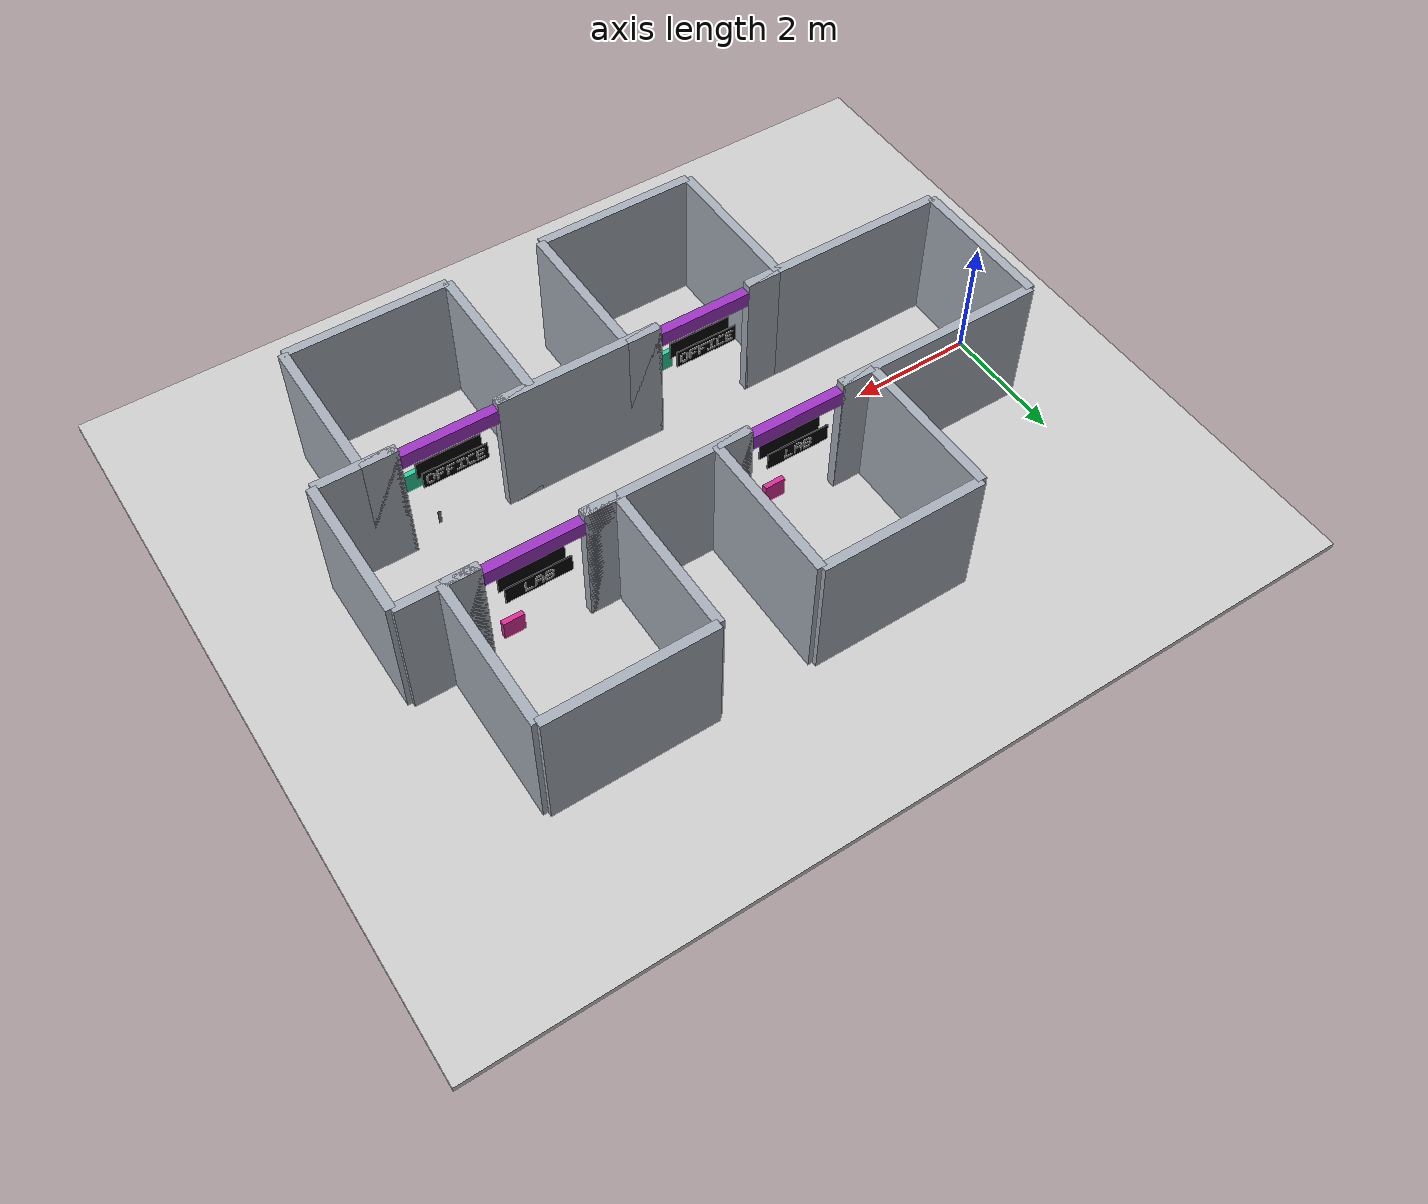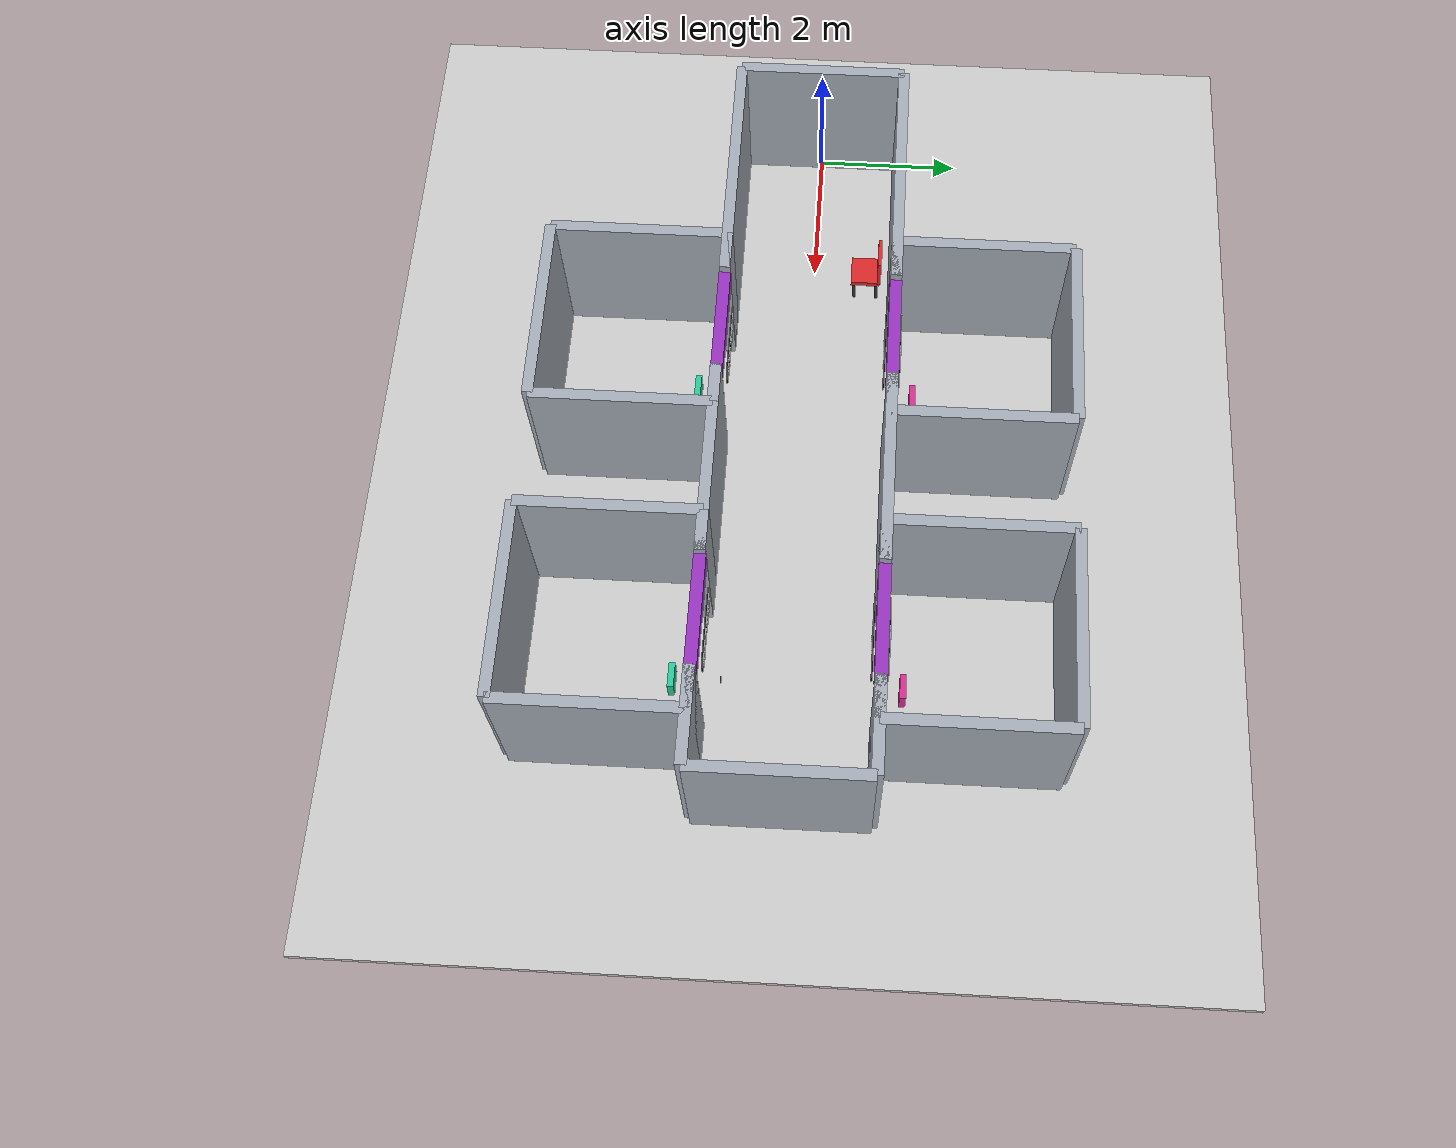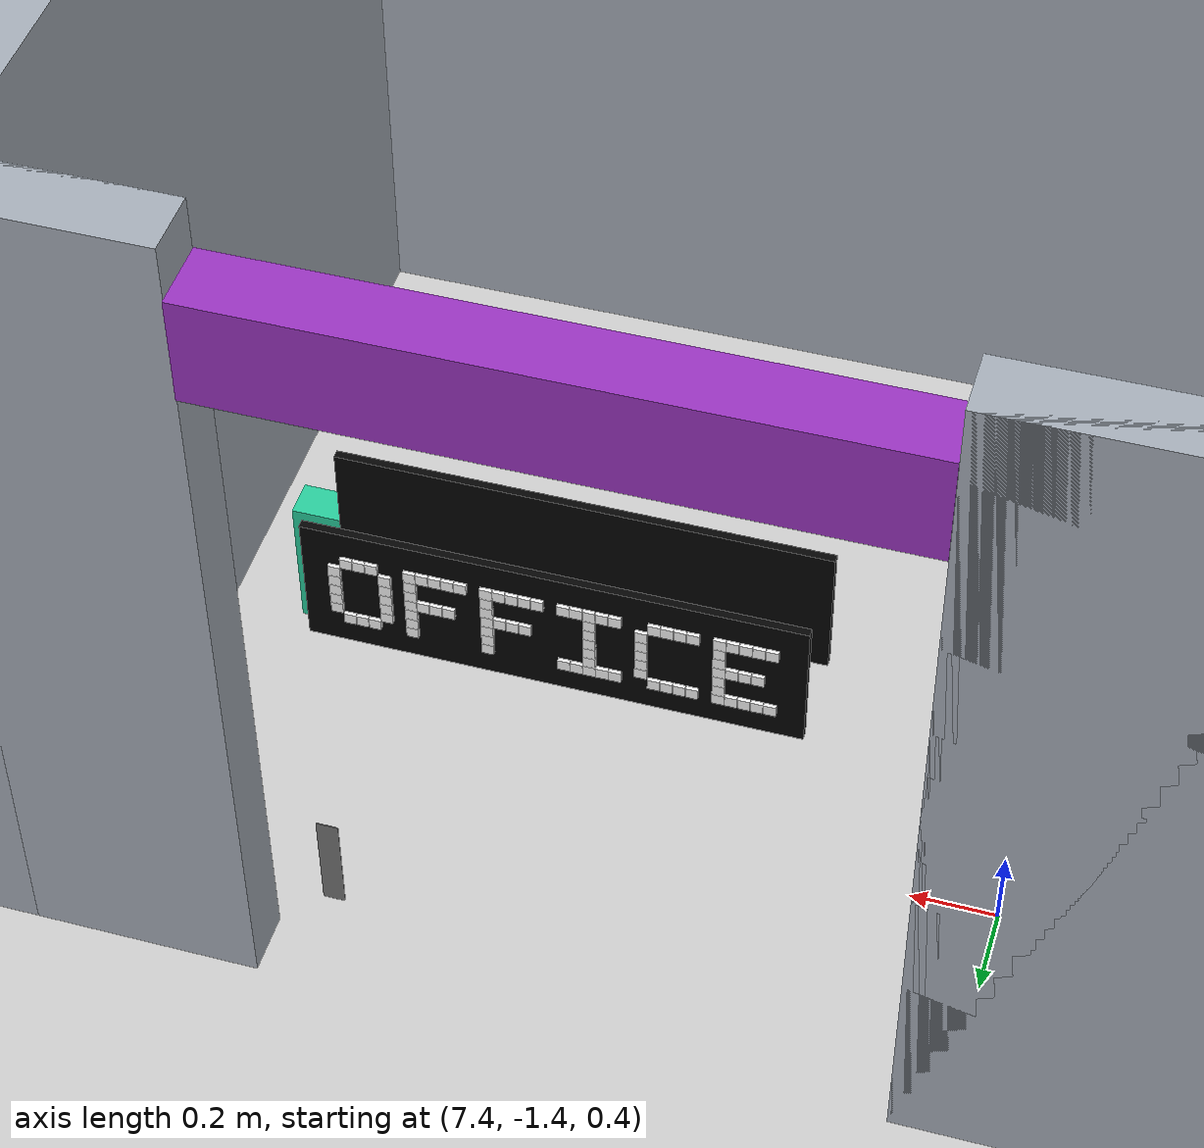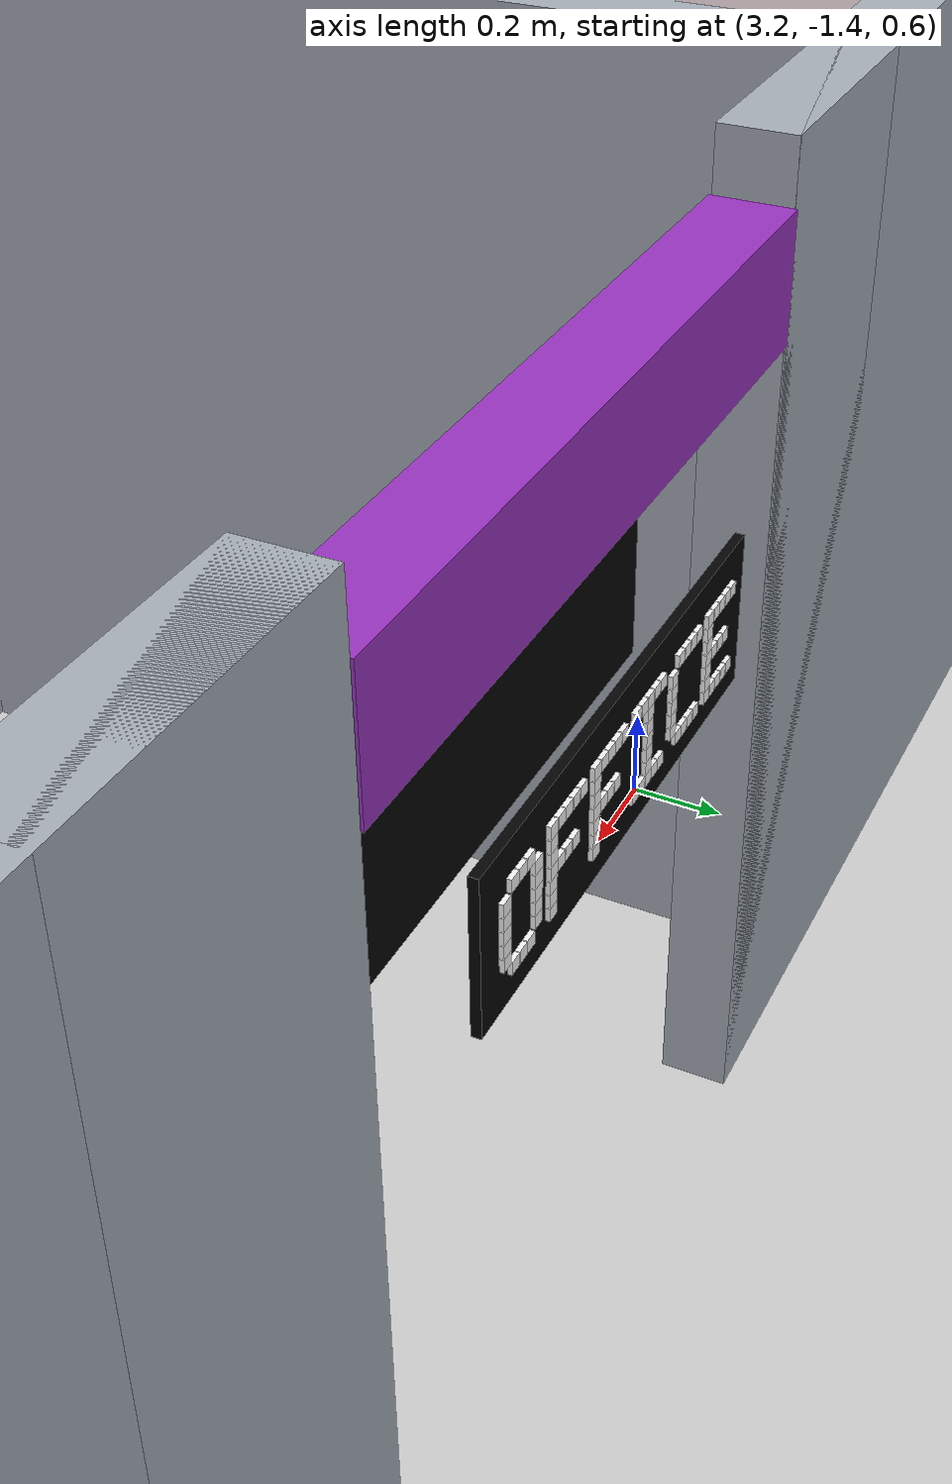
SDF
<?xml version='1.0' encoding='utf-8'?>
<sdf version="1.9">
  <world name="default">
    <plugin filename="gz-sim-physics-system" name="gz::sim::systems::Physics" />
    <plugin filename="gz-sim-user-commands-system" name="gz::sim::systems::UserCommands" />
    <plugin filename="gz-sim-sensors-system" name="gz::sim::systems::Sensors">
      <render_engine>ogre2</render_engine>
    </plugin>
    <plugin filename="gz-sim-imu-system" name="gz::sim::systems::Imu" />
    <plugin filename="gz-sim-contact-system" name="gz::sim::systems::Contact" />
    <physics name="3ms" type="ode">
      <max_step_size>0.003</max_step_size>
      <real_time_factor>1</real_time_factor>
    </physics>
    <light name="sun" type="directional">
      <pose>0 0 10 0 0 0</pose>
      <diffuse>0.9 0.9 0.9 1</diffuse>
      <direction>-0.5 0.1 -0.9</direction>
    </light>
    <model name="ground_plane">
      <static>true</static>
      <pose>5.15 0 -0.05 0 0 0</pose>
      <link name="body">
        <collision name="collision">
          <geometry>
            <box>
              <size>14.3 12 0.1</size>
            </box>
          </geometry>
        </collision>
        <visual name="visual">
          <geometry>
            <box>
              <size>14.3 12 0.1</size>
            </box>
          </geometry>
          <material>
            <ambient>0.8 0.8 0.8 1</ambient>
            <diffuse>0.8 0.8 0.8 1</diffuse>
          </material>
        </visual>
      </link>
    </model>
    <model name="start_wall">
      <static>true</static>
      <pose>0 0 1.1 0 0 0</pose>
      <link name="body">
        <collision name="collision">
          <geometry>
            <box>
              <size>0.15 2.3 2.2</size>
            </box>
          </geometry>
        </collision>
        <visual name="visual">
          <geometry>
            <box>
              <size>0.15 2.3 2.2</size>
            </box>
          </geometry>
          <material>
            <ambient>0.65 0.68 0.72 1</ambient>
            <diffuse>0.65 0.68 0.72 1</diffuse>
          </material>
        </visual>
      </link>
    </model>
    <model name="end_wall">
      <static>true</static>
      <pose>10.3 0 1.1 0 0 0</pose>
      <link name="body">
        <collision name="collision">
          <geometry>
            <box>
              <size>0.15 2.3 2.2</size>
            </box>
          </geometry>
        </collision>
        <visual name="visual">
          <geometry>
            <box>
              <size>0.15 2.3 2.2</size>
            </box>
          </geometry>
          <material>
            <ambient>0.65 0.68 0.72 1</ambient>
            <diffuse>0.65 0.68 0.72 1</diffuse>
          </material>
        </visual>
      </link>
    </model>
    <model name="hall_-1_1">
      <static>true</static>
      <pose>1.7000000000000002 -1.15 1.1 0 0 0</pose>
      <link name="body">
        <collision name="collision">
          <geometry>
            <box>
              <size>3.4000000000000004 0.15 2.2</size>
            </box>
          </geometry>
        </collision>
        <visual name="visual">
          <geometry>
            <box>
              <size>3.4000000000000004 0.15 2.2</size>
            </box>
          </geometry>
          <material>
            <ambient>0.65 0.68 0.72 1</ambient>
            <diffuse>0.65 0.68 0.72 1</diffuse>
          </material>
        </visual>
      </link>
    </model>
    <model name="room_-1_1_-1">
      <static>true</static>
      <pose>2.8500000000000005 -2.3499999999999996 1.1 0 0 0</pose>
      <link name="body">
        <collision name="collision">
          <geometry>
            <box>
              <size>0.15 2.4 2.2</size>
            </box>
          </geometry>
        </collision>
        <visual name="visual">
          <geometry>
            <box>
              <size>0.15 2.4 2.2</size>
            </box>
          </geometry>
          <material>
            <ambient>0.65 0.68 0.72 1</ambient>
            <diffuse>0.65 0.68 0.72 1</diffuse>
          </material>
        </visual>
      </link>
    </model>
    <model name="room_-1_1_1">
      <static>true</static>
      <pose>5.45 -2.3499999999999996 1.1 0 0 0</pose>
      <link name="body">
        <collision name="collision">
          <geometry>
            <box>
              <size>0.15 2.4 2.2</size>
            </box>
          </geometry>
        </collision>
        <visual name="visual">
          <geometry>
            <box>
              <size>0.15 2.4 2.2</size>
            </box>
          </geometry>
          <material>
            <ambient>0.65 0.68 0.72 1</ambient>
            <diffuse>0.65 0.68 0.72 1</diffuse>
          </material>
        </visual>
      </link>
    </model>
    <model name="room_end_-1_1">
      <static>true</static>
      <pose>4.15 -3.55 1.1 0 0 0</pose>
      <link name="body">
        <collision name="collision">
          <geometry>
            <box>
              <size>2.6 0.15 2.2</size>
            </box>
          </geometry>
        </collision>
        <visual name="visual">
          <geometry>
            <box>
              <size>2.6 0.15 2.2</size>
            </box>
          </geometry>
          <material>
            <ambient>0.65 0.68 0.72 1</ambient>
            <diffuse>0.65 0.68 0.72 1</diffuse>
          </material>
        </visual>
      </link>
    </model>
    <model name="jamb_-1_1_-1">
      <static>true</static>
      <pose>3.1250000000000004 -1.15 1.1 0 0 0</pose>
      <link name="body">
        <collision name="collision">
          <geometry>
            <box>
              <size>0.55 0.15 2.2</size>
            </box>
          </geometry>
        </collision>
        <visual name="visual">
          <geometry>
            <box>
              <size>0.55 0.15 2.2</size>
            </box>
          </geometry>
          <material>
            <ambient>0.65 0.68 0.72 1</ambient>
            <diffuse>0.65 0.68 0.72 1</diffuse>
          </material>
        </visual>
      </link>
    </model>
    <model name="jamb_-1_1_1">
      <static>true</static>
      <pose>5.175000000000001 -1.15 1.1 0 0 0</pose>
      <link name="body">
        <collision name="collision">
          <geometry>
            <box>
              <size>0.55 0.15 2.2</size>
            </box>
          </geometry>
        </collision>
        <visual name="visual">
          <geometry>
            <box>
              <size>0.55 0.15 2.2</size>
            </box>
          </geometry>
          <material>
            <ambient>0.65 0.68 0.72 1</ambient>
            <diffuse>0.65 0.68 0.72 1</diffuse>
          </material>
        </visual>
      </link>
    </model>
    <model name="hall_-1_2">
      <static>true</static>
      <pose>6.2250000000000005 -1.15 1.1 0 0 0</pose>
      <link name="body">
        <collision name="collision">
          <geometry>
            <box>
              <size>2.6500000000000004 0.15 2.2</size>
            </box>
          </geometry>
        </collision>
        <visual name="visual">
          <geometry>
            <box>
              <size>2.6500000000000004 0.15 2.2</size>
            </box>
          </geometry>
          <material>
            <ambient>0.65 0.68 0.72 1</ambient>
            <diffuse>0.65 0.68 0.72 1</diffuse>
          </material>
        </visual>
      </link>
    </model>
    <model name="room_-1_2_-1">
      <static>true</static>
      <pose>7.000000000000001 -2.3499999999999996 1.1 0 0 0</pose>
      <link name="body">
        <collision name="collision">
          <geometry>
            <box>
              <size>0.15 2.4 2.2</size>
            </box>
          </geometry>
        </collision>
        <visual name="visual">
          <geometry>
            <box>
              <size>0.15 2.4 2.2</size>
            </box>
          </geometry>
          <material>
            <ambient>0.65 0.68 0.72 1</ambient>
            <diffuse>0.65 0.68 0.72 1</diffuse>
          </material>
        </visual>
      </link>
    </model>
    <model name="room_-1_2_1">
      <static>true</static>
      <pose>9.600000000000001 -2.3499999999999996 1.1 0 0 0</pose>
      <link name="body">
        <collision name="collision">
          <geometry>
            <box>
              <size>0.15 2.4 2.2</size>
            </box>
          </geometry>
        </collision>
        <visual name="visual">
          <geometry>
            <box>
              <size>0.15 2.4 2.2</size>
            </box>
          </geometry>
          <material>
            <ambient>0.65 0.68 0.72 1</ambient>
            <diffuse>0.65 0.68 0.72 1</diffuse>
          </material>
        </visual>
      </link>
    </model>
    <model name="room_end_-1_2">
      <static>true</static>
      <pose>8.3 -3.55 1.1 0 0 0</pose>
      <link name="body">
        <collision name="collision">
          <geometry>
            <box>
              <size>2.6 0.15 2.2</size>
            </box>
          </geometry>
        </collision>
        <visual name="visual">
          <geometry>
            <box>
              <size>2.6 0.15 2.2</size>
            </box>
          </geometry>
          <material>
            <ambient>0.65 0.68 0.72 1</ambient>
            <diffuse>0.65 0.68 0.72 1</diffuse>
          </material>
        </visual>
      </link>
    </model>
    <model name="jamb_-1_2_-1">
      <static>true</static>
      <pose>7.275 -1.15 1.1 0 0 0</pose>
      <link name="body">
        <collision name="collision">
          <geometry>
            <box>
              <size>0.55 0.15 2.2</size>
            </box>
          </geometry>
        </collision>
        <visual name="visual">
          <geometry>
            <box>
              <size>0.55 0.15 2.2</size>
            </box>
          </geometry>
          <material>
            <ambient>0.65 0.68 0.72 1</ambient>
            <diffuse>0.65 0.68 0.72 1</diffuse>
          </material>
        </visual>
      </link>
    </model>
    <model name="jamb_-1_2_1">
      <static>true</static>
      <pose>9.325000000000001 -1.15 1.1 0 0 0</pose>
      <link name="body">
        <collision name="collision">
          <geometry>
            <box>
              <size>0.55 0.15 2.2</size>
            </box>
          </geometry>
        </collision>
        <visual name="visual">
          <geometry>
            <box>
              <size>0.55 0.15 2.2</size>
            </box>
          </geometry>
          <material>
            <ambient>0.65 0.68 0.72 1</ambient>
            <diffuse>0.65 0.68 0.72 1</diffuse>
          </material>
        </visual>
      </link>
    </model>
    <model name="hall_end_-1">
      <static>true</static>
      <pose>9.675 -1.15 1.1 0 0 0</pose>
      <link name="body">
        <collision name="collision">
          <geometry>
            <box>
              <size>1.25 0.15 2.2</size>
            </box>
          </geometry>
        </collision>
        <visual name="visual">
          <geometry>
            <box>
              <size>1.25 0.15 2.2</size>
            </box>
          </geometry>
          <material>
            <ambient>0.65 0.68 0.72 1</ambient>
            <diffuse>0.65 0.68 0.72 1</diffuse>
          </material>
        </visual>
      </link>
    </model>
    <model name="hall_1_1">
      <static>true</static>
      <pose>1.7000000000000002 1.15 1.1 0 0 0</pose>
      <link name="body">
        <collision name="collision">
          <geometry>
            <box>
              <size>3.4000000000000004 0.15 2.2</size>
            </box>
          </geometry>
        </collision>
        <visual name="visual">
          <geometry>
            <box>
              <size>3.4000000000000004 0.15 2.2</size>
            </box>
          </geometry>
          <material>
            <ambient>0.65 0.68 0.72 1</ambient>
            <diffuse>0.65 0.68 0.72 1</diffuse>
          </material>
        </visual>
      </link>
    </model>
    <model name="room_1_1_-1">
      <static>true</static>
      <pose>2.8500000000000005 2.3499999999999996 1.1 0 0 0</pose>
      <link name="body">
        <collision name="collision">
          <geometry>
            <box>
              <size>0.15 2.4 2.2</size>
            </box>
          </geometry>
        </collision>
        <visual name="visual">
          <geometry>
            <box>
              <size>0.15 2.4 2.2</size>
            </box>
          </geometry>
          <material>
            <ambient>0.65 0.68 0.72 1</ambient>
            <diffuse>0.65 0.68 0.72 1</diffuse>
          </material>
        </visual>
      </link>
    </model>
    <model name="room_1_1_1">
      <static>true</static>
      <pose>5.45 2.3499999999999996 1.1 0 0 0</pose>
      <link name="body">
        <collision name="collision">
          <geometry>
            <box>
              <size>0.15 2.4 2.2</size>
            </box>
          </geometry>
        </collision>
        <visual name="visual">
          <geometry>
            <box>
              <size>0.15 2.4 2.2</size>
            </box>
          </geometry>
          <material>
            <ambient>0.65 0.68 0.72 1</ambient>
            <diffuse>0.65 0.68 0.72 1</diffuse>
          </material>
        </visual>
      </link>
    </model>
    <model name="room_end_1_1">
      <static>true</static>
      <pose>4.15 3.55 1.1 0 0 0</pose>
      <link name="body">
        <collision name="collision">
          <geometry>
            <box>
              <size>2.6 0.15 2.2</size>
            </box>
          </geometry>
        </collision>
        <visual name="visual">
          <geometry>
            <box>
              <size>2.6 0.15 2.2</size>
            </box>
          </geometry>
          <material>
            <ambient>0.65 0.68 0.72 1</ambient>
            <diffuse>0.65 0.68 0.72 1</diffuse>
          </material>
        </visual>
      </link>
    </model>
    <model name="jamb_1_1_-1">
      <static>true</static>
      <pose>3.1250000000000004 1.15 1.1 0 0 0</pose>
      <link name="body">
        <collision name="collision">
          <geometry>
            <box>
              <size>0.55 0.15 2.2</size>
            </box>
          </geometry>
        </collision>
        <visual name="visual">
          <geometry>
            <box>
              <size>0.55 0.15 2.2</size>
            </box>
          </geometry>
          <material>
            <ambient>0.65 0.68 0.72 1</ambient>
            <diffuse>0.65 0.68 0.72 1</diffuse>
          </material>
        </visual>
      </link>
    </model>
    <model name="jamb_1_1_1">
      <static>true</static>
      <pose>5.175000000000001 1.15 1.1 0 0 0</pose>
      <link name="body">
        <collision name="collision">
          <geometry>
            <box>
              <size>0.55 0.15 2.2</size>
            </box>
          </geometry>
        </collision>
        <visual name="visual">
          <geometry>
            <box>
              <size>0.55 0.15 2.2</size>
            </box>
          </geometry>
          <material>
            <ambient>0.65 0.68 0.72 1</ambient>
            <diffuse>0.65 0.68 0.72 1</diffuse>
          </material>
        </visual>
      </link>
    </model>
    <model name="hall_1_2">
      <static>true</static>
      <pose>6.2250000000000005 1.15 1.1 0 0 0</pose>
      <link name="body">
        <collision name="collision">
          <geometry>
            <box>
              <size>2.6500000000000004 0.15 2.2</size>
            </box>
          </geometry>
        </collision>
        <visual name="visual">
          <geometry>
            <box>
              <size>2.6500000000000004 0.15 2.2</size>
            </box>
          </geometry>
          <material>
            <ambient>0.65 0.68 0.72 1</ambient>
            <diffuse>0.65 0.68 0.72 1</diffuse>
          </material>
        </visual>
      </link>
    </model>
    <model name="room_1_2_-1">
      <static>true</static>
      <pose>7.000000000000001 2.3499999999999996 1.1 0 0 0</pose>
      <link name="body">
        <collision name="collision">
          <geometry>
            <box>
              <size>0.15 2.4 2.2</size>
            </box>
          </geometry>
        </collision>
        <visual name="visual">
          <geometry>
            <box>
              <size>0.15 2.4 2.2</size>
            </box>
          </geometry>
          <material>
            <ambient>0.65 0.68 0.72 1</ambient>
            <diffuse>0.65 0.68 0.72 1</diffuse>
          </material>
        </visual>
      </link>
    </model>
    <model name="room_1_2_1">
      <static>true</static>
      <pose>9.600000000000001 2.3499999999999996 1.1 0 0 0</pose>
      <link name="body">
        <collision name="collision">
          <geometry>
            <box>
              <size>0.15 2.4 2.2</size>
            </box>
          </geometry>
        </collision>
        <visual name="visual">
          <geometry>
            <box>
              <size>0.15 2.4 2.2</size>
            </box>
          </geometry>
          <material>
            <ambient>0.65 0.68 0.72 1</ambient>
            <diffuse>0.65 0.68 0.72 1</diffuse>
          </material>
        </visual>
      </link>
    </model>
    <model name="room_end_1_2">
      <static>true</static>
      <pose>8.3 3.55 1.1 0 0 0</pose>
      <link name="body">
        <collision name="collision">
          <geometry>
            <box>
              <size>2.6 0.15 2.2</size>
            </box>
          </geometry>
        </collision>
        <visual name="visual">
          <geometry>
            <box>
              <size>2.6 0.15 2.2</size>
            </box>
          </geometry>
          <material>
            <ambient>0.65 0.68 0.72 1</ambient>
            <diffuse>0.65 0.68 0.72 1</diffuse>
          </material>
        </visual>
      </link>
    </model>
    <model name="jamb_1_2_-1">
      <static>true</static>
      <pose>7.275 1.15 1.1 0 0 0</pose>
      <link name="body">
        <collision name="collision">
          <geometry>
            <box>
              <size>0.55 0.15 2.2</size>
            </box>
          </geometry>
        </collision>
        <visual name="visual">
          <geometry>
            <box>
              <size>0.55 0.15 2.2</size>
            </box>
          </geometry>
          <material>
            <ambient>0.65 0.68 0.72 1</ambient>
            <diffuse>0.65 0.68 0.72 1</diffuse>
          </material>
        </visual>
      </link>
    </model>
    <model name="jamb_1_2_1">
      <static>true</static>
      <pose>9.325000000000001 1.15 1.1 0 0 0</pose>
      <link name="body">
        <collision name="collision">
          <geometry>
            <box>
              <size>0.55 0.15 2.2</size>
            </box>
          </geometry>
        </collision>
        <visual name="visual">
          <geometry>
            <box>
              <size>0.55 0.15 2.2</size>
            </box>
          </geometry>
          <material>
            <ambient>0.65 0.68 0.72 1</ambient>
            <diffuse>0.65 0.68 0.72 1</diffuse>
          </material>
        </visual>
      </link>
    </model>
    <model name="hall_end_1">
      <static>true</static>
      <pose>9.675 1.15 1.1 0 0 0</pose>
      <link name="body">
        <collision name="collision">
          <geometry>
            <box>
              <size>1.25 0.15 2.2</size>
            </box>
          </geometry>
        </collision>
        <visual name="visual">
          <geometry>
            <box>
              <size>1.25 0.15 2.2</size>
            </box>
          </geometry>
          <material>
            <ambient>0.65 0.68 0.72 1</ambient>
            <diffuse>0.65 0.68 0.72 1</diffuse>
          </material>
        </visual>
      </link>
    </model>
    <model name="chair_seat">
      <static>true</static>
      <pose>2.2 0.7499999999999999 0.4 0 0 0</pose>
      <link name="body">
        <collision name="collision">
          <geometry>
            <box>
              <size>0.42 0.42 0.08</size>
            </box>
          </geometry>
        </collision>
        <visual name="visual">
          <geometry>
            <box>
              <size>0.42 0.42 0.08</size>
            </box>
          </geometry>
          <material>
            <ambient>0.86 0.16 0.16 1</ambient>
            <diffuse>0.86 0.16 0.16 1</diffuse>
          </material>
        </visual>
      </link>
    </model>
    <model name="chair_back">
      <static>true</static>
      <pose>2.2 0.94 0.67 0 0 0</pose>
      <link name="body">
        <collision name="collision">
          <geometry>
            <box>
              <size>0.42 0.05 0.5</size>
            </box>
          </geometry>
        </collision>
        <visual name="visual">
          <geometry>
            <box>
              <size>0.42 0.05 0.5</size>
            </box>
          </geometry>
          <material>
            <ambient>0.86 0.16 0.16 1</ambient>
            <diffuse>0.86 0.16 0.16 1</diffuse>
          </material>
        </visual>
      </link>
    </model>
    <model name="chair_leg_-0.16_-0.16">
      <static>true</static>
      <pose>2.04 0.5899999999999999 0.19 0 0 0</pose>
      <link name="body">
        <collision name="collision">
          <geometry>
            <box>
              <size>0.04 0.04 0.38</size>
            </box>
          </geometry>
        </collision>
        <visual name="visual">
          <geometry>
            <box>
              <size>0.04 0.04 0.38</size>
            </box>
          </geometry>
          <material>
            <ambient>0.2 0.2 0.2 1</ambient>
            <diffuse>0.2 0.2 0.2 1</diffuse>
          </material>
        </visual>
      </link>
    </model>
    <model name="chair_leg_-0.16_0.16">
      <static>true</static>
      <pose>2.04 0.9099999999999999 0.19 0 0 0</pose>
      <link name="body">
        <collision name="collision">
          <geometry>
            <box>
              <size>0.04 0.04 0.38</size>
            </box>
          </geometry>
        </collision>
        <visual name="visual">
          <geometry>
            <box>
              <size>0.04 0.04 0.38</size>
            </box>
          </geometry>
          <material>
            <ambient>0.2 0.2 0.2 1</ambient>
            <diffuse>0.2 0.2 0.2 1</diffuse>
          </material>
        </visual>
      </link>
    </model>
    <model name="chair_leg_0.16_-0.16">
      <static>true</static>
      <pose>2.3600000000000003 0.5899999999999999 0.19 0 0 0</pose>
      <link name="body">
        <collision name="collision">
          <geometry>
            <box>
              <size>0.04 0.04 0.38</size>
            </box>
          </geometry>
        </collision>
        <visual name="visual">
          <geometry>
            <box>
              <size>0.04 0.04 0.38</size>
            </box>
          </geometry>
          <material>
            <ambient>0.2 0.2 0.2 1</ambient>
            <diffuse>0.2 0.2 0.2 1</diffuse>
          </material>
        </visual>
      </link>
    </model>
    <model name="chair_leg_0.16_0.16">
      <static>true</static>
      <pose>2.3600000000000003 0.9099999999999999 0.19 0 0 0</pose>
      <link name="body">
        <collision name="collision">
          <geometry>
            <box>
              <size>0.04 0.04 0.38</size>
            </box>
          </geometry>
        </collision>
        <visual name="visual">
          <geometry>
            <box>
              <size>0.04 0.04 0.38</size>
            </box>
          </geometry>
          <material>
            <ambient>0.2 0.2 0.2 1</ambient>
            <diffuse>0.2 0.2 0.2 1</diffuse>
          </material>
        </visual>
      </link>
    </model>
    <model name="r3geo_base_r009_right_1_lintel">
      <static>true</static>
      <pose>4.15 -1.15 1.95 0 0 0</pose>
      <link name="body">
        <collision name="collision">
          <geometry>
            <box>
              <size>1.5 0.16 0.25</size>
            </box>
          </geometry>
        </collision>
        <visual name="visual">
          <geometry>
            <box>
              <size>1.5 0.16 0.25</size>
            </box>
          </geometry>
          <material>
            <ambient>0.6 0.2 0.75 1</ambient>
            <diffuse>0.6 0.2 0.75 1</diffuse>
          </material>
        </visual>
      </link>
    </model>
    <model name="r3geo_base_r009_right_1_entrance_sign">
      <static>true</static>
      <pose>4.680000000000001 -1.45 1.05 0 0 0</pose>
      <link name="body">
        <visual name="visual">
          <geometry>
            <box>
              <size>0.32 0.08 0.32</size>
            </box>
          </geometry>
          <material>
            <ambient>0.16 0.8 0.61 1</ambient>
            <diffuse>0.16 0.8 0.61 1</diffuse>
          </material>
        </visual>
      </link>
    </model>
    <model name="r3geo_base_r009_right_2_lintel">
      <static>true</static>
      <pose>8.3 -1.15 1.95 0 0 0</pose>
      <link name="body">
        <collision name="collision">
          <geometry>
            <box>
              <size>1.5 0.16 0.25</size>
            </box>
          </geometry>
        </collision>
        <visual name="visual">
          <geometry>
            <box>
              <size>1.5 0.16 0.25</size>
            </box>
          </geometry>
          <material>
            <ambient>0.6 0.2 0.75 1</ambient>
            <diffuse>0.6 0.2 0.75 1</diffuse>
          </material>
        </visual>
      </link>
    </model>
    <model name="r3geo_base_r009_right_2_entrance_sign">
      <static>true</static>
      <pose>8.83 -1.45 1.05 0 0 0</pose>
      <link name="body">
        <visual name="visual">
          <geometry>
            <box>
              <size>0.32 0.08 0.32</size>
            </box>
          </geometry>
          <material>
            <ambient>0.16 0.8 0.61 1</ambient>
            <diffuse>0.16 0.8 0.61 1</diffuse>
          </material>
        </visual>
      </link>
    </model>
    <model name="r3geo_base_r009_left_1_lintel">
      <static>true</static>
      <pose>4.15 1.15 1.95 0 0 0</pose>
      <link name="body">
        <collision name="collision">
          <geometry>
            <box>
              <size>1.5 0.16 0.25</size>
            </box>
          </geometry>
        </collision>
        <visual name="visual">
          <geometry>
            <box>
              <size>1.5 0.16 0.25</size>
            </box>
          </geometry>
          <material>
            <ambient>0.6 0.2 0.75 1</ambient>
            <diffuse>0.6 0.2 0.75 1</diffuse>
          </material>
        </visual>
      </link>
    </model>
    <model name="r3geo_base_r009_left_1_entrance_sign">
      <static>true</static>
      <pose>4.680000000000001 1.45 1.05 0 0 0</pose>
      <link name="body">
        <visual name="visual">
          <geometry>
            <box>
              <size>0.32 0.08 0.32</size>
            </box>
          </geometry>
          <material>
            <ambient>0.84 0.18 0.57 1</ambient>
            <diffuse>0.84 0.18 0.57 1</diffuse>
          </material>
        </visual>
      </link>
    </model>
    <model name="r3geo_base_r009_left_2_lintel">
      <static>true</static>
      <pose>8.3 1.15 1.95 0 0 0</pose>
      <link name="body">
        <collision name="collision">
          <geometry>
            <box>
              <size>1.5 0.16 0.25</size>
            </box>
          </geometry>
        </collision>
        <visual name="visual">
          <geometry>
            <box>
              <size>1.5 0.16 0.25</size>
            </box>
          </geometry>
          <material>
            <ambient>0.6 0.2 0.75 1</ambient>
            <diffuse>0.6 0.2 0.75 1</diffuse>
          </material>
        </visual>
      </link>
    </model>
    <model name="r3geo_base_r009_left_2_entrance_sign">
      <static>true</static>
      <pose>8.83 1.45 1.05 0 0 0</pose>
      <link name="body">
        <visual name="visual">
          <geometry>
            <box>
              <size>0.32 0.08 0.32</size>
            </box>
          </geometry>
          <material>
            <ambient>0.84 0.18 0.57 1</ambient>
            <diffuse>0.84 0.18 0.57 1</diffuse>
          </material>
        </visual>
      </link>
    </model>
    <model name="readable_r3geo_base_r009_right_1_entrance_corridor">
      <static>true</static>
      <pose>4.15 -1.05 1.43 0 0 3.14159265359</pose>
      <link name="lettering">
        <visual name="backboard">
          <pose>0 0 0 0 0 0</pose>
          <geometry>
            <box>
              <size>1.02 0.018 0.3</size>
            </box>
          </geometry>
          <material>
            <ambient>.015 .015 .015 1</ambient>
            <diffuse>.015 .015 .015 1</diffuse>
            <emissive>.015 .015 .015 1</emissive>
          </material>
          <cast_shadows>false</cast_shadows>
        </visual>
        <visual name="letter_0_0_1">
          <pose>-0.416 -0.014 0.078 0 0 0</pose>
          <geometry>
            <box>
              <size>0.024439999999999996 0.008 0.024439999999999996</size>
            </box>
          </geometry>
          <material>
            <ambient>.96 .96 .96 1</ambient>
            <diffuse>.96 .96 .96 1</diffuse>
            <emissive>.96 .96 .96 1</emissive>
          </material>
          <cast_shadows>false</cast_shadows>
        </visual>
        <visual name="letter_0_0_2">
          <pose>-0.39 -0.014 0.078 0 0 0</pose>
          <geometry>
            <box>
              <size>0.024439999999999996 0.008 0.024439999999999996</size>
            </box>
          </geometry>
          <material>
            <ambient>.96 .96 .96 1</ambient>
            <diffuse>.96 .96 .96 1</diffuse>
            <emissive>.96 .96 .96 1</emissive>
          </material>
          <cast_shadows>false</cast_shadows>
        </visual>
        <visual name="letter_0_0_3">
          <pose>-0.364 -0.014 0.078 0 0 0</pose>
          <geometry>
            <box>
              <size>0.024439999999999996 0.008 0.024439999999999996</size>
            </box>
          </geometry>
          <material>
            <ambient>.96 .96 .96 1</ambient>
            <diffuse>.96 .96 .96 1</diffuse>
            <emissive>.96 .96 .96 1</emissive>
          </material>
          <cast_shadows>false</cast_shadows>
        </visual>
        <visual name="letter_0_1_0">
          <pose>-0.442 -0.014 0.052 0 0 0</pose>
          <geometry>
            <box>
              <size>0.024439999999999996 0.008 0.024439999999999996</size>
            </box>
          </geometry>
          <material>
            <ambient>.96 .96 .96 1</ambient>
            <diffuse>.96 .96 .96 1</diffuse>
            <emissive>.96 .96 .96 1</emissive>
          </material>
          <cast_shadows>false</cast_shadows>
        </visual>
        <visual name="letter_0_1_4">
          <pose>-0.338 -0.014 0.052 0 0 0</pose>
          <geometry>
            <box>
              <size>0.024439999999999996 0.008 0.024439999999999996</size>
            </box>
          </geometry>
          <material>
            <ambient>.96 .96 .96 1</ambient>
            <diffuse>.96 .96 .96 1</diffuse>
            <emissive>.96 .96 .96 1</emissive>
          </material>
          <cast_shadows>false</cast_shadows>
        </visual>
        <visual name="letter_0_2_0">
          <pose>-0.442 -0.014 0.026 0 0 0</pose>
          <geometry>
            <box>
              <size>0.024439999999999996 0.008 0.024439999999999996</size>
            </box>
          </geometry>
          <material>
            <ambient>.96 .96 .96 1</ambient>
            <diffuse>.96 .96 .96 1</diffuse>
            <emissive>.96 .96 .96 1</emissive>
          </material>
          <cast_shadows>false</cast_shadows>
        </visual>
        <visual name="letter_0_2_4">
          <pose>-0.338 -0.014 0.026 0 0 0</pose>
          <geometry>
            <box>
              <size>0.024439999999999996 0.008 0.024439999999999996</size>
            </box>
          </geometry>
          <material>
            <ambient>.96 .96 .96 1</ambient>
            <diffuse>.96 .96 .96 1</diffuse>
            <emissive>.96 .96 .96 1</emissive>
          </material>
          <cast_shadows>false</cast_shadows>
        </visual>
        <visual name="letter_0_3_0">
          <pose>-0.442 -0.014 0 0 0 0</pose>
          <geometry>
            <box>
              <size>0.024439999999999996 0.008 0.024439999999999996</size>
            </box>
          </geometry>
          <material>
            <ambient>.96 .96 .96 1</ambient>
            <diffuse>.96 .96 .96 1</diffuse>
            <emissive>.96 .96 .96 1</emissive>
          </material>
          <cast_shadows>false</cast_shadows>
        </visual>
        <visual name="letter_0_3_4">
          <pose>-0.338 -0.014 0 0 0 0</pose>
          <geometry>
            <box>
              <size>0.024439999999999996 0.008 0.024439999999999996</size>
            </box>
          </geometry>
          <material>
            <ambient>.96 .96 .96 1</ambient>
            <diffuse>.96 .96 .96 1</diffuse>
            <emissive>.96 .96 .96 1</emissive>
          </material>
          <cast_shadows>false</cast_shadows>
        </visual>
        <visual name="letter_0_4_0">
          <pose>-0.442 -0.014 -0.026 0 0 0</pose>
          <geometry>
            <box>
              <size>0.024439999999999996 0.008 0.024439999999999996</size>
            </box>
          </geometry>
          <material>
            <ambient>.96 .96 .96 1</ambient>
            <diffuse>.96 .96 .96 1</diffuse>
            <emissive>.96 .96 .96 1</emissive>
          </material>
          <cast_shadows>false</cast_shadows>
        </visual>
        <visual name="letter_0_4_4">
          <pose>-0.338 -0.014 -0.026 0 0 0</pose>
          <geometry>
            <box>
              <size>0.024439999999999996 0.008 0.024439999999999996</size>
            </box>
          </geometry>
          <material>
            <ambient>.96 .96 .96 1</ambient>
            <diffuse>.96 .96 .96 1</diffuse>
            <emissive>.96 .96 .96 1</emissive>
          </material>
          <cast_shadows>false</cast_shadows>
        </visual>
        <visual name="letter_0_5_0">
          <pose>-0.442 -0.014 -0.052 0 0 0</pose>
          <geometry>
            <box>
              <size>0.024439999999999996 0.008 0.024439999999999996</size>
            </box>
          </geometry>
          <material>
            <ambient>.96 .96 .96 1</ambient>
            <diffuse>.96 .96 .96 1</diffuse>
            <emissive>.96 .96 .96 1</emissive>
          </material>
          <cast_shadows>false</cast_shadows>
        </visual>
        <visual name="letter_0_5_4">
          <pose>-0.338 -0.014 -0.052 0 0 0</pose>
          <geometry>
            <box>
              <size>0.024439999999999996 0.008 0.024439999999999996</size>
            </box>
          </geometry>
          <material>
            <ambient>.96 .96 .96 1</ambient>
            <diffuse>.96 .96 .96 1</diffuse>
            <emissive>.96 .96 .96 1</emissive>
          </material>
          <cast_shadows>false</cast_shadows>
        </visual>
        <visual name="letter_0_6_1">
          <pose>-0.416 -0.014 -0.078 0 0 0</pose>
          <geometry>
            <box>
              <size>0.024439999999999996 0.008 0.024439999999999996</size>
            </box>
          </geometry>
          <material>
            <ambient>.96 .96 .96 1</ambient>
            <diffuse>.96 .96 .96 1</diffuse>
            <emissive>.96 .96 .96 1</emissive>
          </material>
          <cast_shadows>false</cast_shadows>
        </visual>
        <visual name="letter_0_6_2">
          <pose>-0.39 -0.014 -0.078 0 0 0</pose>
          <geometry>
            <box>
              <size>0.024439999999999996 0.008 0.024439999999999996</size>
            </box>
          </geometry>
          <material>
            <ambient>.96 .96 .96 1</ambient>
            <diffuse>.96 .96 .96 1</diffuse>
            <emissive>.96 .96 .96 1</emissive>
          </material>
          <cast_shadows>false</cast_shadows>
        </visual>
        <visual name="letter_0_6_3">
          <pose>-0.364 -0.014 -0.078 0 0 0</pose>
          <geometry>
            <box>
              <size>0.024439999999999996 0.008 0.024439999999999996</size>
            </box>
          </geometry>
          <material>
            <ambient>.96 .96 .96 1</ambient>
            <diffuse>.96 .96 .96 1</diffuse>
            <emissive>.96 .96 .96 1</emissive>
          </material>
          <cast_shadows>false</cast_shadows>
        </visual>
        <visual name="letter_1_0_0">
          <pose>-0.286 -0.014 0.078 0 0 0</pose>
          <geometry>
            <box>
              <size>0.024439999999999996 0.008 0.024439999999999996</size>
            </box>
          </geometry>
          <material>
            <ambient>.96 .96 .96 1</ambient>
            <diffuse>.96 .96 .96 1</diffuse>
            <emissive>.96 .96 .96 1</emissive>
          </material>
          <cast_shadows>false</cast_shadows>
        </visual>
        <visual name="letter_1_0_1">
          <pose>-0.26 -0.014 0.078 0 0 0</pose>
          <geometry>
            <box>
              <size>0.024439999999999996 0.008 0.024439999999999996</size>
            </box>
          </geometry>
          <material>
            <ambient>.96 .96 .96 1</ambient>
            <diffuse>.96 .96 .96 1</diffuse>
            <emissive>.96 .96 .96 1</emissive>
          </material>
          <cast_shadows>false</cast_shadows>
        </visual>
        <visual name="letter_1_0_2">
          <pose>-0.234 -0.014 0.078 0 0 0</pose>
          <geometry>
            <box>
              <size>0.024439999999999996 0.008 0.024439999999999996</size>
            </box>
          </geometry>
          <material>
            <ambient>.96 .96 .96 1</ambient>
            <diffuse>.96 .96 .96 1</diffuse>
            <emissive>.96 .96 .96 1</emissive>
          </material>
          <cast_shadows>false</cast_shadows>
        </visual>
        <visual name="letter_1_0_3">
          <pose>-0.208 -0.014 0.078 0 0 0</pose>
          <geometry>
            <box>
              <size>0.024439999999999996 0.008 0.024439999999999996</size>
            </box>
          </geometry>
          <material>
            <ambient>.96 .96 .96 1</ambient>
            <diffuse>.96 .96 .96 1</diffuse>
            <emissive>.96 .96 .96 1</emissive>
          </material>
          <cast_shadows>false</cast_shadows>
        </visual>
        <visual name="letter_1_0_4">
          <pose>-0.182 -0.014 0.078 0 0 0</pose>
          <geometry>
            <box>
              <size>0.024439999999999996 0.008 0.024439999999999996</size>
            </box>
          </geometry>
          <material>
            <ambient>.96 .96 .96 1</ambient>
            <diffuse>.96 .96 .96 1</diffuse>
            <emissive>.96 .96 .96 1</emissive>
          </material>
          <cast_shadows>false</cast_shadows>
        </visual>
        <visual name="letter_1_1_0">
          <pose>-0.286 -0.014 0.052 0 0 0</pose>
          <geometry>
            <box>
              <size>0.024439999999999996 0.008 0.024439999999999996</size>
            </box>
          </geometry>
          <material>
            <ambient>.96 .96 .96 1</ambient>
            <diffuse>.96 .96 .96 1</diffuse>
            <emissive>.96 .96 .96 1</emissive>
          </material>
          <cast_shadows>false</cast_shadows>
        </visual>
        <visual name="letter_1_2_0">
          <pose>-0.286 -0.014 0.026 0 0 0</pose>
          <geometry>
            <box>
              <size>0.024439999999999996 0.008 0.024439999999999996</size>
            </box>
          </geometry>
          <material>
            <ambient>.96 .96 .96 1</ambient>
            <diffuse>.96 .96 .96 1</diffuse>
            <emissive>.96 .96 .96 1</emissive>
          </material>
          <cast_shadows>false</cast_shadows>
        </visual>
        <visual name="letter_1_3_0">
          <pose>-0.286 -0.014 0 0 0 0</pose>
          <geometry>
            <box>
              <size>0.024439999999999996 0.008 0.024439999999999996</size>
            </box>
          </geometry>
          <material>
            <ambient>.96 .96 .96 1</ambient>
            <diffuse>.96 .96 .96 1</diffuse>
            <emissive>.96 .96 .96 1</emissive>
          </material>
          <cast_shadows>false</cast_shadows>
        </visual>
        <visual name="letter_1_3_1">
          <pose>-0.26 -0.014 0 0 0 0</pose>
          <geometry>
            <box>
              <size>0.024439999999999996 0.008 0.024439999999999996</size>
            </box>
          </geometry>
          <material>
            <ambient>.96 .96 .96 1</ambient>
            <diffuse>.96 .96 .96 1</diffuse>
            <emissive>.96 .96 .96 1</emissive>
          </material>
          <cast_shadows>false</cast_shadows>
        </visual>
        <visual name="letter_1_3_2">
          <pose>-0.234 -0.014 0 0 0 0</pose>
          <geometry>
            <box>
              <size>0.024439999999999996 0.008 0.024439999999999996</size>
            </box>
          </geometry>
          <material>
            <ambient>.96 .96 .96 1</ambient>
            <diffuse>.96 .96 .96 1</diffuse>
            <emissive>.96 .96 .96 1</emissive>
          </material>
          <cast_shadows>false</cast_shadows>
        </visual>
        <visual name="letter_1_3_3">
          <pose>-0.208 -0.014 0 0 0 0</pose>
          <geometry>
            <box>
              <size>0.024439999999999996 0.008 0.024439999999999996</size>
            </box>
          </geometry>
          <material>
            <ambient>.96 .96 .96 1</ambient>
            <diffuse>.96 .96 .96 1</diffuse>
            <emissive>.96 .96 .96 1</emissive>
          </material>
          <cast_shadows>false</cast_shadows>
        </visual>
        <visual name="letter_1_4_0">
          <pose>-0.286 -0.014 -0.026 0 0 0</pose>
          <geometry>
            <box>
              <size>0.024439999999999996 0.008 0.024439999999999996</size>
            </box>
          </geometry>
          <material>
            <ambient>.96 .96 .96 1</ambient>
            <diffuse>.96 .96 .96 1</diffuse>
            <emissive>.96 .96 .96 1</emissive>
          </material>
          <cast_shadows>false</cast_shadows>
        </visual>
        <visual name="letter_1_5_0">
          <pose>-0.286 -0.014 -0.052 0 0 0</pose>
          <geometry>
            <box>
              <size>0.024439999999999996 0.008 0.024439999999999996</size>
            </box>
          </geometry>
          <material>
            <ambient>.96 .96 .96 1</ambient>
            <diffuse>.96 .96 .96 1</diffuse>
            <emissive>.96 .96 .96 1</emissive>
          </material>
          <cast_shadows>false</cast_shadows>
        </visual>
        <visual name="letter_1_6_0">
          <pose>-0.286 -0.014 -0.078 0 0 0</pose>
          <geometry>
            <box>
              <size>0.024439999999999996 0.008 0.024439999999999996</size>
            </box>
          </geometry>
          <material>
            <ambient>.96 .96 .96 1</ambient>
            <diffuse>.96 .96 .96 1</diffuse>
            <emissive>.96 .96 .96 1</emissive>
          </material>
          <cast_shadows>false</cast_shadows>
        </visual>
        <visual name="letter_2_0_0">
          <pose>-0.13 -0.014 0.078 0 0 0</pose>
          <geometry>
            <box>
              <size>0.024439999999999996 0.008 0.024439999999999996</size>
            </box>
          </geometry>
          <material>
            <ambient>.96 .96 .96 1</ambient>
            <diffuse>.96 .96 .96 1</diffuse>
            <emissive>.96 .96 .96 1</emissive>
          </material>
          <cast_shadows>false</cast_shadows>
        </visual>
        <visual name="letter_2_0_1">
          <pose>-0.104 -0.014 0.078 0 0 0</pose>
          <geometry>
            <box>
              <size>0.024439999999999996 0.008 0.024439999999999996</size>
            </box>
          </geometry>
          <material>
            <ambient>.96 .96 .96 1</ambient>
            <diffuse>.96 .96 .96 1</diffuse>
            <emissive>.96 .96 .96 1</emissive>
          </material>
          <cast_shadows>false</cast_shadows>
        </visual>
        <visual name="letter_2_0_2">
          <pose>-0.078 -0.014 0.078 0 0 0</pose>
          <geometry>
            <box>
              <size>0.024439999999999996 0.008 0.024439999999999996</size>
            </box>
          </geometry>
          <material>
            <ambient>.96 .96 .96 1</ambient>
            <diffuse>.96 .96 .96 1</diffuse>
            <emissive>.96 .96 .96 1</emissive>
          </material>
          <cast_shadows>false</cast_shadows>
        </visual>
        <visual name="letter_2_0_3">
          <pose>-0.052 -0.014 0.078 0 0 0</pose>
          <geometry>
            <box>
              <size>0.024439999999999996 0.008 0.024439999999999996</size>
            </box>
          </geometry>
          <material>
            <ambient>.96 .96 .96 1</ambient>
            <diffuse>.96 .96 .96 1</diffuse>
            <emissive>.96 .96 .96 1</emissive>
          </material>
          <cast_shadows>false</cast_shadows>
        </visual>
        <visual name="letter_2_0_4">
          <pose>-0.026 -0.014 0.078 0 0 0</pose>
          <geometry>
            <box>
              <size>0.024439999999999996 0.008 0.024439999999999996</size>
            </box>
          </geometry>
          <material>
            <ambient>.96 .96 .96 1</ambient>
            <diffuse>.96 .96 .96 1</diffuse>
            <emissive>.96 .96 .96 1</emissive>
          </material>
          <cast_shadows>false</cast_shadows>
        </visual>
        <visual name="letter_2_1_0">
          <pose>-0.13 -0.014 0.052 0 0 0</pose>
          <geometry>
            <box>
              <size>0.024439999999999996 0.008 0.024439999999999996</size>
            </box>
          </geometry>
          <material>
            <ambient>.96 .96 .96 1</ambient>
            <diffuse>.96 .96 .96 1</diffuse>
            <emissive>.96 .96 .96 1</emissive>
          </material>
          <cast_shadows>false</cast_shadows>
        </visual>
        <visual name="letter_2_2_0">
          <pose>-0.13 -0.014 0.026 0 0 0</pose>
          <geometry>
            <box>
              <size>0.024439999999999996 0.008 0.024439999999999996</size>
            </box>
          </geometry>
          <material>
            <ambient>.96 .96 .96 1</ambient>
            <diffuse>.96 .96 .96 1</diffuse>
            <emissive>.96 .96 .96 1</emissive>
          </material>
          <cast_shadows>false</cast_shadows>
        </visual>
        <visual name="letter_2_3_0">
          <pose>-0.13 -0.014 0 0 0 0</pose>
          <geometry>
            <box>
              <size>0.024439999999999996 0.008 0.024439999999999996</size>
            </box>
          </geometry>
          <material>
            <ambient>.96 .96 .96 1</ambient>
            <diffuse>.96 .96 .96 1</diffuse>
            <emissive>.96 .96 .96 1</emissive>
          </material>
          <cast_shadows>false</cast_shadows>
        </visual>
        <visual name="letter_2_3_1">
          <pose>-0.104 -0.014 0 0 0 0</pose>
          <geometry>
            <box>
              <size>0.024439999999999996 0.008 0.024439999999999996</size>
            </box>
          </geometry>
          <material>
            <ambient>.96 .96 .96 1</ambient>
            <diffuse>.96 .96 .96 1</diffuse>
            <emissive>.96 .96 .96 1</emissive>
          </material>
          <cast_shadows>false</cast_shadows>
        </visual>
        <visual name="letter_2_3_2">
          <pose>-0.078 -0.014 0 0 0 0</pose>
          <geometry>
            <box>
              <size>0.024439999999999996 0.008 0.024439999999999996</size>
            </box>
          </geometry>
          <material>
            <ambient>.96 .96 .96 1</ambient>
            <diffuse>.96 .96 .96 1</diffuse>
            <emissive>.96 .96 .96 1</emissive>
          </material>
          <cast_shadows>false</cast_shadows>
        </visual>
        <visual name="letter_2_3_3">
          <pose>-0.052 -0.014 0 0 0 0</pose>
          <geometry>
            <box>
              <size>0.024439999999999996 0.008 0.024439999999999996</size>
            </box>
          </geometry>
          <material>
            <ambient>.96 .96 .96 1</ambient>
            <diffuse>.96 .96 .96 1</diffuse>
            <emissive>.96 .96 .96 1</emissive>
          </material>
          <cast_shadows>false</cast_shadows>
        </visual>
        <visual name="letter_2_4_0">
          <pose>-0.13 -0.014 -0.026 0 0 0</pose>
          <geometry>
            <box>
              <size>0.024439999999999996 0.008 0.024439999999999996</size>
            </box>
          </geometry>
          <material>
            <ambient>.96 .96 .96 1</ambient>
            <diffuse>.96 .96 .96 1</diffuse>
            <emissive>.96 .96 .96 1</emissive>
          </material>
          <cast_shadows>false</cast_shadows>
        </visual>
        <visual name="letter_2_5_0">
          <pose>-0.13 -0.014 -0.052 0 0 0</pose>
          <geometry>
            <box>
              <size>0.024439999999999996 0.008 0.024439999999999996</size>
            </box>
          </geometry>
          <material>
            <ambient>.96 .96 .96 1</ambient>
            <diffuse>.96 .96 .96 1</diffuse>
            <emissive>.96 .96 .96 1</emissive>
          </material>
          <cast_shadows>false</cast_shadows>
        </visual>
        <visual name="letter_2_6_0">
          <pose>-0.13 -0.014 -0.078 0 0 0</pose>
          <geometry>
            <box>
              <size>0.024439999999999996 0.008 0.024439999999999996</size>
            </box>
          </geometry>
          <material>
            <ambient>.96 .96 .96 1</ambient>
            <diffuse>.96 .96 .96 1</diffuse>
            <emissive>.96 .96 .96 1</emissive>
          </material>
          <cast_shadows>false</cast_shadows>
        </visual>
        <visual name="letter_3_0_0">
          <pose>0.026 -0.014 0.078 0 0 0</pose>
          <geometry>
            <box>
              <size>0.024439999999999996 0.008 0.024439999999999996</size>
            </box>
          </geometry>
          <material>
            <ambient>.96 .96 .96 1</ambient>
            <diffuse>.96 .96 .96 1</diffuse>
            <emissive>.96 .96 .96 1</emissive>
          </material>
          <cast_shadows>false</cast_shadows>
        </visual>
        <visual name="letter_3_0_1">
          <pose>0.052 -0.014 0.078 0 0 0</pose>
          <geometry>
            <box>
              <size>0.024439999999999996 0.008 0.024439999999999996</size>
            </box>
          </geometry>
          <material>
            <ambient>.96 .96 .96 1</ambient>
            <diffuse>.96 .96 .96 1</diffuse>
            <emissive>.96 .96 .96 1</emissive>
          </material>
          <cast_shadows>false</cast_shadows>
        </visual>
        <visual name="letter_3_0_2">
          <pose>0.078 -0.014 0.078 0 0 0</pose>
          <geometry>
            <box>
              <size>0.024439999999999996 0.008 0.024439999999999996</size>
            </box>
          </geometry>
          <material>
            <ambient>.96 .96 .96 1</ambient>
            <diffuse>.96 .96 .96 1</diffuse>
            <emissive>.96 .96 .96 1</emissive>
          </material>
          <cast_shadows>false</cast_shadows>
        </visual>
        <visual name="letter_3_0_3">
          <pose>0.104 -0.014 0.078 0 0 0</pose>
          <geometry>
            <box>
              <size>0.024439999999999996 0.008 0.024439999999999996</size>
            </box>
          </geometry>
          <material>
            <ambient>.96 .96 .96 1</ambient>
            <diffuse>.96 .96 .96 1</diffuse>
            <emissive>.96 .96 .96 1</emissive>
          </material>
          <cast_shadows>false</cast_shadows>
        </visual>
        <visual name="letter_3_0_4">
          <pose>0.13 -0.014 0.078 0 0 0</pose>
          <geometry>
            <box>
              <size>0.024439999999999996 0.008 0.024439999999999996</size>
            </box>
          </geometry>
          <material>
            <ambient>.96 .96 .96 1</ambient>
            <diffuse>.96 .96 .96 1</diffuse>
            <emissive>.96 .96 .96 1</emissive>
          </material>
          <cast_shadows>false</cast_shadows>
        </visual>
        <visual name="letter_3_1_2">
          <pose>0.078 -0.014 0.052 0 0 0</pose>
          <geometry>
            <box>
              <size>0.024439999999999996 0.008 0.024439999999999996</size>
            </box>
          </geometry>
          <material>
            <ambient>.96 .96 .96 1</ambient>
            <diffuse>.96 .96 .96 1</diffuse>
            <emissive>.96 .96 .96 1</emissive>
          </material>
          <cast_shadows>false</cast_shadows>
        </visual>
        <visual name="letter_3_2_2">
          <pose>0.078 -0.014 0.026 0 0 0</pose>
          <geometry>
            <box>
              <size>0.024439999999999996 0.008 0.024439999999999996</size>
            </box>
          </geometry>
          <material>
            <ambient>.96 .96 .96 1</ambient>
            <diffuse>.96 .96 .96 1</diffuse>
            <emissive>.96 .96 .96 1</emissive>
          </material>
          <cast_shadows>false</cast_shadows>
        </visual>
        <visual name="letter_3_3_2">
          <pose>0.078 -0.014 0 0 0 0</pose>
          <geometry>
            <box>
              <size>0.024439999999999996 0.008 0.024439999999999996</size>
            </box>
          </geometry>
          <material>
            <ambient>.96 .96 .96 1</ambient>
            <diffuse>.96 .96 .96 1</diffuse>
            <emissive>.96 .96 .96 1</emissive>
          </material>
          <cast_shadows>false</cast_shadows>
        </visual>
        <visual name="letter_3_4_2">
          <pose>0.078 -0.014 -0.026 0 0 0</pose>
          <geometry>
            <box>
              <size>0.024439999999999996 0.008 0.024439999999999996</size>
            </box>
          </geometry>
          <material>
            <ambient>.96 .96 .96 1</ambient>
            <diffuse>.96 .96 .96 1</diffuse>
            <emissive>.96 .96 .96 1</emissive>
          </material>
          <cast_shadows>false</cast_shadows>
        </visual>
        <visual name="letter_3_5_2">
          <pose>0.078 -0.014 -0.052 0 0 0</pose>
          <geometry>
            <box>
              <size>0.024439999999999996 0.008 0.024439999999999996</size>
            </box>
          </geometry>
          <material>
            <ambient>.96 .96 .96 1</ambient>
            <diffuse>.96 .96 .96 1</diffuse>
            <emissive>.96 .96 .96 1</emissive>
          </material>
          <cast_shadows>false</cast_shadows>
        </visual>
        <visual name="letter_3_6_0">
          <pose>0.026 -0.014 -0.078 0 0 0</pose>
          <geometry>
            <box>
              <size>0.024439999999999996 0.008 0.024439999999999996</size>
            </box>
          </geometry>
          <material>
            <ambient>.96 .96 .96 1</ambient>
            <diffuse>.96 .96 .96 1</diffuse>
            <emissive>.96 .96 .96 1</emissive>
          </material>
          <cast_shadows>false</cast_shadows>
        </visual>
        <visual name="letter_3_6_1">
          <pose>0.052 -0.014 -0.078 0 0 0</pose>
          <geometry>
            <box>
              <size>0.024439999999999996 0.008 0.024439999999999996</size>
            </box>
          </geometry>
          <material>
            <ambient>.96 .96 .96 1</ambient>
            <diffuse>.96 .96 .96 1</diffuse>
            <emissive>.96 .96 .96 1</emissive>
          </material>
          <cast_shadows>false</cast_shadows>
        </visual>
        <visual name="letter_3_6_2">
          <pose>0.078 -0.014 -0.078 0 0 0</pose>
          <geometry>
            <box>
              <size>0.024439999999999996 0.008 0.024439999999999996</size>
            </box>
          </geometry>
          <material>
            <ambient>.96 .96 .96 1</ambient>
            <diffuse>.96 .96 .96 1</diffuse>
            <emissive>.96 .96 .96 1</emissive>
          </material>
          <cast_shadows>false</cast_shadows>
        </visual>
        <visual name="letter_3_6_3">
          <pose>0.104 -0.014 -0.078 0 0 0</pose>
          <geometry>
            <box>
              <size>0.024439999999999996 0.008 0.024439999999999996</size>
            </box>
          </geometry>
          <material>
            <ambient>.96 .96 .96 1</ambient>
            <diffuse>.96 .96 .96 1</diffuse>
            <emissive>.96 .96 .96 1</emissive>
          </material>
          <cast_shadows>false</cast_shadows>
        </visual>
        <visual name="letter_3_6_4">
          <pose>0.13 -0.014 -0.078 0 0 0</pose>
          <geometry>
            <box>
              <size>0.024439999999999996 0.008 0.024439999999999996</size>
            </box>
          </geometry>
          <material>
            <ambient>.96 .96 .96 1</ambient>
            <diffuse>.96 .96 .96 1</diffuse>
            <emissive>.96 .96 .96 1</emissive>
          </material>
          <cast_shadows>false</cast_shadows>
        </visual>
        <visual name="letter_4_0_1">
          <pose>0.208 -0.014 0.078 0 0 0</pose>
          <geometry>
            <box>
              <size>0.024439999999999996 0.008 0.024439999999999996</size>
            </box>
          </geometry>
          <material>
            <ambient>.96 .96 .96 1</ambient>
            <diffuse>.96 .96 .96 1</diffuse>
            <emissive>.96 .96 .96 1</emissive>
          </material>
          <cast_shadows>false</cast_shadows>
        </visual>
        <visual name="letter_4_0_2">
          <pose>0.234 -0.014 0.078 0 0 0</pose>
          <geometry>
            <box>
              <size>0.024439999999999996 0.008 0.024439999999999996</size>
            </box>
          </geometry>
          <material>
            <ambient>.96 .96 .96 1</ambient>
            <diffuse>.96 .96 .96 1</diffuse>
            <emissive>.96 .96 .96 1</emissive>
          </material>
          <cast_shadows>false</cast_shadows>
        </visual>
        <visual name="letter_4_0_3">
          <pose>0.26 -0.014 0.078 0 0 0</pose>
          <geometry>
            <box>
              <size>0.024439999999999996 0.008 0.024439999999999996</size>
            </box>
          </geometry>
          <material>
            <ambient>.96 .96 .96 1</ambient>
            <diffuse>.96 .96 .96 1</diffuse>
            <emissive>.96 .96 .96 1</emissive>
          </material>
          <cast_shadows>false</cast_shadows>
        </visual>
        <visual name="letter_4_0_4">
          <pose>0.286 -0.014 0.078 0 0 0</pose>
          <geometry>
            <box>
              <size>0.024439999999999996 0.008 0.024439999999999996</size>
            </box>
          </geometry>
          <material>
            <ambient>.96 .96 .96 1</ambient>
            <diffuse>.96 .96 .96 1</diffuse>
            <emissive>.96 .96 .96 1</emissive>
          </material>
          <cast_shadows>false</cast_shadows>
        </visual>
        <visual name="letter_4_1_0">
          <pose>0.182 -0.014 0.052 0 0 0</pose>
          <geometry>
            <box>
              <size>0.024439999999999996 0.008 0.024439999999999996</size>
            </box>
          </geometry>
          <material>
            <ambient>.96 .96 .96 1</ambient>
            <diffuse>.96 .96 .96 1</diffuse>
            <emissive>.96 .96 .96 1</emissive>
          </material>
          <cast_shadows>false</cast_shadows>
        </visual>
        <visual name="letter_4_2_0">
          <pose>0.182 -0.014 0.026 0 0 0</pose>
          <geometry>
            <box>
              <size>0.024439999999999996 0.008 0.024439999999999996</size>
            </box>
          </geometry>
          <material>
            <ambient>.96 .96 .96 1</ambient>
            <diffuse>.96 .96 .96 1</diffuse>
            <emissive>.96 .96 .96 1</emissive>
          </material>
          <cast_shadows>false</cast_shadows>
        </visual>
        <visual name="letter_4_3_0">
          <pose>0.182 -0.014 0 0 0 0</pose>
          <geometry>
            <box>
              <size>0.024439999999999996 0.008 0.024439999999999996</size>
            </box>
          </geometry>
          <material>
            <ambient>.96 .96 .96 1</ambient>
            <diffuse>.96 .96 .96 1</diffuse>
            <emissive>.96 .96 .96 1</emissive>
          </material>
          <cast_shadows>false</cast_shadows>
        </visual>
        <visual name="letter_4_4_0">
          <pose>0.182 -0.014 -0.026 0 0 0</pose>
          <geometry>
            <box>
              <size>0.024439999999999996 0.008 0.024439999999999996</size>
            </box>
          </geometry>
          <material>
            <ambient>.96 .96 .96 1</ambient>
            <diffuse>.96 .96 .96 1</diffuse>
            <emissive>.96 .96 .96 1</emissive>
          </material>
          <cast_shadows>false</cast_shadows>
        </visual>
        <visual name="letter_4_5_0">
          <pose>0.182 -0.014 -0.052 0 0 0</pose>
          <geometry>
            <box>
              <size>0.024439999999999996 0.008 0.024439999999999996</size>
            </box>
          </geometry>
          <material>
            <ambient>.96 .96 .96 1</ambient>
            <diffuse>.96 .96 .96 1</diffuse>
            <emissive>.96 .96 .96 1</emissive>
          </material>
          <cast_shadows>false</cast_shadows>
        </visual>
        <visual name="letter_4_6_1">
          <pose>0.208 -0.014 -0.078 0 0 0</pose>
          <geometry>
            <box>
              <size>0.024439999999999996 0.008 0.024439999999999996</size>
            </box>
          </geometry>
          <material>
            <ambient>.96 .96 .96 1</ambient>
            <diffuse>.96 .96 .96 1</diffuse>
            <emissive>.96 .96 .96 1</emissive>
          </material>
          <cast_shadows>false</cast_shadows>
        </visual>
        <visual name="letter_4_6_2">
          <pose>0.234 -0.014 -0.078 0 0 0</pose>
          <geometry>
            <box>
              <size>0.024439999999999996 0.008 0.024439999999999996</size>
            </box>
          </geometry>
          <material>
            <ambient>.96 .96 .96 1</ambient>
            <diffuse>.96 .96 .96 1</diffuse>
            <emissive>.96 .96 .96 1</emissive>
          </material>
          <cast_shadows>false</cast_shadows>
        </visual>
        <visual name="letter_4_6_3">
          <pose>0.26 -0.014 -0.078 0 0 0</pose>
          <geometry>
            <box>
              <size>0.024439999999999996 0.008 0.024439999999999996</size>
            </box>
          </geometry>
          <material>
            <ambient>.96 .96 .96 1</ambient>
            <diffuse>.96 .96 .96 1</diffuse>
            <emissive>.96 .96 .96 1</emissive>
          </material>
          <cast_shadows>false</cast_shadows>
        </visual>
        <visual name="letter_4_6_4">
          <pose>0.286 -0.014 -0.078 0 0 0</pose>
          <geometry>
            <box>
              <size>0.024439999999999996 0.008 0.024439999999999996</size>
            </box>
          </geometry>
          <material>
            <ambient>.96 .96 .96 1</ambient>
            <diffuse>.96 .96 .96 1</diffuse>
            <emissive>.96 .96 .96 1</emissive>
          </material>
          <cast_shadows>false</cast_shadows>
        </visual>
        <visual name="letter_5_0_0">
          <pose>0.338 -0.014 0.078 0 0 0</pose>
          <geometry>
            <box>
              <size>0.024439999999999996 0.008 0.024439999999999996</size>
            </box>
          </geometry>
          <material>
            <ambient>.96 .96 .96 1</ambient>
            <diffuse>.96 .96 .96 1</diffuse>
            <emissive>.96 .96 .96 1</emissive>
          </material>
          <cast_shadows>false</cast_shadows>
        </visual>
        <visual name="letter_5_0_1">
          <pose>0.364 -0.014 0.078 0 0 0</pose>
          <geometry>
            <box>
              <size>0.024439999999999996 0.008 0.024439999999999996</size>
            </box>
          </geometry>
          <material>
            <ambient>.96 .96 .96 1</ambient>
            <diffuse>.96 .96 .96 1</diffuse>
            <emissive>.96 .96 .96 1</emissive>
          </material>
          <cast_shadows>false</cast_shadows>
        </visual>
        <visual name="letter_5_0_2">
          <pose>0.39 -0.014 0.078 0 0 0</pose>
          <geometry>
            <box>
              <size>0.024439999999999996 0.008 0.024439999999999996</size>
            </box>
          </geometry>
          <material>
            <ambient>.96 .96 .96 1</ambient>
            <diffuse>.96 .96 .96 1</diffuse>
            <emissive>.96 .96 .96 1</emissive>
          </material>
          <cast_shadows>false</cast_shadows>
        </visual>
        <visual name="letter_5_0_3">
          <pose>0.416 -0.014 0.078 0 0 0</pose>
          <geometry>
            <box>
              <size>0.024439999999999996 0.008 0.024439999999999996</size>
            </box>
          </geometry>
          <material>
            <ambient>.96 .96 .96 1</ambient>
            <diffuse>.96 .96 .96 1</diffuse>
            <emissive>.96 .96 .96 1</emissive>
          </material>
          <cast_shadows>false</cast_shadows>
        </visual>
        <visual name="letter_5_0_4">
          <pose>0.442 -0.014 0.078 0 0 0</pose>
          <geometry>
            <box>
              <size>0.024439999999999996 0.008 0.024439999999999996</size>
            </box>
          </geometry>
          <material>
            <ambient>.96 .96 .96 1</ambient>
            <diffuse>.96 .96 .96 1</diffuse>
            <emissive>.96 .96 .96 1</emissive>
          </material>
          <cast_shadows>false</cast_shadows>
        </visual>
        <visual name="letter_5_1_0">
          <pose>0.338 -0.014 0.052 0 0 0</pose>
          <geometry>
            <box>
              <size>0.024439999999999996 0.008 0.024439999999999996</size>
            </box>
          </geometry>
          <material>
            <ambient>.96 .96 .96 1</ambient>
            <diffuse>.96 .96 .96 1</diffuse>
            <emissive>.96 .96 .96 1</emissive>
          </material>
          <cast_shadows>false</cast_shadows>
        </visual>
        <visual name="letter_5_2_0">
          <pose>0.338 -0.014 0.026 0 0 0</pose>
          <geometry>
            <box>
              <size>0.024439999999999996 0.008 0.024439999999999996</size>
            </box>
          </geometry>
          <material>
            <ambient>.96 .96 .96 1</ambient>
            <diffuse>.96 .96 .96 1</diffuse>
            <emissive>.96 .96 .96 1</emissive>
          </material>
          <cast_shadows>false</cast_shadows>
        </visual>
        <visual name="letter_5_3_0">
          <pose>0.338 -0.014 0 0 0 0</pose>
          <geometry>
            <box>
              <size>0.024439999999999996 0.008 0.024439999999999996</size>
            </box>
          </geometry>
          <material>
            <ambient>.96 .96 .96 1</ambient>
            <diffuse>.96 .96 .96 1</diffuse>
            <emissive>.96 .96 .96 1</emissive>
          </material>
          <cast_shadows>false</cast_shadows>
        </visual>
        <visual name="letter_5_3_1">
          <pose>0.364 -0.014 0 0 0 0</pose>
          <geometry>
            <box>
              <size>0.024439999999999996 0.008 0.024439999999999996</size>
            </box>
          </geometry>
          <material>
            <ambient>.96 .96 .96 1</ambient>
            <diffuse>.96 .96 .96 1</diffuse>
            <emissive>.96 .96 .96 1</emissive>
          </material>
          <cast_shadows>false</cast_shadows>
        </visual>
        <visual name="letter_5_3_2">
          <pose>0.39 -0.014 0 0 0 0</pose>
          <geometry>
            <box>
              <size>0.024439999999999996 0.008 0.024439999999999996</size>
            </box>
          </geometry>
          <material>
            <ambient>.96 .96 .96 1</ambient>
            <diffuse>.96 .96 .96 1</diffuse>
            <emissive>.96 .96 .96 1</emissive>
          </material>
          <cast_shadows>false</cast_shadows>
        </visual>
        <visual name="letter_5_3_3">
          <pose>0.416 -0.014 0 0 0 0</pose>
          <geometry>
            <box>
              <size>0.024439999999999996 0.008 0.024439999999999996</size>
            </box>
          </geometry>
          <material>
            <ambient>.96 .96 .96 1</ambient>
            <diffuse>.96 .96 .96 1</diffuse>
            <emissive>.96 .96 .96 1</emissive>
          </material>
          <cast_shadows>false</cast_shadows>
        </visual>
        <visual name="letter_5_4_0">
          <pose>0.338 -0.014 -0.026 0 0 0</pose>
          <geometry>
            <box>
              <size>0.024439999999999996 0.008 0.024439999999999996</size>
            </box>
          </geometry>
          <material>
            <ambient>.96 .96 .96 1</ambient>
            <diffuse>.96 .96 .96 1</diffuse>
            <emissive>.96 .96 .96 1</emissive>
          </material>
          <cast_shadows>false</cast_shadows>
        </visual>
        <visual name="letter_5_5_0">
          <pose>0.338 -0.014 -0.052 0 0 0</pose>
          <geometry>
            <box>
              <size>0.024439999999999996 0.008 0.024439999999999996</size>
            </box>
          </geometry>
          <material>
            <ambient>.96 .96 .96 1</ambient>
            <diffuse>.96 .96 .96 1</diffuse>
            <emissive>.96 .96 .96 1</emissive>
          </material>
          <cast_shadows>false</cast_shadows>
        </visual>
        <visual name="letter_5_6_0">
          <pose>0.338 -0.014 -0.078 0 0 0</pose>
          <geometry>
            <box>
              <size>0.024439999999999996 0.008 0.024439999999999996</size>
            </box>
          </geometry>
          <material>
            <ambient>.96 .96 .96 1</ambient>
            <diffuse>.96 .96 .96 1</diffuse>
            <emissive>.96 .96 .96 1</emissive>
          </material>
          <cast_shadows>false</cast_shadows>
        </visual>
        <visual name="letter_5_6_1">
          <pose>0.364 -0.014 -0.078 0 0 0</pose>
          <geometry>
            <box>
              <size>0.024439999999999996 0.008 0.024439999999999996</size>
            </box>
          </geometry>
          <material>
            <ambient>.96 .96 .96 1</ambient>
            <diffuse>.96 .96 .96 1</diffuse>
            <emissive>.96 .96 .96 1</emissive>
          </material>
          <cast_shadows>false</cast_shadows>
        </visual>
        <visual name="letter_5_6_2">
          <pose>0.39 -0.014 -0.078 0 0 0</pose>
          <geometry>
            <box>
              <size>0.024439999999999996 0.008 0.024439999999999996</size>
            </box>
          </geometry>
          <material>
            <ambient>.96 .96 .96 1</ambient>
            <diffuse>.96 .96 .96 1</diffuse>
            <emissive>.96 .96 .96 1</emissive>
          </material>
          <cast_shadows>false</cast_shadows>
        </visual>
        <visual name="letter_5_6_3">
          <pose>0.416 -0.014 -0.078 0 0 0</pose>
          <geometry>
            <box>
              <size>0.024439999999999996 0.008 0.024439999999999996</size>
            </box>
          </geometry>
          <material>
            <ambient>.96 .96 .96 1</ambient>
            <diffuse>.96 .96 .96 1</diffuse>
            <emissive>.96 .96 .96 1</emissive>
          </material>
          <cast_shadows>false</cast_shadows>
        </visual>
        <visual name="letter_5_6_4">
          <pose>0.442 -0.014 -0.078 0 0 0</pose>
          <geometry>
            <box>
              <size>0.024439999999999996 0.008 0.024439999999999996</size>
            </box>
          </geometry>
          <material>
            <ambient>.96 .96 .96 1</ambient>
            <diffuse>.96 .96 .96 1</diffuse>
            <emissive>.96 .96 .96 1</emissive>
          </material>
          <cast_shadows>false</cast_shadows>
        </visual>
      </link>
    </model>
    <model name="readable_r3geo_base_r009_right_1_entrance_room">
      <static>true</static>
      <pose>4.15 -1.25 1.43 0 0 0</pose>
      <link name="lettering">
        <visual name="backboard">
          <pose>0 0 0 0 0 0</pose>
          <geometry>
            <box>
              <size>1.02 0.018 0.3</size>
            </box>
          </geometry>
          <material>
            <ambient>.015 .015 .015 1</ambient>
            <diffuse>.015 .015 .015 1</diffuse>
            <emissive>.015 .015 .015 1</emissive>
          </material>
          <cast_shadows>false</cast_shadows>
        </visual>
        <visual name="letter_0_0_1">
          <pose>-0.416 -0.014 0.078 0 0 0</pose>
          <geometry>
            <box>
              <size>0.024439999999999996 0.008 0.024439999999999996</size>
            </box>
          </geometry>
          <material>
            <ambient>.96 .96 .96 1</ambient>
            <diffuse>.96 .96 .96 1</diffuse>
            <emissive>.96 .96 .96 1</emissive>
          </material>
          <cast_shadows>false</cast_shadows>
        </visual>
        <visual name="letter_0_0_2">
          <pose>-0.39 -0.014 0.078 0 0 0</pose>
          <geometry>
            <box>
              <size>0.024439999999999996 0.008 0.024439999999999996</size>
            </box>
          </geometry>
          <material>
            <ambient>.96 .96 .96 1</ambient>
            <diffuse>.96 .96 .96 1</diffuse>
            <emissive>.96 .96 .96 1</emissive>
          </material>
          <cast_shadows>false</cast_shadows>
        </visual>
        <visual name="letter_0_0_3">
          <pose>-0.364 -0.014 0.078 0 0 0</pose>
          <geometry>
            <box>
              <size>0.024439999999999996 0.008 0.024439999999999996</size>
            </box>
          </geometry>
          <material>
            <ambient>.96 .96 .96 1</ambient>
            <diffuse>.96 .96 .96 1</diffuse>
            <emissive>.96 .96 .96 1</emissive>
          </material>
          <cast_shadows>false</cast_shadows>
        </visual>
        <visual name="letter_0_1_0">
          <pose>-0.442 -0.014 0.052 0 0 0</pose>
          <geometry>
            <box>
              <size>0.024439999999999996 0.008 0.024439999999999996</size>
            </box>
          </geometry>
          <material>
            <ambient>.96 .96 .96 1</ambient>
            <diffuse>.96 .96 .96 1</diffuse>
            <emissive>.96 .96 .96 1</emissive>
          </material>
          <cast_shadows>false</cast_shadows>
        </visual>
        <visual name="letter_0_1_4">
          <pose>-0.338 -0.014 0.052 0 0 0</pose>
          <geometry>
            <box>
              <size>0.024439999999999996 0.008 0.024439999999999996</size>
            </box>
          </geometry>
          <material>
            <ambient>.96 .96 .96 1</ambient>
            <diffuse>.96 .96 .96 1</diffuse>
            <emissive>.96 .96 .96 1</emissive>
          </material>
          <cast_shadows>false</cast_shadows>
        </visual>
        <visual name="letter_0_2_0">
          <pose>-0.442 -0.014 0.026 0 0 0</pose>
          <geometry>
            <box>
              <size>0.024439999999999996 0.008 0.024439999999999996</size>
            </box>
          </geometry>
          <material>
            <ambient>.96 .96 .96 1</ambient>
            <diffuse>.96 .96 .96 1</diffuse>
            <emissive>.96 .96 .96 1</emissive>
          </material>
          <cast_shadows>false</cast_shadows>
        </visual>
        <visual name="letter_0_2_4">
          <pose>-0.338 -0.014 0.026 0 0 0</pose>
          <geometry>
            <box>
              <size>0.024439999999999996 0.008 0.024439999999999996</size>
            </box>
          </geometry>
          <material>
            <ambient>.96 .96 .96 1</ambient>
            <diffuse>.96 .96 .96 1</diffuse>
            <emissive>.96 .96 .96 1</emissive>
          </material>
          <cast_shadows>false</cast_shadows>
        </visual>
        <visual name="letter_0_3_0">
          <pose>-0.442 -0.014 0 0 0 0</pose>
          <geometry>
            <box>
              <size>0.024439999999999996 0.008 0.024439999999999996</size>
            </box>
          </geometry>
          <material>
            <ambient>.96 .96 .96 1</ambient>
            <diffuse>.96 .96 .96 1</diffuse>
            <emissive>.96 .96 .96 1</emissive>
          </material>
          <cast_shadows>false</cast_shadows>
        </visual>
        <visual name="letter_0_3_4">
          <pose>-0.338 -0.014 0 0 0 0</pose>
          <geometry>
            <box>
              <size>0.024439999999999996 0.008 0.024439999999999996</size>
            </box>
          </geometry>
          <material>
            <ambient>.96 .96 .96 1</ambient>
            <diffuse>.96 .96 .96 1</diffuse>
            <emissive>.96 .96 .96 1</emissive>
          </material>
          <cast_shadows>false</cast_shadows>
        </visual>
        <visual name="letter_0_4_0">
          <pose>-0.442 -0.014 -0.026 0 0 0</pose>
          <geometry>
            <box>
              <size>0.024439999999999996 0.008 0.024439999999999996</size>
            </box>
          </geometry>
          <material>
            <ambient>.96 .96 .96 1</ambient>
            <diffuse>.96 .96 .96 1</diffuse>
            <emissive>.96 .96 .96 1</emissive>
          </material>
          <cast_shadows>false</cast_shadows>
        </visual>
        <visual name="letter_0_4_4">
          <pose>-0.338 -0.014 -0.026 0 0 0</pose>
          <geometry>
            <box>
              <size>0.024439999999999996 0.008 0.024439999999999996</size>
            </box>
          </geometry>
          <material>
            <ambient>.96 .96 .96 1</ambient>
            <diffuse>.96 .96 .96 1</diffuse>
            <emissive>.96 .96 .96 1</emissive>
          </material>
          <cast_shadows>false</cast_shadows>
        </visual>
        <visual name="letter_0_5_0">
          <pose>-0.442 -0.014 -0.052 0 0 0</pose>
          <geometry>
            <box>
              <size>0.024439999999999996 0.008 0.024439999999999996</size>
            </box>
          </geometry>
          <material>
            <ambient>.96 .96 .96 1</ambient>
            <diffuse>.96 .96 .96 1</diffuse>
            <emissive>.96 .96 .96 1</emissive>
          </material>
          <cast_shadows>false</cast_shadows>
        </visual>
        <visual name="letter_0_5_4">
          <pose>-0.338 -0.014 -0.052 0 0 0</pose>
          <geometry>
            <box>
              <size>0.024439999999999996 0.008 0.024439999999999996</size>
            </box>
          </geometry>
          <material>
            <ambient>.96 .96 .96 1</ambient>
            <diffuse>.96 .96 .96 1</diffuse>
            <emissive>.96 .96 .96 1</emissive>
          </material>
          <cast_shadows>false</cast_shadows>
        </visual>
        <visual name="letter_0_6_1">
          <pose>-0.416 -0.014 -0.078 0 0 0</pose>
          <geometry>
            <box>
              <size>0.024439999999999996 0.008 0.024439999999999996</size>
            </box>
          </geometry>
          <material>
            <ambient>.96 .96 .96 1</ambient>
            <diffuse>.96 .96 .96 1</diffuse>
            <emissive>.96 .96 .96 1</emissive>
          </material>
          <cast_shadows>false</cast_shadows>
        </visual>
        <visual name="letter_0_6_2">
          <pose>-0.39 -0.014 -0.078 0 0 0</pose>
          <geometry>
            <box>
              <size>0.024439999999999996 0.008 0.024439999999999996</size>
            </box>
          </geometry>
          <material>
            <ambient>.96 .96 .96 1</ambient>
            <diffuse>.96 .96 .96 1</diffuse>
            <emissive>.96 .96 .96 1</emissive>
          </material>
          <cast_shadows>false</cast_shadows>
        </visual>
        <visual name="letter_0_6_3">
          <pose>-0.364 -0.014 -0.078 0 0 0</pose>
          <geometry>
            <box>
              <size>0.024439999999999996 0.008 0.024439999999999996</size>
            </box>
          </geometry>
          <material>
            <ambient>.96 .96 .96 1</ambient>
            <diffuse>.96 .96 .96 1</diffuse>
            <emissive>.96 .96 .96 1</emissive>
          </material>
          <cast_shadows>false</cast_shadows>
        </visual>
        <visual name="letter_1_0_0">
          <pose>-0.286 -0.014 0.078 0 0 0</pose>
          <geometry>
            <box>
              <size>0.024439999999999996 0.008 0.024439999999999996</size>
            </box>
          </geometry>
          <material>
            <ambient>.96 .96 .96 1</ambient>
            <diffuse>.96 .96 .96 1</diffuse>
            <emissive>.96 .96 .96 1</emissive>
          </material>
          <cast_shadows>false</cast_shadows>
        </visual>
        <visual name="letter_1_0_1">
          <pose>-0.26 -0.014 0.078 0 0 0</pose>
          <geometry>
            <box>
              <size>0.024439999999999996 0.008 0.024439999999999996</size>
            </box>
          </geometry>
          <material>
            <ambient>.96 .96 .96 1</ambient>
            <diffuse>.96 .96 .96 1</diffuse>
            <emissive>.96 .96 .96 1</emissive>
          </material>
          <cast_shadows>false</cast_shadows>
        </visual>
        <visual name="letter_1_0_2">
          <pose>-0.234 -0.014 0.078 0 0 0</pose>
          <geometry>
            <box>
              <size>0.024439999999999996 0.008 0.024439999999999996</size>
            </box>
          </geometry>
          <material>
            <ambient>.96 .96 .96 1</ambient>
            <diffuse>.96 .96 .96 1</diffuse>
            <emissive>.96 .96 .96 1</emissive>
          </material>
          <cast_shadows>false</cast_shadows>
        </visual>
        <visual name="letter_1_0_3">
          <pose>-0.208 -0.014 0.078 0 0 0</pose>
          <geometry>
            <box>
              <size>0.024439999999999996 0.008 0.024439999999999996</size>
            </box>
          </geometry>
          <material>
            <ambient>.96 .96 .96 1</ambient>
            <diffuse>.96 .96 .96 1</diffuse>
            <emissive>.96 .96 .96 1</emissive>
          </material>
          <cast_shadows>false</cast_shadows>
        </visual>
        <visual name="letter_1_0_4">
          <pose>-0.182 -0.014 0.078 0 0 0</pose>
          <geometry>
            <box>
              <size>0.024439999999999996 0.008 0.024439999999999996</size>
            </box>
          </geometry>
          <material>
            <ambient>.96 .96 .96 1</ambient>
            <diffuse>.96 .96 .96 1</diffuse>
            <emissive>.96 .96 .96 1</emissive>
          </material>
          <cast_shadows>false</cast_shadows>
        </visual>
        <visual name="letter_1_1_0">
          <pose>-0.286 -0.014 0.052 0 0 0</pose>
          <geometry>
            <box>
              <size>0.024439999999999996 0.008 0.024439999999999996</size>
            </box>
          </geometry>
          <material>
            <ambient>.96 .96 .96 1</ambient>
            <diffuse>.96 .96 .96 1</diffuse>
            <emissive>.96 .96 .96 1</emissive>
          </material>
          <cast_shadows>false</cast_shadows>
        </visual>
        <visual name="letter_1_2_0">
          <pose>-0.286 -0.014 0.026 0 0 0</pose>
          <geometry>
            <box>
              <size>0.024439999999999996 0.008 0.024439999999999996</size>
            </box>
          </geometry>
          <material>
            <ambient>.96 .96 .96 1</ambient>
            <diffuse>.96 .96 .96 1</diffuse>
            <emissive>.96 .96 .96 1</emissive>
          </material>
          <cast_shadows>false</cast_shadows>
        </visual>
        <visual name="letter_1_3_0">
          <pose>-0.286 -0.014 0 0 0 0</pose>
          <geometry>
            <box>
              <size>0.024439999999999996 0.008 0.024439999999999996</size>
            </box>
          </geometry>
          <material>
            <ambient>.96 .96 .96 1</ambient>
            <diffuse>.96 .96 .96 1</diffuse>
            <emissive>.96 .96 .96 1</emissive>
          </material>
          <cast_shadows>false</cast_shadows>
        </visual>
        <visual name="letter_1_3_1">
          <pose>-0.26 -0.014 0 0 0 0</pose>
          <geometry>
            <box>
              <size>0.024439999999999996 0.008 0.024439999999999996</size>
            </box>
          </geometry>
          <material>
            <ambient>.96 .96 .96 1</ambient>
            <diffuse>.96 .96 .96 1</diffuse>
            <emissive>.96 .96 .96 1</emissive>
          </material>
          <cast_shadows>false</cast_shadows>
        </visual>
        <visual name="letter_1_3_2">
          <pose>-0.234 -0.014 0 0 0 0</pose>
          <geometry>
            <box>
              <size>0.024439999999999996 0.008 0.024439999999999996</size>
            </box>
          </geometry>
          <material>
            <ambient>.96 .96 .96 1</ambient>
            <diffuse>.96 .96 .96 1</diffuse>
            <emissive>.96 .96 .96 1</emissive>
          </material>
          <cast_shadows>false</cast_shadows>
        </visual>
        <visual name="letter_1_3_3">
          <pose>-0.208 -0.014 0 0 0 0</pose>
          <geometry>
            <box>
              <size>0.024439999999999996 0.008 0.024439999999999996</size>
            </box>
          </geometry>
          <material>
            <ambient>.96 .96 .96 1</ambient>
            <diffuse>.96 .96 .96 1</diffuse>
            <emissive>.96 .96 .96 1</emissive>
          </material>
          <cast_shadows>false</cast_shadows>
        </visual>
        <visual name="letter_1_4_0">
          <pose>-0.286 -0.014 -0.026 0 0 0</pose>
          <geometry>
            <box>
              <size>0.024439999999999996 0.008 0.024439999999999996</size>
            </box>
          </geometry>
          <material>
            <ambient>.96 .96 .96 1</ambient>
            <diffuse>.96 .96 .96 1</diffuse>
            <emissive>.96 .96 .96 1</emissive>
          </material>
          <cast_shadows>false</cast_shadows>
        </visual>
        <visual name="letter_1_5_0">
          <pose>-0.286 -0.014 -0.052 0 0 0</pose>
          <geometry>
            <box>
              <size>0.024439999999999996 0.008 0.024439999999999996</size>
            </box>
          </geometry>
          <material>
            <ambient>.96 .96 .96 1</ambient>
            <diffuse>.96 .96 .96 1</diffuse>
            <emissive>.96 .96 .96 1</emissive>
          </material>
          <cast_shadows>false</cast_shadows>
        </visual>
        <visual name="letter_1_6_0">
          <pose>-0.286 -0.014 -0.078 0 0 0</pose>
          <geometry>
            <box>
              <size>0.024439999999999996 0.008 0.024439999999999996</size>
            </box>
          </geometry>
          <material>
            <ambient>.96 .96 .96 1</ambient>
            <diffuse>.96 .96 .96 1</diffuse>
            <emissive>.96 .96 .96 1</emissive>
          </material>
          <cast_shadows>false</cast_shadows>
        </visual>
        <visual name="letter_2_0_0">
          <pose>-0.13 -0.014 0.078 0 0 0</pose>
          <geometry>
            <box>
              <size>0.024439999999999996 0.008 0.024439999999999996</size>
            </box>
          </geometry>
          <material>
            <ambient>.96 .96 .96 1</ambient>
            <diffuse>.96 .96 .96 1</diffuse>
            <emissive>.96 .96 .96 1</emissive>
          </material>
          <cast_shadows>false</cast_shadows>
        </visual>
        <visual name="letter_2_0_1">
          <pose>-0.104 -0.014 0.078 0 0 0</pose>
          <geometry>
            <box>
              <size>0.024439999999999996 0.008 0.024439999999999996</size>
            </box>
          </geometry>
          <material>
            <ambient>.96 .96 .96 1</ambient>
            <diffuse>.96 .96 .96 1</diffuse>
            <emissive>.96 .96 .96 1</emissive>
          </material>
          <cast_shadows>false</cast_shadows>
        </visual>
        <visual name="letter_2_0_2">
          <pose>-0.078 -0.014 0.078 0 0 0</pose>
          <geometry>
            <box>
              <size>0.024439999999999996 0.008 0.024439999999999996</size>
            </box>
          </geometry>
          <material>
            <ambient>.96 .96 .96 1</ambient>
            <diffuse>.96 .96 .96 1</diffuse>
            <emissive>.96 .96 .96 1</emissive>
          </material>
          <cast_shadows>false</cast_shadows>
        </visual>
        <visual name="letter_2_0_3">
          <pose>-0.052 -0.014 0.078 0 0 0</pose>
          <geometry>
            <box>
              <size>0.024439999999999996 0.008 0.024439999999999996</size>
            </box>
          </geometry>
          <material>
            <ambient>.96 .96 .96 1</ambient>
            <diffuse>.96 .96 .96 1</diffuse>
            <emissive>.96 .96 .96 1</emissive>
          </material>
          <cast_shadows>false</cast_shadows>
        </visual>
        <visual name="letter_2_0_4">
          <pose>-0.026 -0.014 0.078 0 0 0</pose>
          <geometry>
            <box>
              <size>0.024439999999999996 0.008 0.024439999999999996</size>
            </box>
          </geometry>
          <material>
            <ambient>.96 .96 .96 1</ambient>
            <diffuse>.96 .96 .96 1</diffuse>
            <emissive>.96 .96 .96 1</emissive>
          </material>
          <cast_shadows>false</cast_shadows>
        </visual>
        <visual name="letter_2_1_0">
          <pose>-0.13 -0.014 0.052 0 0 0</pose>
          <geometry>
            <box>
              <size>0.024439999999999996 0.008 0.024439999999999996</size>
            </box>
          </geometry>
          <material>
            <ambient>.96 .96 .96 1</ambient>
            <diffuse>.96 .96 .96 1</diffuse>
            <emissive>.96 .96 .96 1</emissive>
          </material>
          <cast_shadows>false</cast_shadows>
        </visual>
        <visual name="letter_2_2_0">
          <pose>-0.13 -0.014 0.026 0 0 0</pose>
          <geometry>
            <box>
              <size>0.024439999999999996 0.008 0.024439999999999996</size>
            </box>
          </geometry>
          <material>
            <ambient>.96 .96 .96 1</ambient>
            <diffuse>.96 .96 .96 1</diffuse>
            <emissive>.96 .96 .96 1</emissive>
          </material>
          <cast_shadows>false</cast_shadows>
        </visual>
        <visual name="letter_2_3_0">
          <pose>-0.13 -0.014 0 0 0 0</pose>
          <geometry>
            <box>
              <size>0.024439999999999996 0.008 0.024439999999999996</size>
            </box>
          </geometry>
          <material>
            <ambient>.96 .96 .96 1</ambient>
            <diffuse>.96 .96 .96 1</diffuse>
            <emissive>.96 .96 .96 1</emissive>
          </material>
          <cast_shadows>false</cast_shadows>
        </visual>
        <visual name="letter_2_3_1">
          <pose>-0.104 -0.014 0 0 0 0</pose>
          <geometry>
            <box>
              <size>0.024439999999999996 0.008 0.024439999999999996</size>
            </box>
          </geometry>
          <material>
            <ambient>.96 .96 .96 1</ambient>
            <diffuse>.96 .96 .96 1</diffuse>
            <emissive>.96 .96 .96 1</emissive>
          </material>
          <cast_shadows>false</cast_shadows>
        </visual>
        <visual name="letter_2_3_2">
          <pose>-0.078 -0.014 0 0 0 0</pose>
          <geometry>
            <box>
              <size>0.024439999999999996 0.008 0.024439999999999996</size>
            </box>
          </geometry>
          <material>
            <ambient>.96 .96 .96 1</ambient>
            <diffuse>.96 .96 .96 1</diffuse>
            <emissive>.96 .96 .96 1</emissive>
          </material>
          <cast_shadows>false</cast_shadows>
        </visual>
        <visual name="letter_2_3_3">
          <pose>-0.052 -0.014 0 0 0 0</pose>
          <geometry>
            <box>
              <size>0.024439999999999996 0.008 0.024439999999999996</size>
            </box>
          </geometry>
          <material>
            <ambient>.96 .96 .96 1</ambient>
            <diffuse>.96 .96 .96 1</diffuse>
            <emissive>.96 .96 .96 1</emissive>
          </material>
          <cast_shadows>false</cast_shadows>
        </visual>
        <visual name="letter_2_4_0">
          <pose>-0.13 -0.014 -0.026 0 0 0</pose>
          <geometry>
            <box>
              <size>0.024439999999999996 0.008 0.024439999999999996</size>
            </box>
          </geometry>
          <material>
            <ambient>.96 .96 .96 1</ambient>
            <diffuse>.96 .96 .96 1</diffuse>
            <emissive>.96 .96 .96 1</emissive>
          </material>
          <cast_shadows>false</cast_shadows>
        </visual>
        <visual name="letter_2_5_0">
          <pose>-0.13 -0.014 -0.052 0 0 0</pose>
          <geometry>
            <box>
              <size>0.024439999999999996 0.008 0.024439999999999996</size>
            </box>
          </geometry>
          <material>
            <ambient>.96 .96 .96 1</ambient>
            <diffuse>.96 .96 .96 1</diffuse>
            <emissive>.96 .96 .96 1</emissive>
          </material>
          <cast_shadows>false</cast_shadows>
        </visual>
        <visual name="letter_2_6_0">
          <pose>-0.13 -0.014 -0.078 0 0 0</pose>
          <geometry>
            <box>
              <size>0.024439999999999996 0.008 0.024439999999999996</size>
            </box>
          </geometry>
          <material>
            <ambient>.96 .96 .96 1</ambient>
            <diffuse>.96 .96 .96 1</diffuse>
            <emissive>.96 .96 .96 1</emissive>
          </material>
          <cast_shadows>false</cast_shadows>
        </visual>
        <visual name="letter_3_0_0">
          <pose>0.026 -0.014 0.078 0 0 0</pose>
          <geometry>
            <box>
              <size>0.024439999999999996 0.008 0.024439999999999996</size>
            </box>
          </geometry>
          <material>
            <ambient>.96 .96 .96 1</ambient>
            <diffuse>.96 .96 .96 1</diffuse>
            <emissive>.96 .96 .96 1</emissive>
          </material>
          <cast_shadows>false</cast_shadows>
        </visual>
        <visual name="letter_3_0_1">
          <pose>0.052 -0.014 0.078 0 0 0</pose>
          <geometry>
            <box>
              <size>0.024439999999999996 0.008 0.024439999999999996</size>
            </box>
          </geometry>
          <material>
            <ambient>.96 .96 .96 1</ambient>
            <diffuse>.96 .96 .96 1</diffuse>
            <emissive>.96 .96 .96 1</emissive>
          </material>
          <cast_shadows>false</cast_shadows>
        </visual>
        <visual name="letter_3_0_2">
          <pose>0.078 -0.014 0.078 0 0 0</pose>
          <geometry>
            <box>
              <size>0.024439999999999996 0.008 0.024439999999999996</size>
            </box>
          </geometry>
          <material>
            <ambient>.96 .96 .96 1</ambient>
            <diffuse>.96 .96 .96 1</diffuse>
            <emissive>.96 .96 .96 1</emissive>
          </material>
          <cast_shadows>false</cast_shadows>
        </visual>
        <visual name="letter_3_0_3">
          <pose>0.104 -0.014 0.078 0 0 0</pose>
          <geometry>
            <box>
              <size>0.024439999999999996 0.008 0.024439999999999996</size>
            </box>
          </geometry>
          <material>
            <ambient>.96 .96 .96 1</ambient>
            <diffuse>.96 .96 .96 1</diffuse>
            <emissive>.96 .96 .96 1</emissive>
          </material>
          <cast_shadows>false</cast_shadows>
        </visual>
        <visual name="letter_3_0_4">
          <pose>0.13 -0.014 0.078 0 0 0</pose>
          <geometry>
            <box>
              <size>0.024439999999999996 0.008 0.024439999999999996</size>
            </box>
          </geometry>
          <material>
            <ambient>.96 .96 .96 1</ambient>
            <diffuse>.96 .96 .96 1</diffuse>
            <emissive>.96 .96 .96 1</emissive>
          </material>
          <cast_shadows>false</cast_shadows>
        </visual>
        <visual name="letter_3_1_2">
          <pose>0.078 -0.014 0.052 0 0 0</pose>
          <geometry>
            <box>
              <size>0.024439999999999996 0.008 0.024439999999999996</size>
            </box>
          </geometry>
          <material>
            <ambient>.96 .96 .96 1</ambient>
            <diffuse>.96 .96 .96 1</diffuse>
            <emissive>.96 .96 .96 1</emissive>
          </material>
          <cast_shadows>false</cast_shadows>
        </visual>
        <visual name="letter_3_2_2">
          <pose>0.078 -0.014 0.026 0 0 0</pose>
          <geometry>
            <box>
              <size>0.024439999999999996 0.008 0.024439999999999996</size>
            </box>
          </geometry>
          <material>
            <ambient>.96 .96 .96 1</ambient>
            <diffuse>.96 .96 .96 1</diffuse>
            <emissive>.96 .96 .96 1</emissive>
          </material>
          <cast_shadows>false</cast_shadows>
        </visual>
        <visual name="letter_3_3_2">
          <pose>0.078 -0.014 0 0 0 0</pose>
          <geometry>
            <box>
              <size>0.024439999999999996 0.008 0.024439999999999996</size>
            </box>
          </geometry>
          <material>
            <ambient>.96 .96 .96 1</ambient>
            <diffuse>.96 .96 .96 1</diffuse>
            <emissive>.96 .96 .96 1</emissive>
          </material>
          <cast_shadows>false</cast_shadows>
        </visual>
        <visual name="letter_3_4_2">
          <pose>0.078 -0.014 -0.026 0 0 0</pose>
          <geometry>
            <box>
              <size>0.024439999999999996 0.008 0.024439999999999996</size>
            </box>
          </geometry>
          <material>
            <ambient>.96 .96 .96 1</ambient>
            <diffuse>.96 .96 .96 1</diffuse>
            <emissive>.96 .96 .96 1</emissive>
          </material>
          <cast_shadows>false</cast_shadows>
        </visual>
        <visual name="letter_3_5_2">
          <pose>0.078 -0.014 -0.052 0 0 0</pose>
          <geometry>
            <box>
              <size>0.024439999999999996 0.008 0.024439999999999996</size>
            </box>
          </geometry>
          <material>
            <ambient>.96 .96 .96 1</ambient>
            <diffuse>.96 .96 .96 1</diffuse>
            <emissive>.96 .96 .96 1</emissive>
          </material>
          <cast_shadows>false</cast_shadows>
        </visual>
        <visual name="letter_3_6_0">
          <pose>0.026 -0.014 -0.078 0 0 0</pose>
          <geometry>
            <box>
              <size>0.024439999999999996 0.008 0.024439999999999996</size>
            </box>
          </geometry>
          <material>
            <ambient>.96 .96 .96 1</ambient>
            <diffuse>.96 .96 .96 1</diffuse>
            <emissive>.96 .96 .96 1</emissive>
          </material>
          <cast_shadows>false</cast_shadows>
        </visual>
        <visual name="letter_3_6_1">
          <pose>0.052 -0.014 -0.078 0 0 0</pose>
          <geometry>
            <box>
              <size>0.024439999999999996 0.008 0.024439999999999996</size>
            </box>
          </geometry>
          <material>
            <ambient>.96 .96 .96 1</ambient>
            <diffuse>.96 .96 .96 1</diffuse>
            <emissive>.96 .96 .96 1</emissive>
          </material>
          <cast_shadows>false</cast_shadows>
        </visual>
        <visual name="letter_3_6_2">
          <pose>0.078 -0.014 -0.078 0 0 0</pose>
          <geometry>
            <box>
              <size>0.024439999999999996 0.008 0.024439999999999996</size>
            </box>
          </geometry>
          <material>
            <ambient>.96 .96 .96 1</ambient>
            <diffuse>.96 .96 .96 1</diffuse>
            <emissive>.96 .96 .96 1</emissive>
          </material>
          <cast_shadows>false</cast_shadows>
        </visual>
        <visual name="letter_3_6_3">
          <pose>0.104 -0.014 -0.078 0 0 0</pose>
          <geometry>
            <box>
              <size>0.024439999999999996 0.008 0.024439999999999996</size>
            </box>
          </geometry>
          <material>
            <ambient>.96 .96 .96 1</ambient>
            <diffuse>.96 .96 .96 1</diffuse>
            <emissive>.96 .96 .96 1</emissive>
          </material>
          <cast_shadows>false</cast_shadows>
        </visual>
        <visual name="letter_3_6_4">
          <pose>0.13 -0.014 -0.078 0 0 0</pose>
          <geometry>
            <box>
              <size>0.024439999999999996 0.008 0.024439999999999996</size>
            </box>
          </geometry>
          <material>
            <ambient>.96 .96 .96 1</ambient>
            <diffuse>.96 .96 .96 1</diffuse>
            <emissive>.96 .96 .96 1</emissive>
          </material>
          <cast_shadows>false</cast_shadows>
        </visual>
        <visual name="letter_4_0_1">
          <pose>0.208 -0.014 0.078 0 0 0</pose>
          <geometry>
            <box>
              <size>0.024439999999999996 0.008 0.024439999999999996</size>
            </box>
          </geometry>
          <material>
            <ambient>.96 .96 .96 1</ambient>
            <diffuse>.96 .96 .96 1</diffuse>
            <emissive>.96 .96 .96 1</emissive>
          </material>
          <cast_shadows>false</cast_shadows>
        </visual>
        <visual name="letter_4_0_2">
          <pose>0.234 -0.014 0.078 0 0 0</pose>
          <geometry>
            <box>
              <size>0.024439999999999996 0.008 0.024439999999999996</size>
            </box>
          </geometry>
          <material>
            <ambient>.96 .96 .96 1</ambient>
            <diffuse>.96 .96 .96 1</diffuse>
            <emissive>.96 .96 .96 1</emissive>
          </material>
          <cast_shadows>false</cast_shadows>
        </visual>
        <visual name="letter_4_0_3">
          <pose>0.26 -0.014 0.078 0 0 0</pose>
          <geometry>
            <box>
              <size>0.024439999999999996 0.008 0.024439999999999996</size>
            </box>
          </geometry>
          <material>
            <ambient>.96 .96 .96 1</ambient>
            <diffuse>.96 .96 .96 1</diffuse>
            <emissive>.96 .96 .96 1</emissive>
          </material>
          <cast_shadows>false</cast_shadows>
        </visual>
        <visual name="letter_4_0_4">
          <pose>0.286 -0.014 0.078 0 0 0</pose>
          <geometry>
            <box>
              <size>0.024439999999999996 0.008 0.024439999999999996</size>
            </box>
          </geometry>
          <material>
            <ambient>.96 .96 .96 1</ambient>
            <diffuse>.96 .96 .96 1</diffuse>
            <emissive>.96 .96 .96 1</emissive>
          </material>
          <cast_shadows>false</cast_shadows>
        </visual>
        <visual name="letter_4_1_0">
          <pose>0.182 -0.014 0.052 0 0 0</pose>
          <geometry>
            <box>
              <size>0.024439999999999996 0.008 0.024439999999999996</size>
            </box>
          </geometry>
          <material>
            <ambient>.96 .96 .96 1</ambient>
            <diffuse>.96 .96 .96 1</diffuse>
            <emissive>.96 .96 .96 1</emissive>
          </material>
          <cast_shadows>false</cast_shadows>
        </visual>
        <visual name="letter_4_2_0">
          <pose>0.182 -0.014 0.026 0 0 0</pose>
          <geometry>
            <box>
              <size>0.024439999999999996 0.008 0.024439999999999996</size>
            </box>
          </geometry>
          <material>
            <ambient>.96 .96 .96 1</ambient>
            <diffuse>.96 .96 .96 1</diffuse>
            <emissive>.96 .96 .96 1</emissive>
          </material>
          <cast_shadows>false</cast_shadows>
        </visual>
        <visual name="letter_4_3_0">
          <pose>0.182 -0.014 0 0 0 0</pose>
          <geometry>
            <box>
              <size>0.024439999999999996 0.008 0.024439999999999996</size>
            </box>
          </geometry>
          <material>
            <ambient>.96 .96 .96 1</ambient>
            <diffuse>.96 .96 .96 1</diffuse>
            <emissive>.96 .96 .96 1</emissive>
          </material>
          <cast_shadows>false</cast_shadows>
        </visual>
        <visual name="letter_4_4_0">
          <pose>0.182 -0.014 -0.026 0 0 0</pose>
          <geometry>
            <box>
              <size>0.024439999999999996 0.008 0.024439999999999996</size>
            </box>
          </geometry>
          <material>
            <ambient>.96 .96 .96 1</ambient>
            <diffuse>.96 .96 .96 1</diffuse>
            <emissive>.96 .96 .96 1</emissive>
          </material>
          <cast_shadows>false</cast_shadows>
        </visual>
        <visual name="letter_4_5_0">
          <pose>0.182 -0.014 -0.052 0 0 0</pose>
          <geometry>
            <box>
              <size>0.024439999999999996 0.008 0.024439999999999996</size>
            </box>
          </geometry>
          <material>
            <ambient>.96 .96 .96 1</ambient>
            <diffuse>.96 .96 .96 1</diffuse>
            <emissive>.96 .96 .96 1</emissive>
          </material>
          <cast_shadows>false</cast_shadows>
        </visual>
        <visual name="letter_4_6_1">
          <pose>0.208 -0.014 -0.078 0 0 0</pose>
          <geometry>
            <box>
              <size>0.024439999999999996 0.008 0.024439999999999996</size>
            </box>
          </geometry>
          <material>
            <ambient>.96 .96 .96 1</ambient>
            <diffuse>.96 .96 .96 1</diffuse>
            <emissive>.96 .96 .96 1</emissive>
          </material>
          <cast_shadows>false</cast_shadows>
        </visual>
        <visual name="letter_4_6_2">
          <pose>0.234 -0.014 -0.078 0 0 0</pose>
          <geometry>
            <box>
              <size>0.024439999999999996 0.008 0.024439999999999996</size>
            </box>
          </geometry>
          <material>
            <ambient>.96 .96 .96 1</ambient>
            <diffuse>.96 .96 .96 1</diffuse>
            <emissive>.96 .96 .96 1</emissive>
          </material>
          <cast_shadows>false</cast_shadows>
        </visual>
        <visual name="letter_4_6_3">
          <pose>0.26 -0.014 -0.078 0 0 0</pose>
          <geometry>
            <box>
              <size>0.024439999999999996 0.008 0.024439999999999996</size>
            </box>
          </geometry>
          <material>
            <ambient>.96 .96 .96 1</ambient>
            <diffuse>.96 .96 .96 1</diffuse>
            <emissive>.96 .96 .96 1</emissive>
          </material>
          <cast_shadows>false</cast_shadows>
        </visual>
        <visual name="letter_4_6_4">
          <pose>0.286 -0.014 -0.078 0 0 0</pose>
          <geometry>
            <box>
              <size>0.024439999999999996 0.008 0.024439999999999996</size>
            </box>
          </geometry>
          <material>
            <ambient>.96 .96 .96 1</ambient>
            <diffuse>.96 .96 .96 1</diffuse>
            <emissive>.96 .96 .96 1</emissive>
          </material>
          <cast_shadows>false</cast_shadows>
        </visual>
        <visual name="letter_5_0_0">
          <pose>0.338 -0.014 0.078 0 0 0</pose>
          <geometry>
            <box>
              <size>0.024439999999999996 0.008 0.024439999999999996</size>
            </box>
          </geometry>
          <material>
            <ambient>.96 .96 .96 1</ambient>
            <diffuse>.96 .96 .96 1</diffuse>
            <emissive>.96 .96 .96 1</emissive>
          </material>
          <cast_shadows>false</cast_shadows>
        </visual>
        <visual name="letter_5_0_1">
          <pose>0.364 -0.014 0.078 0 0 0</pose>
          <geometry>
            <box>
              <size>0.024439999999999996 0.008 0.024439999999999996</size>
            </box>
          </geometry>
          <material>
            <ambient>.96 .96 .96 1</ambient>
            <diffuse>.96 .96 .96 1</diffuse>
            <emissive>.96 .96 .96 1</emissive>
          </material>
          <cast_shadows>false</cast_shadows>
        </visual>
        <visual name="letter_5_0_2">
          <pose>0.39 -0.014 0.078 0 0 0</pose>
          <geometry>
            <box>
              <size>0.024439999999999996 0.008 0.024439999999999996</size>
            </box>
          </geometry>
          <material>
            <ambient>.96 .96 .96 1</ambient>
            <diffuse>.96 .96 .96 1</diffuse>
            <emissive>.96 .96 .96 1</emissive>
          </material>
          <cast_shadows>false</cast_shadows>
        </visual>
        <visual name="letter_5_0_3">
          <pose>0.416 -0.014 0.078 0 0 0</pose>
          <geometry>
            <box>
              <size>0.024439999999999996 0.008 0.024439999999999996</size>
            </box>
          </geometry>
          <material>
            <ambient>.96 .96 .96 1</ambient>
            <diffuse>.96 .96 .96 1</diffuse>
            <emissive>.96 .96 .96 1</emissive>
          </material>
          <cast_shadows>false</cast_shadows>
        </visual>
        <visual name="letter_5_0_4">
          <pose>0.442 -0.014 0.078 0 0 0</pose>
          <geometry>
            <box>
              <size>0.024439999999999996 0.008 0.024439999999999996</size>
            </box>
          </geometry>
          <material>
            <ambient>.96 .96 .96 1</ambient>
            <diffuse>.96 .96 .96 1</diffuse>
            <emissive>.96 .96 .96 1</emissive>
          </material>
          <cast_shadows>false</cast_shadows>
        </visual>
        <visual name="letter_5_1_0">
          <pose>0.338 -0.014 0.052 0 0 0</pose>
          <geometry>
            <box>
              <size>0.024439999999999996 0.008 0.024439999999999996</size>
            </box>
          </geometry>
          <material>
            <ambient>.96 .96 .96 1</ambient>
            <diffuse>.96 .96 .96 1</diffuse>
            <emissive>.96 .96 .96 1</emissive>
          </material>
          <cast_shadows>false</cast_shadows>
        </visual>
        <visual name="letter_5_2_0">
          <pose>0.338 -0.014 0.026 0 0 0</pose>
          <geometry>
            <box>
              <size>0.024439999999999996 0.008 0.024439999999999996</size>
            </box>
          </geometry>
          <material>
            <ambient>.96 .96 .96 1</ambient>
            <diffuse>.96 .96 .96 1</diffuse>
            <emissive>.96 .96 .96 1</emissive>
          </material>
          <cast_shadows>false</cast_shadows>
        </visual>
        <visual name="letter_5_3_0">
          <pose>0.338 -0.014 0 0 0 0</pose>
          <geometry>
            <box>
              <size>0.024439999999999996 0.008 0.024439999999999996</size>
            </box>
          </geometry>
          <material>
            <ambient>.96 .96 .96 1</ambient>
            <diffuse>.96 .96 .96 1</diffuse>
            <emissive>.96 .96 .96 1</emissive>
          </material>
          <cast_shadows>false</cast_shadows>
        </visual>
        <visual name="letter_5_3_1">
          <pose>0.364 -0.014 0 0 0 0</pose>
          <geometry>
            <box>
              <size>0.024439999999999996 0.008 0.024439999999999996</size>
            </box>
          </geometry>
          <material>
            <ambient>.96 .96 .96 1</ambient>
            <diffuse>.96 .96 .96 1</diffuse>
            <emissive>.96 .96 .96 1</emissive>
          </material>
          <cast_shadows>false</cast_shadows>
        </visual>
        <visual name="letter_5_3_2">
          <pose>0.39 -0.014 0 0 0 0</pose>
          <geometry>
            <box>
              <size>0.024439999999999996 0.008 0.024439999999999996</size>
            </box>
          </geometry>
          <material>
            <ambient>.96 .96 .96 1</ambient>
            <diffuse>.96 .96 .96 1</diffuse>
            <emissive>.96 .96 .96 1</emissive>
          </material>
          <cast_shadows>false</cast_shadows>
        </visual>
        <visual name="letter_5_3_3">
          <pose>0.416 -0.014 0 0 0 0</pose>
          <geometry>
            <box>
              <size>0.024439999999999996 0.008 0.024439999999999996</size>
            </box>
          </geometry>
          <material>
            <ambient>.96 .96 .96 1</ambient>
            <diffuse>.96 .96 .96 1</diffuse>
            <emissive>.96 .96 .96 1</emissive>
          </material>
          <cast_shadows>false</cast_shadows>
        </visual>
        <visual name="letter_5_4_0">
          <pose>0.338 -0.014 -0.026 0 0 0</pose>
          <geometry>
            <box>
              <size>0.024439999999999996 0.008 0.024439999999999996</size>
            </box>
          </geometry>
          <material>
            <ambient>.96 .96 .96 1</ambient>
            <diffuse>.96 .96 .96 1</diffuse>
            <emissive>.96 .96 .96 1</emissive>
          </material>
          <cast_shadows>false</cast_shadows>
        </visual>
        <visual name="letter_5_5_0">
          <pose>0.338 -0.014 -0.052 0 0 0</pose>
          <geometry>
            <box>
              <size>0.024439999999999996 0.008 0.024439999999999996</size>
            </box>
          </geometry>
          <material>
            <ambient>.96 .96 .96 1</ambient>
            <diffuse>.96 .96 .96 1</diffuse>
            <emissive>.96 .96 .96 1</emissive>
          </material>
          <cast_shadows>false</cast_shadows>
        </visual>
        <visual name="letter_5_6_0">
          <pose>0.338 -0.014 -0.078 0 0 0</pose>
          <geometry>
            <box>
              <size>0.024439999999999996 0.008 0.024439999999999996</size>
            </box>
          </geometry>
          <material>
            <ambient>.96 .96 .96 1</ambient>
            <diffuse>.96 .96 .96 1</diffuse>
            <emissive>.96 .96 .96 1</emissive>
          </material>
          <cast_shadows>false</cast_shadows>
        </visual>
        <visual name="letter_5_6_1">
          <pose>0.364 -0.014 -0.078 0 0 0</pose>
          <geometry>
            <box>
              <size>0.024439999999999996 0.008 0.024439999999999996</size>
            </box>
          </geometry>
          <material>
            <ambient>.96 .96 .96 1</ambient>
            <diffuse>.96 .96 .96 1</diffuse>
            <emissive>.96 .96 .96 1</emissive>
          </material>
          <cast_shadows>false</cast_shadows>
        </visual>
        <visual name="letter_5_6_2">
          <pose>0.39 -0.014 -0.078 0 0 0</pose>
          <geometry>
            <box>
              <size>0.024439999999999996 0.008 0.024439999999999996</size>
            </box>
          </geometry>
          <material>
            <ambient>.96 .96 .96 1</ambient>
            <diffuse>.96 .96 .96 1</diffuse>
            <emissive>.96 .96 .96 1</emissive>
          </material>
          <cast_shadows>false</cast_shadows>
        </visual>
        <visual name="letter_5_6_3">
          <pose>0.416 -0.014 -0.078 0 0 0</pose>
          <geometry>
            <box>
              <size>0.024439999999999996 0.008 0.024439999999999996</size>
            </box>
          </geometry>
          <material>
            <ambient>.96 .96 .96 1</ambient>
            <diffuse>.96 .96 .96 1</diffuse>
            <emissive>.96 .96 .96 1</emissive>
          </material>
          <cast_shadows>false</cast_shadows>
        </visual>
        <visual name="letter_5_6_4">
          <pose>0.442 -0.014 -0.078 0 0 0</pose>
          <geometry>
            <box>
              <size>0.024439999999999996 0.008 0.024439999999999996</size>
            </box>
          </geometry>
          <material>
            <ambient>.96 .96 .96 1</ambient>
            <diffuse>.96 .96 .96 1</diffuse>
            <emissive>.96 .96 .96 1</emissive>
          </material>
          <cast_shadows>false</cast_shadows>
        </visual>
      </link>
    </model>
    <model name="readable_r3geo_base_r009_right_2_entrance_corridor">
      <static>true</static>
      <pose>8.3 -1.05 1.43 0 0 3.14159265359</pose>
      <link name="lettering">
        <visual name="backboard">
          <pose>0 0 0 0 0 0</pose>
          <geometry>
            <box>
              <size>1.02 0.018 0.3</size>
            </box>
          </geometry>
          <material>
            <ambient>.015 .015 .015 1</ambient>
            <diffuse>.015 .015 .015 1</diffuse>
            <emissive>.015 .015 .015 1</emissive>
          </material>
          <cast_shadows>false</cast_shadows>
        </visual>
        <visual name="letter_0_0_1">
          <pose>-0.416 -0.014 0.078 0 0 0</pose>
          <geometry>
            <box>
              <size>0.024439999999999996 0.008 0.024439999999999996</size>
            </box>
          </geometry>
          <material>
            <ambient>.96 .96 .96 1</ambient>
            <diffuse>.96 .96 .96 1</diffuse>
            <emissive>.96 .96 .96 1</emissive>
          </material>
          <cast_shadows>false</cast_shadows>
        </visual>
        <visual name="letter_0_0_2">
          <pose>-0.39 -0.014 0.078 0 0 0</pose>
          <geometry>
            <box>
              <size>0.024439999999999996 0.008 0.024439999999999996</size>
            </box>
          </geometry>
          <material>
            <ambient>.96 .96 .96 1</ambient>
            <diffuse>.96 .96 .96 1</diffuse>
            <emissive>.96 .96 .96 1</emissive>
          </material>
          <cast_shadows>false</cast_shadows>
        </visual>
        <visual name="letter_0_0_3">
          <pose>-0.364 -0.014 0.078 0 0 0</pose>
          <geometry>
            <box>
              <size>0.024439999999999996 0.008 0.024439999999999996</size>
            </box>
          </geometry>
          <material>
            <ambient>.96 .96 .96 1</ambient>
            <diffuse>.96 .96 .96 1</diffuse>
            <emissive>.96 .96 .96 1</emissive>
          </material>
          <cast_shadows>false</cast_shadows>
        </visual>
        <visual name="letter_0_1_0">
          <pose>-0.442 -0.014 0.052 0 0 0</pose>
          <geometry>
            <box>
              <size>0.024439999999999996 0.008 0.024439999999999996</size>
            </box>
          </geometry>
          <material>
            <ambient>.96 .96 .96 1</ambient>
            <diffuse>.96 .96 .96 1</diffuse>
            <emissive>.96 .96 .96 1</emissive>
          </material>
          <cast_shadows>false</cast_shadows>
        </visual>
        <visual name="letter_0_1_4">
          <pose>-0.338 -0.014 0.052 0 0 0</pose>
          <geometry>
            <box>
              <size>0.024439999999999996 0.008 0.024439999999999996</size>
            </box>
          </geometry>
          <material>
            <ambient>.96 .96 .96 1</ambient>
            <diffuse>.96 .96 .96 1</diffuse>
            <emissive>.96 .96 .96 1</emissive>
          </material>
          <cast_shadows>false</cast_shadows>
        </visual>
        <visual name="letter_0_2_0">
          <pose>-0.442 -0.014 0.026 0 0 0</pose>
          <geometry>
            <box>
              <size>0.024439999999999996 0.008 0.024439999999999996</size>
            </box>
          </geometry>
          <material>
            <ambient>.96 .96 .96 1</ambient>
            <diffuse>.96 .96 .96 1</diffuse>
            <emissive>.96 .96 .96 1</emissive>
          </material>
          <cast_shadows>false</cast_shadows>
        </visual>
        <visual name="letter_0_2_4">
          <pose>-0.338 -0.014 0.026 0 0 0</pose>
          <geometry>
            <box>
              <size>0.024439999999999996 0.008 0.024439999999999996</size>
            </box>
          </geometry>
          <material>
            <ambient>.96 .96 .96 1</ambient>
            <diffuse>.96 .96 .96 1</diffuse>
            <emissive>.96 .96 .96 1</emissive>
          </material>
          <cast_shadows>false</cast_shadows>
        </visual>
        <visual name="letter_0_3_0">
          <pose>-0.442 -0.014 0 0 0 0</pose>
          <geometry>
            <box>
              <size>0.024439999999999996 0.008 0.024439999999999996</size>
            </box>
          </geometry>
          <material>
            <ambient>.96 .96 .96 1</ambient>
            <diffuse>.96 .96 .96 1</diffuse>
            <emissive>.96 .96 .96 1</emissive>
          </material>
          <cast_shadows>false</cast_shadows>
        </visual>
        <visual name="letter_0_3_4">
          <pose>-0.338 -0.014 0 0 0 0</pose>
          <geometry>
            <box>
              <size>0.024439999999999996 0.008 0.024439999999999996</size>
            </box>
          </geometry>
          <material>
            <ambient>.96 .96 .96 1</ambient>
            <diffuse>.96 .96 .96 1</diffuse>
            <emissive>.96 .96 .96 1</emissive>
          </material>
          <cast_shadows>false</cast_shadows>
        </visual>
        <visual name="letter_0_4_0">
          <pose>-0.442 -0.014 -0.026 0 0 0</pose>
          <geometry>
            <box>
              <size>0.024439999999999996 0.008 0.024439999999999996</size>
            </box>
          </geometry>
          <material>
            <ambient>.96 .96 .96 1</ambient>
            <diffuse>.96 .96 .96 1</diffuse>
            <emissive>.96 .96 .96 1</emissive>
          </material>
          <cast_shadows>false</cast_shadows>
        </visual>
        <visual name="letter_0_4_4">
          <pose>-0.338 -0.014 -0.026 0 0 0</pose>
          <geometry>
            <box>
              <size>0.024439999999999996 0.008 0.024439999999999996</size>
            </box>
          </geometry>
          <material>
            <ambient>.96 .96 .96 1</ambient>
            <diffuse>.96 .96 .96 1</diffuse>
            <emissive>.96 .96 .96 1</emissive>
          </material>
          <cast_shadows>false</cast_shadows>
        </visual>
        <visual name="letter_0_5_0">
          <pose>-0.442 -0.014 -0.052 0 0 0</pose>
          <geometry>
            <box>
              <size>0.024439999999999996 0.008 0.024439999999999996</size>
            </box>
          </geometry>
          <material>
            <ambient>.96 .96 .96 1</ambient>
            <diffuse>.96 .96 .96 1</diffuse>
            <emissive>.96 .96 .96 1</emissive>
          </material>
          <cast_shadows>false</cast_shadows>
        </visual>
        <visual name="letter_0_5_4">
          <pose>-0.338 -0.014 -0.052 0 0 0</pose>
          <geometry>
            <box>
              <size>0.024439999999999996 0.008 0.024439999999999996</size>
            </box>
          </geometry>
          <material>
            <ambient>.96 .96 .96 1</ambient>
            <diffuse>.96 .96 .96 1</diffuse>
            <emissive>.96 .96 .96 1</emissive>
          </material>
          <cast_shadows>false</cast_shadows>
        </visual>
        <visual name="letter_0_6_1">
          <pose>-0.416 -0.014 -0.078 0 0 0</pose>
          <geometry>
            <box>
              <size>0.024439999999999996 0.008 0.024439999999999996</size>
            </box>
          </geometry>
          <material>
            <ambient>.96 .96 .96 1</ambient>
            <diffuse>.96 .96 .96 1</diffuse>
            <emissive>.96 .96 .96 1</emissive>
          </material>
          <cast_shadows>false</cast_shadows>
        </visual>
        <visual name="letter_0_6_2">
          <pose>-0.39 -0.014 -0.078 0 0 0</pose>
          <geometry>
            <box>
              <size>0.024439999999999996 0.008 0.024439999999999996</size>
            </box>
          </geometry>
          <material>
            <ambient>.96 .96 .96 1</ambient>
            <diffuse>.96 .96 .96 1</diffuse>
            <emissive>.96 .96 .96 1</emissive>
          </material>
          <cast_shadows>false</cast_shadows>
        </visual>
        <visual name="letter_0_6_3">
          <pose>-0.364 -0.014 -0.078 0 0 0</pose>
          <geometry>
            <box>
              <size>0.024439999999999996 0.008 0.024439999999999996</size>
            </box>
          </geometry>
          <material>
            <ambient>.96 .96 .96 1</ambient>
            <diffuse>.96 .96 .96 1</diffuse>
            <emissive>.96 .96 .96 1</emissive>
          </material>
          <cast_shadows>false</cast_shadows>
        </visual>
        <visual name="letter_1_0_0">
          <pose>-0.286 -0.014 0.078 0 0 0</pose>
          <geometry>
            <box>
              <size>0.024439999999999996 0.008 0.024439999999999996</size>
            </box>
          </geometry>
          <material>
            <ambient>.96 .96 .96 1</ambient>
            <diffuse>.96 .96 .96 1</diffuse>
            <emissive>.96 .96 .96 1</emissive>
          </material>
          <cast_shadows>false</cast_shadows>
        </visual>
        <visual name="letter_1_0_1">
          <pose>-0.26 -0.014 0.078 0 0 0</pose>
          <geometry>
            <box>
              <size>0.024439999999999996 0.008 0.024439999999999996</size>
            </box>
          </geometry>
          <material>
            <ambient>.96 .96 .96 1</ambient>
            <diffuse>.96 .96 .96 1</diffuse>
            <emissive>.96 .96 .96 1</emissive>
          </material>
          <cast_shadows>false</cast_shadows>
        </visual>
        <visual name="letter_1_0_2">
          <pose>-0.234 -0.014 0.078 0 0 0</pose>
          <geometry>
            <box>
              <size>0.024439999999999996 0.008 0.024439999999999996</size>
            </box>
          </geometry>
          <material>
            <ambient>.96 .96 .96 1</ambient>
            <diffuse>.96 .96 .96 1</diffuse>
            <emissive>.96 .96 .96 1</emissive>
          </material>
          <cast_shadows>false</cast_shadows>
        </visual>
        <visual name="letter_1_0_3">
          <pose>-0.208 -0.014 0.078 0 0 0</pose>
          <geometry>
            <box>
              <size>0.024439999999999996 0.008 0.024439999999999996</size>
            </box>
          </geometry>
          <material>
            <ambient>.96 .96 .96 1</ambient>
            <diffuse>.96 .96 .96 1</diffuse>
            <emissive>.96 .96 .96 1</emissive>
          </material>
          <cast_shadows>false</cast_shadows>
        </visual>
        <visual name="letter_1_0_4">
          <pose>-0.182 -0.014 0.078 0 0 0</pose>
          <geometry>
            <box>
              <size>0.024439999999999996 0.008 0.024439999999999996</size>
            </box>
          </geometry>
          <material>
            <ambient>.96 .96 .96 1</ambient>
            <diffuse>.96 .96 .96 1</diffuse>
            <emissive>.96 .96 .96 1</emissive>
          </material>
          <cast_shadows>false</cast_shadows>
        </visual>
        <visual name="letter_1_1_0">
          <pose>-0.286 -0.014 0.052 0 0 0</pose>
          <geometry>
            <box>
              <size>0.024439999999999996 0.008 0.024439999999999996</size>
            </box>
          </geometry>
          <material>
            <ambient>.96 .96 .96 1</ambient>
            <diffuse>.96 .96 .96 1</diffuse>
            <emissive>.96 .96 .96 1</emissive>
          </material>
          <cast_shadows>false</cast_shadows>
        </visual>
        <visual name="letter_1_2_0">
          <pose>-0.286 -0.014 0.026 0 0 0</pose>
          <geometry>
            <box>
              <size>0.024439999999999996 0.008 0.024439999999999996</size>
            </box>
          </geometry>
          <material>
            <ambient>.96 .96 .96 1</ambient>
            <diffuse>.96 .96 .96 1</diffuse>
            <emissive>.96 .96 .96 1</emissive>
          </material>
          <cast_shadows>false</cast_shadows>
        </visual>
        <visual name="letter_1_3_0">
          <pose>-0.286 -0.014 0 0 0 0</pose>
          <geometry>
            <box>
              <size>0.024439999999999996 0.008 0.024439999999999996</size>
            </box>
          </geometry>
          <material>
            <ambient>.96 .96 .96 1</ambient>
            <diffuse>.96 .96 .96 1</diffuse>
            <emissive>.96 .96 .96 1</emissive>
          </material>
          <cast_shadows>false</cast_shadows>
        </visual>
        <visual name="letter_1_3_1">
          <pose>-0.26 -0.014 0 0 0 0</pose>
          <geometry>
            <box>
              <size>0.024439999999999996 0.008 0.024439999999999996</size>
            </box>
          </geometry>
          <material>
            <ambient>.96 .96 .96 1</ambient>
            <diffuse>.96 .96 .96 1</diffuse>
            <emissive>.96 .96 .96 1</emissive>
          </material>
          <cast_shadows>false</cast_shadows>
        </visual>
        <visual name="letter_1_3_2">
          <pose>-0.234 -0.014 0 0 0 0</pose>
          <geometry>
            <box>
              <size>0.024439999999999996 0.008 0.024439999999999996</size>
            </box>
          </geometry>
          <material>
            <ambient>.96 .96 .96 1</ambient>
            <diffuse>.96 .96 .96 1</diffuse>
            <emissive>.96 .96 .96 1</emissive>
          </material>
          <cast_shadows>false</cast_shadows>
        </visual>
        <visual name="letter_1_3_3">
          <pose>-0.208 -0.014 0 0 0 0</pose>
          <geometry>
            <box>
              <size>0.024439999999999996 0.008 0.024439999999999996</size>
            </box>
          </geometry>
          <material>
            <ambient>.96 .96 .96 1</ambient>
            <diffuse>.96 .96 .96 1</diffuse>
            <emissive>.96 .96 .96 1</emissive>
          </material>
          <cast_shadows>false</cast_shadows>
        </visual>
        <visual name="letter_1_4_0">
          <pose>-0.286 -0.014 -0.026 0 0 0</pose>
          <geometry>
            <box>
              <size>0.024439999999999996 0.008 0.024439999999999996</size>
            </box>
          </geometry>
          <material>
            <ambient>.96 .96 .96 1</ambient>
            <diffuse>.96 .96 .96 1</diffuse>
            <emissive>.96 .96 .96 1</emissive>
          </material>
          <cast_shadows>false</cast_shadows>
        </visual>
        <visual name="letter_1_5_0">
          <pose>-0.286 -0.014 -0.052 0 0 0</pose>
          <geometry>
            <box>
              <size>0.024439999999999996 0.008 0.024439999999999996</size>
            </box>
          </geometry>
          <material>
            <ambient>.96 .96 .96 1</ambient>
            <diffuse>.96 .96 .96 1</diffuse>
            <emissive>.96 .96 .96 1</emissive>
          </material>
          <cast_shadows>false</cast_shadows>
        </visual>
        <visual name="letter_1_6_0">
          <pose>-0.286 -0.014 -0.078 0 0 0</pose>
          <geometry>
            <box>
              <size>0.024439999999999996 0.008 0.024439999999999996</size>
            </box>
          </geometry>
          <material>
            <ambient>.96 .96 .96 1</ambient>
            <diffuse>.96 .96 .96 1</diffuse>
            <emissive>.96 .96 .96 1</emissive>
          </material>
          <cast_shadows>false</cast_shadows>
        </visual>
        <visual name="letter_2_0_0">
          <pose>-0.13 -0.014 0.078 0 0 0</pose>
          <geometry>
            <box>
              <size>0.024439999999999996 0.008 0.024439999999999996</size>
            </box>
          </geometry>
          <material>
            <ambient>.96 .96 .96 1</ambient>
            <diffuse>.96 .96 .96 1</diffuse>
            <emissive>.96 .96 .96 1</emissive>
          </material>
          <cast_shadows>false</cast_shadows>
        </visual>
        <visual name="letter_2_0_1">
          <pose>-0.104 -0.014 0.078 0 0 0</pose>
          <geometry>
            <box>
              <size>0.024439999999999996 0.008 0.024439999999999996</size>
            </box>
          </geometry>
          <material>
            <ambient>.96 .96 .96 1</ambient>
            <diffuse>.96 .96 .96 1</diffuse>
            <emissive>.96 .96 .96 1</emissive>
          </material>
          <cast_shadows>false</cast_shadows>
        </visual>
        <visual name="letter_2_0_2">
          <pose>-0.078 -0.014 0.078 0 0 0</pose>
          <geometry>
            <box>
              <size>0.024439999999999996 0.008 0.024439999999999996</size>
            </box>
          </geometry>
          <material>
            <ambient>.96 .96 .96 1</ambient>
            <diffuse>.96 .96 .96 1</diffuse>
            <emissive>.96 .96 .96 1</emissive>
          </material>
          <cast_shadows>false</cast_shadows>
        </visual>
        <visual name="letter_2_0_3">
          <pose>-0.052 -0.014 0.078 0 0 0</pose>
          <geometry>
            <box>
              <size>0.024439999999999996 0.008 0.024439999999999996</size>
            </box>
          </geometry>
          <material>
            <ambient>.96 .96 .96 1</ambient>
            <diffuse>.96 .96 .96 1</diffuse>
            <emissive>.96 .96 .96 1</emissive>
          </material>
          <cast_shadows>false</cast_shadows>
        </visual>
        <visual name="letter_2_0_4">
          <pose>-0.026 -0.014 0.078 0 0 0</pose>
          <geometry>
            <box>
              <size>0.024439999999999996 0.008 0.024439999999999996</size>
            </box>
          </geometry>
          <material>
            <ambient>.96 .96 .96 1</ambient>
            <diffuse>.96 .96 .96 1</diffuse>
            <emissive>.96 .96 .96 1</emissive>
          </material>
          <cast_shadows>false</cast_shadows>
        </visual>
        <visual name="letter_2_1_0">
          <pose>-0.13 -0.014 0.052 0 0 0</pose>
          <geometry>
            <box>
              <size>0.024439999999999996 0.008 0.024439999999999996</size>
            </box>
          </geometry>
          <material>
            <ambient>.96 .96 .96 1</ambient>
            <diffuse>.96 .96 .96 1</diffuse>
            <emissive>.96 .96 .96 1</emissive>
          </material>
          <cast_shadows>false</cast_shadows>
        </visual>
        <visual name="letter_2_2_0">
          <pose>-0.13 -0.014 0.026 0 0 0</pose>
          <geometry>
            <box>
              <size>0.024439999999999996 0.008 0.024439999999999996</size>
            </box>
          </geometry>
          <material>
            <ambient>.96 .96 .96 1</ambient>
            <diffuse>.96 .96 .96 1</diffuse>
            <emissive>.96 .96 .96 1</emissive>
          </material>
          <cast_shadows>false</cast_shadows>
        </visual>
        <visual name="letter_2_3_0">
          <pose>-0.13 -0.014 0 0 0 0</pose>
          <geometry>
            <box>
              <size>0.024439999999999996 0.008 0.024439999999999996</size>
            </box>
          </geometry>
          <material>
            <ambient>.96 .96 .96 1</ambient>
            <diffuse>.96 .96 .96 1</diffuse>
            <emissive>.96 .96 .96 1</emissive>
          </material>
          <cast_shadows>false</cast_shadows>
        </visual>
        <visual name="letter_2_3_1">
          <pose>-0.104 -0.014 0 0 0 0</pose>
          <geometry>
            <box>
              <size>0.024439999999999996 0.008 0.024439999999999996</size>
            </box>
          </geometry>
          <material>
            <ambient>.96 .96 .96 1</ambient>
            <diffuse>.96 .96 .96 1</diffuse>
            <emissive>.96 .96 .96 1</emissive>
          </material>
          <cast_shadows>false</cast_shadows>
        </visual>
        <visual name="letter_2_3_2">
          <pose>-0.078 -0.014 0 0 0 0</pose>
          <geometry>
            <box>
              <size>0.024439999999999996 0.008 0.024439999999999996</size>
            </box>
          </geometry>
          <material>
            <ambient>.96 .96 .96 1</ambient>
            <diffuse>.96 .96 .96 1</diffuse>
            <emissive>.96 .96 .96 1</emissive>
          </material>
          <cast_shadows>false</cast_shadows>
        </visual>
        <visual name="letter_2_3_3">
          <pose>-0.052 -0.014 0 0 0 0</pose>
          <geometry>
            <box>
              <size>0.024439999999999996 0.008 0.024439999999999996</size>
            </box>
          </geometry>
          <material>
            <ambient>.96 .96 .96 1</ambient>
            <diffuse>.96 .96 .96 1</diffuse>
            <emissive>.96 .96 .96 1</emissive>
          </material>
          <cast_shadows>false</cast_shadows>
        </visual>
        <visual name="letter_2_4_0">
          <pose>-0.13 -0.014 -0.026 0 0 0</pose>
          <geometry>
            <box>
              <size>0.024439999999999996 0.008 0.024439999999999996</size>
            </box>
          </geometry>
          <material>
            <ambient>.96 .96 .96 1</ambient>
            <diffuse>.96 .96 .96 1</diffuse>
            <emissive>.96 .96 .96 1</emissive>
          </material>
          <cast_shadows>false</cast_shadows>
        </visual>
        <visual name="letter_2_5_0">
          <pose>-0.13 -0.014 -0.052 0 0 0</pose>
          <geometry>
            <box>
              <size>0.024439999999999996 0.008 0.024439999999999996</size>
            </box>
          </geometry>
          <material>
            <ambient>.96 .96 .96 1</ambient>
            <diffuse>.96 .96 .96 1</diffuse>
            <emissive>.96 .96 .96 1</emissive>
          </material>
          <cast_shadows>false</cast_shadows>
        </visual>
        <visual name="letter_2_6_0">
          <pose>-0.13 -0.014 -0.078 0 0 0</pose>
          <geometry>
            <box>
              <size>0.024439999999999996 0.008 0.024439999999999996</size>
            </box>
          </geometry>
          <material>
            <ambient>.96 .96 .96 1</ambient>
            <diffuse>.96 .96 .96 1</diffuse>
            <emissive>.96 .96 .96 1</emissive>
          </material>
          <cast_shadows>false</cast_shadows>
        </visual>
        <visual name="letter_3_0_0">
          <pose>0.026 -0.014 0.078 0 0 0</pose>
          <geometry>
            <box>
              <size>0.024439999999999996 0.008 0.024439999999999996</size>
            </box>
          </geometry>
          <material>
            <ambient>.96 .96 .96 1</ambient>
            <diffuse>.96 .96 .96 1</diffuse>
            <emissive>.96 .96 .96 1</emissive>
          </material>
          <cast_shadows>false</cast_shadows>
        </visual>
        <visual name="letter_3_0_1">
          <pose>0.052 -0.014 0.078 0 0 0</pose>
          <geometry>
            <box>
              <size>0.024439999999999996 0.008 0.024439999999999996</size>
            </box>
          </geometry>
          <material>
            <ambient>.96 .96 .96 1</ambient>
            <diffuse>.96 .96 .96 1</diffuse>
            <emissive>.96 .96 .96 1</emissive>
          </material>
          <cast_shadows>false</cast_shadows>
        </visual>
        <visual name="letter_3_0_2">
          <pose>0.078 -0.014 0.078 0 0 0</pose>
          <geometry>
            <box>
              <size>0.024439999999999996 0.008 0.024439999999999996</size>
            </box>
          </geometry>
          <material>
            <ambient>.96 .96 .96 1</ambient>
            <diffuse>.96 .96 .96 1</diffuse>
            <emissive>.96 .96 .96 1</emissive>
          </material>
          <cast_shadows>false</cast_shadows>
        </visual>
        <visual name="letter_3_0_3">
          <pose>0.104 -0.014 0.078 0 0 0</pose>
          <geometry>
            <box>
              <size>0.024439999999999996 0.008 0.024439999999999996</size>
            </box>
          </geometry>
          <material>
            <ambient>.96 .96 .96 1</ambient>
            <diffuse>.96 .96 .96 1</diffuse>
            <emissive>.96 .96 .96 1</emissive>
          </material>
          <cast_shadows>false</cast_shadows>
        </visual>
        <visual name="letter_3_0_4">
          <pose>0.13 -0.014 0.078 0 0 0</pose>
          <geometry>
            <box>
              <size>0.024439999999999996 0.008 0.024439999999999996</size>
            </box>
          </geometry>
          <material>
            <ambient>.96 .96 .96 1</ambient>
            <diffuse>.96 .96 .96 1</diffuse>
            <emissive>.96 .96 .96 1</emissive>
          </material>
          <cast_shadows>false</cast_shadows>
        </visual>
        <visual name="letter_3_1_2">
          <pose>0.078 -0.014 0.052 0 0 0</pose>
          <geometry>
            <box>
              <size>0.024439999999999996 0.008 0.024439999999999996</size>
            </box>
          </geometry>
          <material>
            <ambient>.96 .96 .96 1</ambient>
            <diffuse>.96 .96 .96 1</diffuse>
            <emissive>.96 .96 .96 1</emissive>
          </material>
          <cast_shadows>false</cast_shadows>
        </visual>
        <visual name="letter_3_2_2">
          <pose>0.078 -0.014 0.026 0 0 0</pose>
          <geometry>
            <box>
              <size>0.024439999999999996 0.008 0.024439999999999996</size>
            </box>
          </geometry>
          <material>
            <ambient>.96 .96 .96 1</ambient>
            <diffuse>.96 .96 .96 1</diffuse>
            <emissive>.96 .96 .96 1</emissive>
          </material>
          <cast_shadows>false</cast_shadows>
        </visual>
        <visual name="letter_3_3_2">
          <pose>0.078 -0.014 0 0 0 0</pose>
          <geometry>
            <box>
              <size>0.024439999999999996 0.008 0.024439999999999996</size>
            </box>
          </geometry>
          <material>
            <ambient>.96 .96 .96 1</ambient>
            <diffuse>.96 .96 .96 1</diffuse>
            <emissive>.96 .96 .96 1</emissive>
          </material>
          <cast_shadows>false</cast_shadows>
        </visual>
        <visual name="letter_3_4_2">
          <pose>0.078 -0.014 -0.026 0 0 0</pose>
          <geometry>
            <box>
              <size>0.024439999999999996 0.008 0.024439999999999996</size>
            </box>
          </geometry>
          <material>
            <ambient>.96 .96 .96 1</ambient>
            <diffuse>.96 .96 .96 1</diffuse>
            <emissive>.96 .96 .96 1</emissive>
          </material>
          <cast_shadows>false</cast_shadows>
        </visual>
        <visual name="letter_3_5_2">
          <pose>0.078 -0.014 -0.052 0 0 0</pose>
          <geometry>
            <box>
              <size>0.024439999999999996 0.008 0.024439999999999996</size>
            </box>
          </geometry>
          <material>
            <ambient>.96 .96 .96 1</ambient>
            <diffuse>.96 .96 .96 1</diffuse>
            <emissive>.96 .96 .96 1</emissive>
          </material>
          <cast_shadows>false</cast_shadows>
        </visual>
        <visual name="letter_3_6_0">
          <pose>0.026 -0.014 -0.078 0 0 0</pose>
          <geometry>
            <box>
              <size>0.024439999999999996 0.008 0.024439999999999996</size>
            </box>
          </geometry>
          <material>
            <ambient>.96 .96 .96 1</ambient>
            <diffuse>.96 .96 .96 1</diffuse>
            <emissive>.96 .96 .96 1</emissive>
          </material>
          <cast_shadows>false</cast_shadows>
        </visual>
        <visual name="letter_3_6_1">
          <pose>0.052 -0.014 -0.078 0 0 0</pose>
          <geometry>
            <box>
              <size>0.024439999999999996 0.008 0.024439999999999996</size>
            </box>
          </geometry>
          <material>
            <ambient>.96 .96 .96 1</ambient>
            <diffuse>.96 .96 .96 1</diffuse>
            <emissive>.96 .96 .96 1</emissive>
          </material>
          <cast_shadows>false</cast_shadows>
        </visual>
        <visual name="letter_3_6_2">
          <pose>0.078 -0.014 -0.078 0 0 0</pose>
          <geometry>
            <box>
              <size>0.024439999999999996 0.008 0.024439999999999996</size>
            </box>
          </geometry>
          <material>
            <ambient>.96 .96 .96 1</ambient>
            <diffuse>.96 .96 .96 1</diffuse>
            <emissive>.96 .96 .96 1</emissive>
          </material>
          <cast_shadows>false</cast_shadows>
        </visual>
        <visual name="letter_3_6_3">
          <pose>0.104 -0.014 -0.078 0 0 0</pose>
          <geometry>
            <box>
              <size>0.024439999999999996 0.008 0.024439999999999996</size>
            </box>
          </geometry>
          <material>
            <ambient>.96 .96 .96 1</ambient>
            <diffuse>.96 .96 .96 1</diffuse>
            <emissive>.96 .96 .96 1</emissive>
          </material>
          <cast_shadows>false</cast_shadows>
        </visual>
        <visual name="letter_3_6_4">
          <pose>0.13 -0.014 -0.078 0 0 0</pose>
          <geometry>
            <box>
              <size>0.024439999999999996 0.008 0.024439999999999996</size>
            </box>
          </geometry>
          <material>
            <ambient>.96 .96 .96 1</ambient>
            <diffuse>.96 .96 .96 1</diffuse>
            <emissive>.96 .96 .96 1</emissive>
          </material>
          <cast_shadows>false</cast_shadows>
        </visual>
        <visual name="letter_4_0_1">
          <pose>0.208 -0.014 0.078 0 0 0</pose>
          <geometry>
            <box>
              <size>0.024439999999999996 0.008 0.024439999999999996</size>
            </box>
          </geometry>
          <material>
            <ambient>.96 .96 .96 1</ambient>
            <diffuse>.96 .96 .96 1</diffuse>
            <emissive>.96 .96 .96 1</emissive>
          </material>
          <cast_shadows>false</cast_shadows>
        </visual>
        <visual name="letter_4_0_2">
          <pose>0.234 -0.014 0.078 0 0 0</pose>
          <geometry>
            <box>
              <size>0.024439999999999996 0.008 0.024439999999999996</size>
            </box>
          </geometry>
          <material>
            <ambient>.96 .96 .96 1</ambient>
            <diffuse>.96 .96 .96 1</diffuse>
            <emissive>.96 .96 .96 1</emissive>
          </material>
          <cast_shadows>false</cast_shadows>
        </visual>
        <visual name="letter_4_0_3">
          <pose>0.26 -0.014 0.078 0 0 0</pose>
          <geometry>
            <box>
              <size>0.024439999999999996 0.008 0.024439999999999996</size>
            </box>
          </geometry>
          <material>
            <ambient>.96 .96 .96 1</ambient>
            <diffuse>.96 .96 .96 1</diffuse>
            <emissive>.96 .96 .96 1</emissive>
          </material>
          <cast_shadows>false</cast_shadows>
        </visual>
        <visual name="letter_4_0_4">
          <pose>0.286 -0.014 0.078 0 0 0</pose>
          <geometry>
            <box>
              <size>0.024439999999999996 0.008 0.024439999999999996</size>
            </box>
          </geometry>
          <material>
            <ambient>.96 .96 .96 1</ambient>
            <diffuse>.96 .96 .96 1</diffuse>
            <emissive>.96 .96 .96 1</emissive>
          </material>
          <cast_shadows>false</cast_shadows>
        </visual>
        <visual name="letter_4_1_0">
          <pose>0.182 -0.014 0.052 0 0 0</pose>
          <geometry>
            <box>
              <size>0.024439999999999996 0.008 0.024439999999999996</size>
            </box>
          </geometry>
          <material>
            <ambient>.96 .96 .96 1</ambient>
            <diffuse>.96 .96 .96 1</diffuse>
            <emissive>.96 .96 .96 1</emissive>
          </material>
          <cast_shadows>false</cast_shadows>
        </visual>
        <visual name="letter_4_2_0">
          <pose>0.182 -0.014 0.026 0 0 0</pose>
          <geometry>
            <box>
              <size>0.024439999999999996 0.008 0.024439999999999996</size>
            </box>
          </geometry>
          <material>
            <ambient>.96 .96 .96 1</ambient>
            <diffuse>.96 .96 .96 1</diffuse>
            <emissive>.96 .96 .96 1</emissive>
          </material>
          <cast_shadows>false</cast_shadows>
        </visual>
        <visual name="letter_4_3_0">
          <pose>0.182 -0.014 0 0 0 0</pose>
          <geometry>
            <box>
              <size>0.024439999999999996 0.008 0.024439999999999996</size>
            </box>
          </geometry>
          <material>
            <ambient>.96 .96 .96 1</ambient>
            <diffuse>.96 .96 .96 1</diffuse>
            <emissive>.96 .96 .96 1</emissive>
          </material>
          <cast_shadows>false</cast_shadows>
        </visual>
        <visual name="letter_4_4_0">
          <pose>0.182 -0.014 -0.026 0 0 0</pose>
          <geometry>
            <box>
              <size>0.024439999999999996 0.008 0.024439999999999996</size>
            </box>
          </geometry>
          <material>
            <ambient>.96 .96 .96 1</ambient>
            <diffuse>.96 .96 .96 1</diffuse>
            <emissive>.96 .96 .96 1</emissive>
          </material>
          <cast_shadows>false</cast_shadows>
        </visual>
        <visual name="letter_4_5_0">
          <pose>0.182 -0.014 -0.052 0 0 0</pose>
          <geometry>
            <box>
              <size>0.024439999999999996 0.008 0.024439999999999996</size>
            </box>
          </geometry>
          <material>
            <ambient>.96 .96 .96 1</ambient>
            <diffuse>.96 .96 .96 1</diffuse>
            <emissive>.96 .96 .96 1</emissive>
          </material>
          <cast_shadows>false</cast_shadows>
        </visual>
        <visual name="letter_4_6_1">
          <pose>0.208 -0.014 -0.078 0 0 0</pose>
          <geometry>
            <box>
              <size>0.024439999999999996 0.008 0.024439999999999996</size>
            </box>
          </geometry>
          <material>
            <ambient>.96 .96 .96 1</ambient>
            <diffuse>.96 .96 .96 1</diffuse>
            <emissive>.96 .96 .96 1</emissive>
          </material>
          <cast_shadows>false</cast_shadows>
        </visual>
        <visual name="letter_4_6_2">
          <pose>0.234 -0.014 -0.078 0 0 0</pose>
          <geometry>
            <box>
              <size>0.024439999999999996 0.008 0.024439999999999996</size>
            </box>
          </geometry>
          <material>
            <ambient>.96 .96 .96 1</ambient>
            <diffuse>.96 .96 .96 1</diffuse>
            <emissive>.96 .96 .96 1</emissive>
          </material>
          <cast_shadows>false</cast_shadows>
        </visual>
        <visual name="letter_4_6_3">
          <pose>0.26 -0.014 -0.078 0 0 0</pose>
          <geometry>
            <box>
              <size>0.024439999999999996 0.008 0.024439999999999996</size>
            </box>
          </geometry>
          <material>
            <ambient>.96 .96 .96 1</ambient>
            <diffuse>.96 .96 .96 1</diffuse>
            <emissive>.96 .96 .96 1</emissive>
          </material>
          <cast_shadows>false</cast_shadows>
        </visual>
        <visual name="letter_4_6_4">
          <pose>0.286 -0.014 -0.078 0 0 0</pose>
          <geometry>
            <box>
              <size>0.024439999999999996 0.008 0.024439999999999996</size>
            </box>
          </geometry>
          <material>
            <ambient>.96 .96 .96 1</ambient>
            <diffuse>.96 .96 .96 1</diffuse>
            <emissive>.96 .96 .96 1</emissive>
          </material>
          <cast_shadows>false</cast_shadows>
        </visual>
        <visual name="letter_5_0_0">
          <pose>0.338 -0.014 0.078 0 0 0</pose>
          <geometry>
            <box>
              <size>0.024439999999999996 0.008 0.024439999999999996</size>
            </box>
          </geometry>
          <material>
            <ambient>.96 .96 .96 1</ambient>
            <diffuse>.96 .96 .96 1</diffuse>
            <emissive>.96 .96 .96 1</emissive>
          </material>
          <cast_shadows>false</cast_shadows>
        </visual>
        <visual name="letter_5_0_1">
          <pose>0.364 -0.014 0.078 0 0 0</pose>
          <geometry>
            <box>
              <size>0.024439999999999996 0.008 0.024439999999999996</size>
            </box>
          </geometry>
          <material>
            <ambient>.96 .96 .96 1</ambient>
            <diffuse>.96 .96 .96 1</diffuse>
            <emissive>.96 .96 .96 1</emissive>
          </material>
          <cast_shadows>false</cast_shadows>
        </visual>
        <visual name="letter_5_0_2">
          <pose>0.39 -0.014 0.078 0 0 0</pose>
          <geometry>
            <box>
              <size>0.024439999999999996 0.008 0.024439999999999996</size>
            </box>
          </geometry>
          <material>
            <ambient>.96 .96 .96 1</ambient>
            <diffuse>.96 .96 .96 1</diffuse>
            <emissive>.96 .96 .96 1</emissive>
          </material>
          <cast_shadows>false</cast_shadows>
        </visual>
        <visual name="letter_5_0_3">
          <pose>0.416 -0.014 0.078 0 0 0</pose>
          <geometry>
            <box>
              <size>0.024439999999999996 0.008 0.024439999999999996</size>
            </box>
          </geometry>
          <material>
            <ambient>.96 .96 .96 1</ambient>
            <diffuse>.96 .96 .96 1</diffuse>
            <emissive>.96 .96 .96 1</emissive>
          </material>
          <cast_shadows>false</cast_shadows>
        </visual>
        <visual name="letter_5_0_4">
          <pose>0.442 -0.014 0.078 0 0 0</pose>
          <geometry>
            <box>
              <size>0.024439999999999996 0.008 0.024439999999999996</size>
            </box>
          </geometry>
          <material>
            <ambient>.96 .96 .96 1</ambient>
            <diffuse>.96 .96 .96 1</diffuse>
            <emissive>.96 .96 .96 1</emissive>
          </material>
          <cast_shadows>false</cast_shadows>
        </visual>
        <visual name="letter_5_1_0">
          <pose>0.338 -0.014 0.052 0 0 0</pose>
          <geometry>
            <box>
              <size>0.024439999999999996 0.008 0.024439999999999996</size>
            </box>
          </geometry>
          <material>
            <ambient>.96 .96 .96 1</ambient>
            <diffuse>.96 .96 .96 1</diffuse>
            <emissive>.96 .96 .96 1</emissive>
          </material>
          <cast_shadows>false</cast_shadows>
        </visual>
        <visual name="letter_5_2_0">
          <pose>0.338 -0.014 0.026 0 0 0</pose>
          <geometry>
            <box>
              <size>0.024439999999999996 0.008 0.024439999999999996</size>
            </box>
          </geometry>
          <material>
            <ambient>.96 .96 .96 1</ambient>
            <diffuse>.96 .96 .96 1</diffuse>
            <emissive>.96 .96 .96 1</emissive>
          </material>
          <cast_shadows>false</cast_shadows>
        </visual>
        <visual name="letter_5_3_0">
          <pose>0.338 -0.014 0 0 0 0</pose>
          <geometry>
            <box>
              <size>0.024439999999999996 0.008 0.024439999999999996</size>
            </box>
          </geometry>
          <material>
            <ambient>.96 .96 .96 1</ambient>
            <diffuse>.96 .96 .96 1</diffuse>
            <emissive>.96 .96 .96 1</emissive>
          </material>
          <cast_shadows>false</cast_shadows>
        </visual>
        <visual name="letter_5_3_1">
          <pose>0.364 -0.014 0 0 0 0</pose>
          <geometry>
            <box>
              <size>0.024439999999999996 0.008 0.024439999999999996</size>
            </box>
          </geometry>
          <material>
            <ambient>.96 .96 .96 1</ambient>
            <diffuse>.96 .96 .96 1</diffuse>
            <emissive>.96 .96 .96 1</emissive>
          </material>
          <cast_shadows>false</cast_shadows>
        </visual>
        <visual name="letter_5_3_2">
          <pose>0.39 -0.014 0 0 0 0</pose>
          <geometry>
            <box>
              <size>0.024439999999999996 0.008 0.024439999999999996</size>
            </box>
          </geometry>
          <material>
            <ambient>.96 .96 .96 1</ambient>
            <diffuse>.96 .96 .96 1</diffuse>
            <emissive>.96 .96 .96 1</emissive>
          </material>
          <cast_shadows>false</cast_shadows>
        </visual>
        <visual name="letter_5_3_3">
          <pose>0.416 -0.014 0 0 0 0</pose>
          <geometry>
            <box>
              <size>0.024439999999999996 0.008 0.024439999999999996</size>
            </box>
          </geometry>
          <material>
            <ambient>.96 .96 .96 1</ambient>
            <diffuse>.96 .96 .96 1</diffuse>
            <emissive>.96 .96 .96 1</emissive>
          </material>
          <cast_shadows>false</cast_shadows>
        </visual>
        <visual name="letter_5_4_0">
          <pose>0.338 -0.014 -0.026 0 0 0</pose>
          <geometry>
            <box>
              <size>0.024439999999999996 0.008 0.024439999999999996</size>
            </box>
          </geometry>
          <material>
            <ambient>.96 .96 .96 1</ambient>
            <diffuse>.96 .96 .96 1</diffuse>
            <emissive>.96 .96 .96 1</emissive>
          </material>
          <cast_shadows>false</cast_shadows>
        </visual>
        <visual name="letter_5_5_0">
          <pose>0.338 -0.014 -0.052 0 0 0</pose>
          <geometry>
            <box>
              <size>0.024439999999999996 0.008 0.024439999999999996</size>
            </box>
          </geometry>
          <material>
            <ambient>.96 .96 .96 1</ambient>
            <diffuse>.96 .96 .96 1</diffuse>
            <emissive>.96 .96 .96 1</emissive>
          </material>
          <cast_shadows>false</cast_shadows>
        </visual>
        <visual name="letter_5_6_0">
          <pose>0.338 -0.014 -0.078 0 0 0</pose>
          <geometry>
            <box>
              <size>0.024439999999999996 0.008 0.024439999999999996</size>
            </box>
          </geometry>
          <material>
            <ambient>.96 .96 .96 1</ambient>
            <diffuse>.96 .96 .96 1</diffuse>
            <emissive>.96 .96 .96 1</emissive>
          </material>
          <cast_shadows>false</cast_shadows>
        </visual>
        <visual name="letter_5_6_1">
          <pose>0.364 -0.014 -0.078 0 0 0</pose>
          <geometry>
            <box>
              <size>0.024439999999999996 0.008 0.024439999999999996</size>
            </box>
          </geometry>
          <material>
            <ambient>.96 .96 .96 1</ambient>
            <diffuse>.96 .96 .96 1</diffuse>
            <emissive>.96 .96 .96 1</emissive>
          </material>
          <cast_shadows>false</cast_shadows>
        </visual>
        <visual name="letter_5_6_2">
          <pose>0.39 -0.014 -0.078 0 0 0</pose>
          <geometry>
            <box>
              <size>0.024439999999999996 0.008 0.024439999999999996</size>
            </box>
          </geometry>
          <material>
            <ambient>.96 .96 .96 1</ambient>
            <diffuse>.96 .96 .96 1</diffuse>
            <emissive>.96 .96 .96 1</emissive>
          </material>
          <cast_shadows>false</cast_shadows>
        </visual>
        <visual name="letter_5_6_3">
          <pose>0.416 -0.014 -0.078 0 0 0</pose>
          <geometry>
            <box>
              <size>0.024439999999999996 0.008 0.024439999999999996</size>
            </box>
          </geometry>
          <material>
            <ambient>.96 .96 .96 1</ambient>
            <diffuse>.96 .96 .96 1</diffuse>
            <emissive>.96 .96 .96 1</emissive>
          </material>
          <cast_shadows>false</cast_shadows>
        </visual>
        <visual name="letter_5_6_4">
          <pose>0.442 -0.014 -0.078 0 0 0</pose>
          <geometry>
            <box>
              <size>0.024439999999999996 0.008 0.024439999999999996</size>
            </box>
          </geometry>
          <material>
            <ambient>.96 .96 .96 1</ambient>
            <diffuse>.96 .96 .96 1</diffuse>
            <emissive>.96 .96 .96 1</emissive>
          </material>
          <cast_shadows>false</cast_shadows>
        </visual>
      </link>
    </model>
    <model name="readable_r3geo_base_r009_right_2_entrance_room">
      <static>true</static>
      <pose>8.3 -1.25 1.43 0 0 0</pose>
      <link name="lettering">
        <visual name="backboard">
          <pose>0 0 0 0 0 0</pose>
          <geometry>
            <box>
              <size>1.02 0.018 0.3</size>
            </box>
          </geometry>
          <material>
            <ambient>.015 .015 .015 1</ambient>
            <diffuse>.015 .015 .015 1</diffuse>
            <emissive>.015 .015 .015 1</emissive>
          </material>
          <cast_shadows>false</cast_shadows>
        </visual>
        <visual name="letter_0_0_1">
          <pose>-0.416 -0.014 0.078 0 0 0</pose>
          <geometry>
            <box>
              <size>0.024439999999999996 0.008 0.024439999999999996</size>
            </box>
          </geometry>
          <material>
            <ambient>.96 .96 .96 1</ambient>
            <diffuse>.96 .96 .96 1</diffuse>
            <emissive>.96 .96 .96 1</emissive>
          </material>
          <cast_shadows>false</cast_shadows>
        </visual>
        <visual name="letter_0_0_2">
          <pose>-0.39 -0.014 0.078 0 0 0</pose>
          <geometry>
            <box>
              <size>0.024439999999999996 0.008 0.024439999999999996</size>
            </box>
          </geometry>
          <material>
            <ambient>.96 .96 .96 1</ambient>
            <diffuse>.96 .96 .96 1</diffuse>
            <emissive>.96 .96 .96 1</emissive>
          </material>
          <cast_shadows>false</cast_shadows>
        </visual>
        <visual name="letter_0_0_3">
          <pose>-0.364 -0.014 0.078 0 0 0</pose>
          <geometry>
            <box>
              <size>0.024439999999999996 0.008 0.024439999999999996</size>
            </box>
          </geometry>
          <material>
            <ambient>.96 .96 .96 1</ambient>
            <diffuse>.96 .96 .96 1</diffuse>
            <emissive>.96 .96 .96 1</emissive>
          </material>
          <cast_shadows>false</cast_shadows>
        </visual>
        <visual name="letter_0_1_0">
          <pose>-0.442 -0.014 0.052 0 0 0</pose>
          <geometry>
            <box>
              <size>0.024439999999999996 0.008 0.024439999999999996</size>
            </box>
          </geometry>
          <material>
            <ambient>.96 .96 .96 1</ambient>
            <diffuse>.96 .96 .96 1</diffuse>
            <emissive>.96 .96 .96 1</emissive>
          </material>
          <cast_shadows>false</cast_shadows>
        </visual>
        <visual name="letter_0_1_4">
          <pose>-0.338 -0.014 0.052 0 0 0</pose>
          <geometry>
            <box>
              <size>0.024439999999999996 0.008 0.024439999999999996</size>
            </box>
          </geometry>
          <material>
            <ambient>.96 .96 .96 1</ambient>
            <diffuse>.96 .96 .96 1</diffuse>
            <emissive>.96 .96 .96 1</emissive>
          </material>
          <cast_shadows>false</cast_shadows>
        </visual>
        <visual name="letter_0_2_0">
          <pose>-0.442 -0.014 0.026 0 0 0</pose>
          <geometry>
            <box>
              <size>0.024439999999999996 0.008 0.024439999999999996</size>
            </box>
          </geometry>
          <material>
            <ambient>.96 .96 .96 1</ambient>
            <diffuse>.96 .96 .96 1</diffuse>
            <emissive>.96 .96 .96 1</emissive>
          </material>
          <cast_shadows>false</cast_shadows>
        </visual>
        <visual name="letter_0_2_4">
          <pose>-0.338 -0.014 0.026 0 0 0</pose>
          <geometry>
            <box>
              <size>0.024439999999999996 0.008 0.024439999999999996</size>
            </box>
          </geometry>
          <material>
            <ambient>.96 .96 .96 1</ambient>
            <diffuse>.96 .96 .96 1</diffuse>
            <emissive>.96 .96 .96 1</emissive>
          </material>
          <cast_shadows>false</cast_shadows>
        </visual>
        <visual name="letter_0_3_0">
          <pose>-0.442 -0.014 0 0 0 0</pose>
          <geometry>
            <box>
              <size>0.024439999999999996 0.008 0.024439999999999996</size>
            </box>
          </geometry>
          <material>
            <ambient>.96 .96 .96 1</ambient>
            <diffuse>.96 .96 .96 1</diffuse>
            <emissive>.96 .96 .96 1</emissive>
          </material>
          <cast_shadows>false</cast_shadows>
        </visual>
        <visual name="letter_0_3_4">
          <pose>-0.338 -0.014 0 0 0 0</pose>
          <geometry>
            <box>
              <size>0.024439999999999996 0.008 0.024439999999999996</size>
            </box>
          </geometry>
          <material>
            <ambient>.96 .96 .96 1</ambient>
            <diffuse>.96 .96 .96 1</diffuse>
            <emissive>.96 .96 .96 1</emissive>
          </material>
          <cast_shadows>false</cast_shadows>
        </visual>
        <visual name="letter_0_4_0">
          <pose>-0.442 -0.014 -0.026 0 0 0</pose>
          <geometry>
            <box>
              <size>0.024439999999999996 0.008 0.024439999999999996</size>
            </box>
          </geometry>
          <material>
            <ambient>.96 .96 .96 1</ambient>
            <diffuse>.96 .96 .96 1</diffuse>
            <emissive>.96 .96 .96 1</emissive>
          </material>
          <cast_shadows>false</cast_shadows>
        </visual>
        <visual name="letter_0_4_4">
          <pose>-0.338 -0.014 -0.026 0 0 0</pose>
          <geometry>
            <box>
              <size>0.024439999999999996 0.008 0.024439999999999996</size>
            </box>
          </geometry>
          <material>
            <ambient>.96 .96 .96 1</ambient>
            <diffuse>.96 .96 .96 1</diffuse>
            <emissive>.96 .96 .96 1</emissive>
          </material>
          <cast_shadows>false</cast_shadows>
        </visual>
        <visual name="letter_0_5_0">
          <pose>-0.442 -0.014 -0.052 0 0 0</pose>
          <geometry>
            <box>
              <size>0.024439999999999996 0.008 0.024439999999999996</size>
            </box>
          </geometry>
          <material>
            <ambient>.96 .96 .96 1</ambient>
            <diffuse>.96 .96 .96 1</diffuse>
            <emissive>.96 .96 .96 1</emissive>
          </material>
          <cast_shadows>false</cast_shadows>
        </visual>
        <visual name="letter_0_5_4">
          <pose>-0.338 -0.014 -0.052 0 0 0</pose>
          <geometry>
            <box>
              <size>0.024439999999999996 0.008 0.024439999999999996</size>
            </box>
          </geometry>
          <material>
            <ambient>.96 .96 .96 1</ambient>
            <diffuse>.96 .96 .96 1</diffuse>
            <emissive>.96 .96 .96 1</emissive>
          </material>
          <cast_shadows>false</cast_shadows>
        </visual>
        <visual name="letter_0_6_1">
          <pose>-0.416 -0.014 -0.078 0 0 0</pose>
          <geometry>
            <box>
              <size>0.024439999999999996 0.008 0.024439999999999996</size>
            </box>
          </geometry>
          <material>
            <ambient>.96 .96 .96 1</ambient>
            <diffuse>.96 .96 .96 1</diffuse>
            <emissive>.96 .96 .96 1</emissive>
          </material>
          <cast_shadows>false</cast_shadows>
        </visual>
        <visual name="letter_0_6_2">
          <pose>-0.39 -0.014 -0.078 0 0 0</pose>
          <geometry>
            <box>
              <size>0.024439999999999996 0.008 0.024439999999999996</size>
            </box>
          </geometry>
          <material>
            <ambient>.96 .96 .96 1</ambient>
            <diffuse>.96 .96 .96 1</diffuse>
            <emissive>.96 .96 .96 1</emissive>
          </material>
          <cast_shadows>false</cast_shadows>
        </visual>
        <visual name="letter_0_6_3">
          <pose>-0.364 -0.014 -0.078 0 0 0</pose>
          <geometry>
            <box>
              <size>0.024439999999999996 0.008 0.024439999999999996</size>
            </box>
          </geometry>
          <material>
            <ambient>.96 .96 .96 1</ambient>
            <diffuse>.96 .96 .96 1</diffuse>
            <emissive>.96 .96 .96 1</emissive>
          </material>
          <cast_shadows>false</cast_shadows>
        </visual>
        <visual name="letter_1_0_0">
          <pose>-0.286 -0.014 0.078 0 0 0</pose>
          <geometry>
            <box>
              <size>0.024439999999999996 0.008 0.024439999999999996</size>
            </box>
          </geometry>
          <material>
            <ambient>.96 .96 .96 1</ambient>
            <diffuse>.96 .96 .96 1</diffuse>
            <emissive>.96 .96 .96 1</emissive>
          </material>
          <cast_shadows>false</cast_shadows>
        </visual>
        <visual name="letter_1_0_1">
          <pose>-0.26 -0.014 0.078 0 0 0</pose>
          <geometry>
            <box>
              <size>0.024439999999999996 0.008 0.024439999999999996</size>
            </box>
          </geometry>
          <material>
            <ambient>.96 .96 .96 1</ambient>
            <diffuse>.96 .96 .96 1</diffuse>
            <emissive>.96 .96 .96 1</emissive>
          </material>
          <cast_shadows>false</cast_shadows>
        </visual>
        <visual name="letter_1_0_2">
          <pose>-0.234 -0.014 0.078 0 0 0</pose>
          <geometry>
            <box>
              <size>0.024439999999999996 0.008 0.024439999999999996</size>
            </box>
          </geometry>
          <material>
            <ambient>.96 .96 .96 1</ambient>
            <diffuse>.96 .96 .96 1</diffuse>
            <emissive>.96 .96 .96 1</emissive>
          </material>
          <cast_shadows>false</cast_shadows>
        </visual>
        <visual name="letter_1_0_3">
          <pose>-0.208 -0.014 0.078 0 0 0</pose>
          <geometry>
            <box>
              <size>0.024439999999999996 0.008 0.024439999999999996</size>
            </box>
          </geometry>
          <material>
            <ambient>.96 .96 .96 1</ambient>
            <diffuse>.96 .96 .96 1</diffuse>
            <emissive>.96 .96 .96 1</emissive>
          </material>
          <cast_shadows>false</cast_shadows>
        </visual>
        <visual name="letter_1_0_4">
          <pose>-0.182 -0.014 0.078 0 0 0</pose>
          <geometry>
            <box>
              <size>0.024439999999999996 0.008 0.024439999999999996</size>
            </box>
          </geometry>
          <material>
            <ambient>.96 .96 .96 1</ambient>
            <diffuse>.96 .96 .96 1</diffuse>
            <emissive>.96 .96 .96 1</emissive>
          </material>
          <cast_shadows>false</cast_shadows>
        </visual>
        <visual name="letter_1_1_0">
          <pose>-0.286 -0.014 0.052 0 0 0</pose>
          <geometry>
            <box>
              <size>0.024439999999999996 0.008 0.024439999999999996</size>
            </box>
          </geometry>
          <material>
            <ambient>.96 .96 .96 1</ambient>
            <diffuse>.96 .96 .96 1</diffuse>
            <emissive>.96 .96 .96 1</emissive>
          </material>
          <cast_shadows>false</cast_shadows>
        </visual>
        <visual name="letter_1_2_0">
          <pose>-0.286 -0.014 0.026 0 0 0</pose>
          <geometry>
            <box>
              <size>0.024439999999999996 0.008 0.024439999999999996</size>
            </box>
          </geometry>
          <material>
            <ambient>.96 .96 .96 1</ambient>
            <diffuse>.96 .96 .96 1</diffuse>
            <emissive>.96 .96 .96 1</emissive>
          </material>
          <cast_shadows>false</cast_shadows>
        </visual>
        <visual name="letter_1_3_0">
          <pose>-0.286 -0.014 0 0 0 0</pose>
          <geometry>
            <box>
              <size>0.024439999999999996 0.008 0.024439999999999996</size>
            </box>
          </geometry>
          <material>
            <ambient>.96 .96 .96 1</ambient>
            <diffuse>.96 .96 .96 1</diffuse>
            <emissive>.96 .96 .96 1</emissive>
          </material>
          <cast_shadows>false</cast_shadows>
        </visual>
        <visual name="letter_1_3_1">
          <pose>-0.26 -0.014 0 0 0 0</pose>
          <geometry>
            <box>
              <size>0.024439999999999996 0.008 0.024439999999999996</size>
            </box>
          </geometry>
          <material>
            <ambient>.96 .96 .96 1</ambient>
            <diffuse>.96 .96 .96 1</diffuse>
            <emissive>.96 .96 .96 1</emissive>
          </material>
          <cast_shadows>false</cast_shadows>
        </visual>
        <visual name="letter_1_3_2">
          <pose>-0.234 -0.014 0 0 0 0</pose>
          <geometry>
            <box>
              <size>0.024439999999999996 0.008 0.024439999999999996</size>
            </box>
          </geometry>
          <material>
            <ambient>.96 .96 .96 1</ambient>
            <diffuse>.96 .96 .96 1</diffuse>
            <emissive>.96 .96 .96 1</emissive>
          </material>
          <cast_shadows>false</cast_shadows>
        </visual>
        <visual name="letter_1_3_3">
          <pose>-0.208 -0.014 0 0 0 0</pose>
          <geometry>
            <box>
              <size>0.024439999999999996 0.008 0.024439999999999996</size>
            </box>
          </geometry>
          <material>
            <ambient>.96 .96 .96 1</ambient>
            <diffuse>.96 .96 .96 1</diffuse>
            <emissive>.96 .96 .96 1</emissive>
          </material>
          <cast_shadows>false</cast_shadows>
        </visual>
        <visual name="letter_1_4_0">
          <pose>-0.286 -0.014 -0.026 0 0 0</pose>
          <geometry>
            <box>
              <size>0.024439999999999996 0.008 0.024439999999999996</size>
            </box>
          </geometry>
          <material>
            <ambient>.96 .96 .96 1</ambient>
            <diffuse>.96 .96 .96 1</diffuse>
            <emissive>.96 .96 .96 1</emissive>
          </material>
          <cast_shadows>false</cast_shadows>
        </visual>
        <visual name="letter_1_5_0">
          <pose>-0.286 -0.014 -0.052 0 0 0</pose>
          <geometry>
            <box>
              <size>0.024439999999999996 0.008 0.024439999999999996</size>
            </box>
          </geometry>
          <material>
            <ambient>.96 .96 .96 1</ambient>
            <diffuse>.96 .96 .96 1</diffuse>
            <emissive>.96 .96 .96 1</emissive>
          </material>
          <cast_shadows>false</cast_shadows>
        </visual>
        <visual name="letter_1_6_0">
          <pose>-0.286 -0.014 -0.078 0 0 0</pose>
          <geometry>
            <box>
              <size>0.024439999999999996 0.008 0.024439999999999996</size>
            </box>
          </geometry>
          <material>
            <ambient>.96 .96 .96 1</ambient>
            <diffuse>.96 .96 .96 1</diffuse>
            <emissive>.96 .96 .96 1</emissive>
          </material>
          <cast_shadows>false</cast_shadows>
        </visual>
        <visual name="letter_2_0_0">
          <pose>-0.13 -0.014 0.078 0 0 0</pose>
          <geometry>
            <box>
              <size>0.024439999999999996 0.008 0.024439999999999996</size>
            </box>
          </geometry>
          <material>
            <ambient>.96 .96 .96 1</ambient>
            <diffuse>.96 .96 .96 1</diffuse>
            <emissive>.96 .96 .96 1</emissive>
          </material>
          <cast_shadows>false</cast_shadows>
        </visual>
        <visual name="letter_2_0_1">
          <pose>-0.104 -0.014 0.078 0 0 0</pose>
          <geometry>
            <box>
              <size>0.024439999999999996 0.008 0.024439999999999996</size>
            </box>
          </geometry>
          <material>
            <ambient>.96 .96 .96 1</ambient>
            <diffuse>.96 .96 .96 1</diffuse>
            <emissive>.96 .96 .96 1</emissive>
          </material>
          <cast_shadows>false</cast_shadows>
        </visual>
        <visual name="letter_2_0_2">
          <pose>-0.078 -0.014 0.078 0 0 0</pose>
          <geometry>
            <box>
              <size>0.024439999999999996 0.008 0.024439999999999996</size>
            </box>
          </geometry>
          <material>
            <ambient>.96 .96 .96 1</ambient>
            <diffuse>.96 .96 .96 1</diffuse>
            <emissive>.96 .96 .96 1</emissive>
          </material>
          <cast_shadows>false</cast_shadows>
        </visual>
        <visual name="letter_2_0_3">
          <pose>-0.052 -0.014 0.078 0 0 0</pose>
          <geometry>
            <box>
              <size>0.024439999999999996 0.008 0.024439999999999996</size>
            </box>
          </geometry>
          <material>
            <ambient>.96 .96 .96 1</ambient>
            <diffuse>.96 .96 .96 1</diffuse>
            <emissive>.96 .96 .96 1</emissive>
          </material>
          <cast_shadows>false</cast_shadows>
        </visual>
        <visual name="letter_2_0_4">
          <pose>-0.026 -0.014 0.078 0 0 0</pose>
          <geometry>
            <box>
              <size>0.024439999999999996 0.008 0.024439999999999996</size>
            </box>
          </geometry>
          <material>
            <ambient>.96 .96 .96 1</ambient>
            <diffuse>.96 .96 .96 1</diffuse>
            <emissive>.96 .96 .96 1</emissive>
          </material>
          <cast_shadows>false</cast_shadows>
        </visual>
        <visual name="letter_2_1_0">
          <pose>-0.13 -0.014 0.052 0 0 0</pose>
          <geometry>
            <box>
              <size>0.024439999999999996 0.008 0.024439999999999996</size>
            </box>
          </geometry>
          <material>
            <ambient>.96 .96 .96 1</ambient>
            <diffuse>.96 .96 .96 1</diffuse>
            <emissive>.96 .96 .96 1</emissive>
          </material>
          <cast_shadows>false</cast_shadows>
        </visual>
        <visual name="letter_2_2_0">
          <pose>-0.13 -0.014 0.026 0 0 0</pose>
          <geometry>
            <box>
              <size>0.024439999999999996 0.008 0.024439999999999996</size>
            </box>
          </geometry>
          <material>
            <ambient>.96 .96 .96 1</ambient>
            <diffuse>.96 .96 .96 1</diffuse>
            <emissive>.96 .96 .96 1</emissive>
          </material>
          <cast_shadows>false</cast_shadows>
        </visual>
        <visual name="letter_2_3_0">
          <pose>-0.13 -0.014 0 0 0 0</pose>
          <geometry>
            <box>
              <size>0.024439999999999996 0.008 0.024439999999999996</size>
            </box>
          </geometry>
          <material>
            <ambient>.96 .96 .96 1</ambient>
            <diffuse>.96 .96 .96 1</diffuse>
            <emissive>.96 .96 .96 1</emissive>
          </material>
          <cast_shadows>false</cast_shadows>
        </visual>
        <visual name="letter_2_3_1">
          <pose>-0.104 -0.014 0 0 0 0</pose>
          <geometry>
            <box>
              <size>0.024439999999999996 0.008 0.024439999999999996</size>
            </box>
          </geometry>
          <material>
            <ambient>.96 .96 .96 1</ambient>
            <diffuse>.96 .96 .96 1</diffuse>
            <emissive>.96 .96 .96 1</emissive>
          </material>
          <cast_shadows>false</cast_shadows>
        </visual>
        <visual name="letter_2_3_2">
          <pose>-0.078 -0.014 0 0 0 0</pose>
          <geometry>
            <box>
              <size>0.024439999999999996 0.008 0.024439999999999996</size>
            </box>
          </geometry>
          <material>
            <ambient>.96 .96 .96 1</ambient>
            <diffuse>.96 .96 .96 1</diffuse>
            <emissive>.96 .96 .96 1</emissive>
          </material>
          <cast_shadows>false</cast_shadows>
        </visual>
        <visual name="letter_2_3_3">
          <pose>-0.052 -0.014 0 0 0 0</pose>
          <geometry>
            <box>
              <size>0.024439999999999996 0.008 0.024439999999999996</size>
            </box>
          </geometry>
          <material>
            <ambient>.96 .96 .96 1</ambient>
            <diffuse>.96 .96 .96 1</diffuse>
            <emissive>.96 .96 .96 1</emissive>
          </material>
          <cast_shadows>false</cast_shadows>
        </visual>
        <visual name="letter_2_4_0">
          <pose>-0.13 -0.014 -0.026 0 0 0</pose>
          <geometry>
            <box>
              <size>0.024439999999999996 0.008 0.024439999999999996</size>
            </box>
          </geometry>
          <material>
            <ambient>.96 .96 .96 1</ambient>
            <diffuse>.96 .96 .96 1</diffuse>
            <emissive>.96 .96 .96 1</emissive>
          </material>
          <cast_shadows>false</cast_shadows>
        </visual>
        <visual name="letter_2_5_0">
          <pose>-0.13 -0.014 -0.052 0 0 0</pose>
          <geometry>
            <box>
              <size>0.024439999999999996 0.008 0.024439999999999996</size>
            </box>
          </geometry>
          <material>
            <ambient>.96 .96 .96 1</ambient>
            <diffuse>.96 .96 .96 1</diffuse>
            <emissive>.96 .96 .96 1</emissive>
          </material>
          <cast_shadows>false</cast_shadows>
        </visual>
        <visual name="letter_2_6_0">
          <pose>-0.13 -0.014 -0.078 0 0 0</pose>
          <geometry>
            <box>
              <size>0.024439999999999996 0.008 0.024439999999999996</size>
            </box>
          </geometry>
          <material>
            <ambient>.96 .96 .96 1</ambient>
            <diffuse>.96 .96 .96 1</diffuse>
            <emissive>.96 .96 .96 1</emissive>
          </material>
          <cast_shadows>false</cast_shadows>
        </visual>
        <visual name="letter_3_0_0">
          <pose>0.026 -0.014 0.078 0 0 0</pose>
          <geometry>
            <box>
              <size>0.024439999999999996 0.008 0.024439999999999996</size>
            </box>
          </geometry>
          <material>
            <ambient>.96 .96 .96 1</ambient>
            <diffuse>.96 .96 .96 1</diffuse>
            <emissive>.96 .96 .96 1</emissive>
          </material>
          <cast_shadows>false</cast_shadows>
        </visual>
        <visual name="letter_3_0_1">
          <pose>0.052 -0.014 0.078 0 0 0</pose>
          <geometry>
            <box>
              <size>0.024439999999999996 0.008 0.024439999999999996</size>
            </box>
          </geometry>
          <material>
            <ambient>.96 .96 .96 1</ambient>
            <diffuse>.96 .96 .96 1</diffuse>
            <emissive>.96 .96 .96 1</emissive>
          </material>
          <cast_shadows>false</cast_shadows>
        </visual>
        <visual name="letter_3_0_2">
          <pose>0.078 -0.014 0.078 0 0 0</pose>
          <geometry>
            <box>
              <size>0.024439999999999996 0.008 0.024439999999999996</size>
            </box>
          </geometry>
          <material>
            <ambient>.96 .96 .96 1</ambient>
            <diffuse>.96 .96 .96 1</diffuse>
            <emissive>.96 .96 .96 1</emissive>
          </material>
          <cast_shadows>false</cast_shadows>
        </visual>
        <visual name="letter_3_0_3">
          <pose>0.104 -0.014 0.078 0 0 0</pose>
          <geometry>
            <box>
              <size>0.024439999999999996 0.008 0.024439999999999996</size>
            </box>
          </geometry>
          <material>
            <ambient>.96 .96 .96 1</ambient>
            <diffuse>.96 .96 .96 1</diffuse>
            <emissive>.96 .96 .96 1</emissive>
          </material>
          <cast_shadows>false</cast_shadows>
        </visual>
        <visual name="letter_3_0_4">
          <pose>0.13 -0.014 0.078 0 0 0</pose>
          <geometry>
            <box>
              <size>0.024439999999999996 0.008 0.024439999999999996</size>
            </box>
          </geometry>
          <material>
            <ambient>.96 .96 .96 1</ambient>
            <diffuse>.96 .96 .96 1</diffuse>
            <emissive>.96 .96 .96 1</emissive>
          </material>
          <cast_shadows>false</cast_shadows>
        </visual>
        <visual name="letter_3_1_2">
          <pose>0.078 -0.014 0.052 0 0 0</pose>
          <geometry>
            <box>
              <size>0.024439999999999996 0.008 0.024439999999999996</size>
            </box>
          </geometry>
          <material>
            <ambient>.96 .96 .96 1</ambient>
            <diffuse>.96 .96 .96 1</diffuse>
            <emissive>.96 .96 .96 1</emissive>
          </material>
          <cast_shadows>false</cast_shadows>
        </visual>
        <visual name="letter_3_2_2">
          <pose>0.078 -0.014 0.026 0 0 0</pose>
          <geometry>
            <box>
              <size>0.024439999999999996 0.008 0.024439999999999996</size>
            </box>
          </geometry>
          <material>
            <ambient>.96 .96 .96 1</ambient>
            <diffuse>.96 .96 .96 1</diffuse>
            <emissive>.96 .96 .96 1</emissive>
          </material>
          <cast_shadows>false</cast_shadows>
        </visual>
        <visual name="letter_3_3_2">
          <pose>0.078 -0.014 0 0 0 0</pose>
          <geometry>
            <box>
              <size>0.024439999999999996 0.008 0.024439999999999996</size>
            </box>
          </geometry>
          <material>
            <ambient>.96 .96 .96 1</ambient>
            <diffuse>.96 .96 .96 1</diffuse>
            <emissive>.96 .96 .96 1</emissive>
          </material>
          <cast_shadows>false</cast_shadows>
        </visual>
        <visual name="letter_3_4_2">
          <pose>0.078 -0.014 -0.026 0 0 0</pose>
          <geometry>
            <box>
              <size>0.024439999999999996 0.008 0.024439999999999996</size>
            </box>
          </geometry>
          <material>
            <ambient>.96 .96 .96 1</ambient>
            <diffuse>.96 .96 .96 1</diffuse>
            <emissive>.96 .96 .96 1</emissive>
          </material>
          <cast_shadows>false</cast_shadows>
        </visual>
        <visual name="letter_3_5_2">
          <pose>0.078 -0.014 -0.052 0 0 0</pose>
          <geometry>
            <box>
              <size>0.024439999999999996 0.008 0.024439999999999996</size>
            </box>
          </geometry>
          <material>
            <ambient>.96 .96 .96 1</ambient>
            <diffuse>.96 .96 .96 1</diffuse>
            <emissive>.96 .96 .96 1</emissive>
          </material>
          <cast_shadows>false</cast_shadows>
        </visual>
        <visual name="letter_3_6_0">
          <pose>0.026 -0.014 -0.078 0 0 0</pose>
          <geometry>
            <box>
              <size>0.024439999999999996 0.008 0.024439999999999996</size>
            </box>
          </geometry>
          <material>
            <ambient>.96 .96 .96 1</ambient>
            <diffuse>.96 .96 .96 1</diffuse>
            <emissive>.96 .96 .96 1</emissive>
          </material>
          <cast_shadows>false</cast_shadows>
        </visual>
        <visual name="letter_3_6_1">
          <pose>0.052 -0.014 -0.078 0 0 0</pose>
          <geometry>
            <box>
              <size>0.024439999999999996 0.008 0.024439999999999996</size>
            </box>
          </geometry>
          <material>
            <ambient>.96 .96 .96 1</ambient>
            <diffuse>.96 .96 .96 1</diffuse>
            <emissive>.96 .96 .96 1</emissive>
          </material>
          <cast_shadows>false</cast_shadows>
        </visual>
        <visual name="letter_3_6_2">
          <pose>0.078 -0.014 -0.078 0 0 0</pose>
          <geometry>
            <box>
              <size>0.024439999999999996 0.008 0.024439999999999996</size>
            </box>
          </geometry>
          <material>
            <ambient>.96 .96 .96 1</ambient>
            <diffuse>.96 .96 .96 1</diffuse>
            <emissive>.96 .96 .96 1</emissive>
          </material>
          <cast_shadows>false</cast_shadows>
        </visual>
        <visual name="letter_3_6_3">
          <pose>0.104 -0.014 -0.078 0 0 0</pose>
          <geometry>
            <box>
              <size>0.024439999999999996 0.008 0.024439999999999996</size>
            </box>
          </geometry>
          <material>
            <ambient>.96 .96 .96 1</ambient>
            <diffuse>.96 .96 .96 1</diffuse>
            <emissive>.96 .96 .96 1</emissive>
          </material>
          <cast_shadows>false</cast_shadows>
        </visual>
        <visual name="letter_3_6_4">
          <pose>0.13 -0.014 -0.078 0 0 0</pose>
          <geometry>
            <box>
              <size>0.024439999999999996 0.008 0.024439999999999996</size>
            </box>
          </geometry>
          <material>
            <ambient>.96 .96 .96 1</ambient>
            <diffuse>.96 .96 .96 1</diffuse>
            <emissive>.96 .96 .96 1</emissive>
          </material>
          <cast_shadows>false</cast_shadows>
        </visual>
        <visual name="letter_4_0_1">
          <pose>0.208 -0.014 0.078 0 0 0</pose>
          <geometry>
            <box>
              <size>0.024439999999999996 0.008 0.024439999999999996</size>
            </box>
          </geometry>
          <material>
            <ambient>.96 .96 .96 1</ambient>
            <diffuse>.96 .96 .96 1</diffuse>
            <emissive>.96 .96 .96 1</emissive>
          </material>
          <cast_shadows>false</cast_shadows>
        </visual>
        <visual name="letter_4_0_2">
          <pose>0.234 -0.014 0.078 0 0 0</pose>
          <geometry>
            <box>
              <size>0.024439999999999996 0.008 0.024439999999999996</size>
            </box>
          </geometry>
          <material>
            <ambient>.96 .96 .96 1</ambient>
            <diffuse>.96 .96 .96 1</diffuse>
            <emissive>.96 .96 .96 1</emissive>
          </material>
          <cast_shadows>false</cast_shadows>
        </visual>
        <visual name="letter_4_0_3">
          <pose>0.26 -0.014 0.078 0 0 0</pose>
          <geometry>
            <box>
              <size>0.024439999999999996 0.008 0.024439999999999996</size>
            </box>
          </geometry>
          <material>
            <ambient>.96 .96 .96 1</ambient>
            <diffuse>.96 .96 .96 1</diffuse>
            <emissive>.96 .96 .96 1</emissive>
          </material>
          <cast_shadows>false</cast_shadows>
        </visual>
        <visual name="letter_4_0_4">
          <pose>0.286 -0.014 0.078 0 0 0</pose>
          <geometry>
            <box>
              <size>0.024439999999999996 0.008 0.024439999999999996</size>
            </box>
          </geometry>
          <material>
            <ambient>.96 .96 .96 1</ambient>
            <diffuse>.96 .96 .96 1</diffuse>
            <emissive>.96 .96 .96 1</emissive>
          </material>
          <cast_shadows>false</cast_shadows>
        </visual>
        <visual name="letter_4_1_0">
          <pose>0.182 -0.014 0.052 0 0 0</pose>
          <geometry>
            <box>
              <size>0.024439999999999996 0.008 0.024439999999999996</size>
            </box>
          </geometry>
          <material>
            <ambient>.96 .96 .96 1</ambient>
            <diffuse>.96 .96 .96 1</diffuse>
            <emissive>.96 .96 .96 1</emissive>
          </material>
          <cast_shadows>false</cast_shadows>
        </visual>
        <visual name="letter_4_2_0">
          <pose>0.182 -0.014 0.026 0 0 0</pose>
          <geometry>
            <box>
              <size>0.024439999999999996 0.008 0.024439999999999996</size>
            </box>
          </geometry>
          <material>
            <ambient>.96 .96 .96 1</ambient>
            <diffuse>.96 .96 .96 1</diffuse>
            <emissive>.96 .96 .96 1</emissive>
          </material>
          <cast_shadows>false</cast_shadows>
        </visual>
        <visual name="letter_4_3_0">
          <pose>0.182 -0.014 0 0 0 0</pose>
          <geometry>
            <box>
              <size>0.024439999999999996 0.008 0.024439999999999996</size>
            </box>
          </geometry>
          <material>
            <ambient>.96 .96 .96 1</ambient>
            <diffuse>.96 .96 .96 1</diffuse>
            <emissive>.96 .96 .96 1</emissive>
          </material>
          <cast_shadows>false</cast_shadows>
        </visual>
        <visual name="letter_4_4_0">
          <pose>0.182 -0.014 -0.026 0 0 0</pose>
          <geometry>
            <box>
              <size>0.024439999999999996 0.008 0.024439999999999996</size>
            </box>
          </geometry>
          <material>
            <ambient>.96 .96 .96 1</ambient>
            <diffuse>.96 .96 .96 1</diffuse>
            <emissive>.96 .96 .96 1</emissive>
          </material>
          <cast_shadows>false</cast_shadows>
        </visual>
        <visual name="letter_4_5_0">
          <pose>0.182 -0.014 -0.052 0 0 0</pose>
          <geometry>
            <box>
              <size>0.024439999999999996 0.008 0.024439999999999996</size>
            </box>
          </geometry>
          <material>
            <ambient>.96 .96 .96 1</ambient>
            <diffuse>.96 .96 .96 1</diffuse>
            <emissive>.96 .96 .96 1</emissive>
          </material>
          <cast_shadows>false</cast_shadows>
        </visual>
        <visual name="letter_4_6_1">
          <pose>0.208 -0.014 -0.078 0 0 0</pose>
          <geometry>
            <box>
              <size>0.024439999999999996 0.008 0.024439999999999996</size>
            </box>
          </geometry>
          <material>
            <ambient>.96 .96 .96 1</ambient>
            <diffuse>.96 .96 .96 1</diffuse>
            <emissive>.96 .96 .96 1</emissive>
          </material>
          <cast_shadows>false</cast_shadows>
        </visual>
        <visual name="letter_4_6_2">
          <pose>0.234 -0.014 -0.078 0 0 0</pose>
          <geometry>
            <box>
              <size>0.024439999999999996 0.008 0.024439999999999996</size>
            </box>
          </geometry>
          <material>
            <ambient>.96 .96 .96 1</ambient>
            <diffuse>.96 .96 .96 1</diffuse>
            <emissive>.96 .96 .96 1</emissive>
          </material>
          <cast_shadows>false</cast_shadows>
        </visual>
        <visual name="letter_4_6_3">
          <pose>0.26 -0.014 -0.078 0 0 0</pose>
          <geometry>
            <box>
              <size>0.024439999999999996 0.008 0.024439999999999996</size>
            </box>
          </geometry>
          <material>
            <ambient>.96 .96 .96 1</ambient>
            <diffuse>.96 .96 .96 1</diffuse>
            <emissive>.96 .96 .96 1</emissive>
          </material>
          <cast_shadows>false</cast_shadows>
        </visual>
        <visual name="letter_4_6_4">
          <pose>0.286 -0.014 -0.078 0 0 0</pose>
          <geometry>
            <box>
              <size>0.024439999999999996 0.008 0.024439999999999996</size>
            </box>
          </geometry>
          <material>
            <ambient>.96 .96 .96 1</ambient>
            <diffuse>.96 .96 .96 1</diffuse>
            <emissive>.96 .96 .96 1</emissive>
          </material>
          <cast_shadows>false</cast_shadows>
        </visual>
        <visual name="letter_5_0_0">
          <pose>0.338 -0.014 0.078 0 0 0</pose>
          <geometry>
            <box>
              <size>0.024439999999999996 0.008 0.024439999999999996</size>
            </box>
          </geometry>
          <material>
            <ambient>.96 .96 .96 1</ambient>
            <diffuse>.96 .96 .96 1</diffuse>
            <emissive>.96 .96 .96 1</emissive>
          </material>
          <cast_shadows>false</cast_shadows>
        </visual>
        <visual name="letter_5_0_1">
          <pose>0.364 -0.014 0.078 0 0 0</pose>
          <geometry>
            <box>
              <size>0.024439999999999996 0.008 0.024439999999999996</size>
            </box>
          </geometry>
          <material>
            <ambient>.96 .96 .96 1</ambient>
            <diffuse>.96 .96 .96 1</diffuse>
            <emissive>.96 .96 .96 1</emissive>
          </material>
          <cast_shadows>false</cast_shadows>
        </visual>
        <visual name="letter_5_0_2">
          <pose>0.39 -0.014 0.078 0 0 0</pose>
          <geometry>
            <box>
              <size>0.024439999999999996 0.008 0.024439999999999996</size>
            </box>
          </geometry>
          <material>
            <ambient>.96 .96 .96 1</ambient>
            <diffuse>.96 .96 .96 1</diffuse>
            <emissive>.96 .96 .96 1</emissive>
          </material>
          <cast_shadows>false</cast_shadows>
        </visual>
        <visual name="letter_5_0_3">
          <pose>0.416 -0.014 0.078 0 0 0</pose>
          <geometry>
            <box>
              <size>0.024439999999999996 0.008 0.024439999999999996</size>
            </box>
          </geometry>
          <material>
            <ambient>.96 .96 .96 1</ambient>
            <diffuse>.96 .96 .96 1</diffuse>
            <emissive>.96 .96 .96 1</emissive>
          </material>
          <cast_shadows>false</cast_shadows>
        </visual>
        <visual name="letter_5_0_4">
          <pose>0.442 -0.014 0.078 0 0 0</pose>
          <geometry>
            <box>
              <size>0.024439999999999996 0.008 0.024439999999999996</size>
            </box>
          </geometry>
          <material>
            <ambient>.96 .96 .96 1</ambient>
            <diffuse>.96 .96 .96 1</diffuse>
            <emissive>.96 .96 .96 1</emissive>
          </material>
          <cast_shadows>false</cast_shadows>
        </visual>
        <visual name="letter_5_1_0">
          <pose>0.338 -0.014 0.052 0 0 0</pose>
          <geometry>
            <box>
              <size>0.024439999999999996 0.008 0.024439999999999996</size>
            </box>
          </geometry>
          <material>
            <ambient>.96 .96 .96 1</ambient>
            <diffuse>.96 .96 .96 1</diffuse>
            <emissive>.96 .96 .96 1</emissive>
          </material>
          <cast_shadows>false</cast_shadows>
        </visual>
        <visual name="letter_5_2_0">
          <pose>0.338 -0.014 0.026 0 0 0</pose>
          <geometry>
            <box>
              <size>0.024439999999999996 0.008 0.024439999999999996</size>
            </box>
          </geometry>
          <material>
            <ambient>.96 .96 .96 1</ambient>
            <diffuse>.96 .96 .96 1</diffuse>
            <emissive>.96 .96 .96 1</emissive>
          </material>
          <cast_shadows>false</cast_shadows>
        </visual>
        <visual name="letter_5_3_0">
          <pose>0.338 -0.014 0 0 0 0</pose>
          <geometry>
            <box>
              <size>0.024439999999999996 0.008 0.024439999999999996</size>
            </box>
          </geometry>
          <material>
            <ambient>.96 .96 .96 1</ambient>
            <diffuse>.96 .96 .96 1</diffuse>
            <emissive>.96 .96 .96 1</emissive>
          </material>
          <cast_shadows>false</cast_shadows>
        </visual>
        <visual name="letter_5_3_1">
          <pose>0.364 -0.014 0 0 0 0</pose>
          <geometry>
            <box>
              <size>0.024439999999999996 0.008 0.024439999999999996</size>
            </box>
          </geometry>
          <material>
            <ambient>.96 .96 .96 1</ambient>
            <diffuse>.96 .96 .96 1</diffuse>
            <emissive>.96 .96 .96 1</emissive>
          </material>
          <cast_shadows>false</cast_shadows>
        </visual>
        <visual name="letter_5_3_2">
          <pose>0.39 -0.014 0 0 0 0</pose>
          <geometry>
            <box>
              <size>0.024439999999999996 0.008 0.024439999999999996</size>
            </box>
          </geometry>
          <material>
            <ambient>.96 .96 .96 1</ambient>
            <diffuse>.96 .96 .96 1</diffuse>
            <emissive>.96 .96 .96 1</emissive>
          </material>
          <cast_shadows>false</cast_shadows>
        </visual>
        <visual name="letter_5_3_3">
          <pose>0.416 -0.014 0 0 0 0</pose>
          <geometry>
            <box>
              <size>0.024439999999999996 0.008 0.024439999999999996</size>
            </box>
          </geometry>
          <material>
            <ambient>.96 .96 .96 1</ambient>
            <diffuse>.96 .96 .96 1</diffuse>
            <emissive>.96 .96 .96 1</emissive>
          </material>
          <cast_shadows>false</cast_shadows>
        </visual>
        <visual name="letter_5_4_0">
          <pose>0.338 -0.014 -0.026 0 0 0</pose>
          <geometry>
            <box>
              <size>0.024439999999999996 0.008 0.024439999999999996</size>
            </box>
          </geometry>
          <material>
            <ambient>.96 .96 .96 1</ambient>
            <diffuse>.96 .96 .96 1</diffuse>
            <emissive>.96 .96 .96 1</emissive>
          </material>
          <cast_shadows>false</cast_shadows>
        </visual>
        <visual name="letter_5_5_0">
          <pose>0.338 -0.014 -0.052 0 0 0</pose>
          <geometry>
            <box>
              <size>0.024439999999999996 0.008 0.024439999999999996</size>
            </box>
          </geometry>
          <material>
            <ambient>.96 .96 .96 1</ambient>
            <diffuse>.96 .96 .96 1</diffuse>
            <emissive>.96 .96 .96 1</emissive>
          </material>
          <cast_shadows>false</cast_shadows>
        </visual>
        <visual name="letter_5_6_0">
          <pose>0.338 -0.014 -0.078 0 0 0</pose>
          <geometry>
            <box>
              <size>0.024439999999999996 0.008 0.024439999999999996</size>
            </box>
          </geometry>
          <material>
            <ambient>.96 .96 .96 1</ambient>
            <diffuse>.96 .96 .96 1</diffuse>
            <emissive>.96 .96 .96 1</emissive>
          </material>
          <cast_shadows>false</cast_shadows>
        </visual>
        <visual name="letter_5_6_1">
          <pose>0.364 -0.014 -0.078 0 0 0</pose>
          <geometry>
            <box>
              <size>0.024439999999999996 0.008 0.024439999999999996</size>
            </box>
          </geometry>
          <material>
            <ambient>.96 .96 .96 1</ambient>
            <diffuse>.96 .96 .96 1</diffuse>
            <emissive>.96 .96 .96 1</emissive>
          </material>
          <cast_shadows>false</cast_shadows>
        </visual>
        <visual name="letter_5_6_2">
          <pose>0.39 -0.014 -0.078 0 0 0</pose>
          <geometry>
            <box>
              <size>0.024439999999999996 0.008 0.024439999999999996</size>
            </box>
          </geometry>
          <material>
            <ambient>.96 .96 .96 1</ambient>
            <diffuse>.96 .96 .96 1</diffuse>
            <emissive>.96 .96 .96 1</emissive>
          </material>
          <cast_shadows>false</cast_shadows>
        </visual>
        <visual name="letter_5_6_3">
          <pose>0.416 -0.014 -0.078 0 0 0</pose>
          <geometry>
            <box>
              <size>0.024439999999999996 0.008 0.024439999999999996</size>
            </box>
          </geometry>
          <material>
            <ambient>.96 .96 .96 1</ambient>
            <diffuse>.96 .96 .96 1</diffuse>
            <emissive>.96 .96 .96 1</emissive>
          </material>
          <cast_shadows>false</cast_shadows>
        </visual>
        <visual name="letter_5_6_4">
          <pose>0.442 -0.014 -0.078 0 0 0</pose>
          <geometry>
            <box>
              <size>0.024439999999999996 0.008 0.024439999999999996</size>
            </box>
          </geometry>
          <material>
            <ambient>.96 .96 .96 1</ambient>
            <diffuse>.96 .96 .96 1</diffuse>
            <emissive>.96 .96 .96 1</emissive>
          </material>
          <cast_shadows>false</cast_shadows>
        </visual>
      </link>
    </model>
    <model name="readable_r3geo_base_r009_left_1_entrance_corridor">
      <static>true</static>
      <pose>4.15 1.05 1.43 0 0 0</pose>
      <link name="lettering">
        <visual name="backboard">
          <pose>0 0 0 0 0 0</pose>
          <geometry>
            <box>
              <size>1.02 0.018 0.3</size>
            </box>
          </geometry>
          <material>
            <ambient>.015 .015 .015 1</ambient>
            <diffuse>.015 .015 .015 1</diffuse>
            <emissive>.015 .015 .015 1</emissive>
          </material>
          <cast_shadows>false</cast_shadows>
        </visual>
        <visual name="letter_0_0_0">
          <pose>-0.208 -0.014 0.078 0 0 0</pose>
          <geometry>
            <box>
              <size>0.024439999999999996 0.008 0.024439999999999996</size>
            </box>
          </geometry>
          <material>
            <ambient>.96 .96 .96 1</ambient>
            <diffuse>.96 .96 .96 1</diffuse>
            <emissive>.96 .96 .96 1</emissive>
          </material>
          <cast_shadows>false</cast_shadows>
        </visual>
        <visual name="letter_0_1_0">
          <pose>-0.208 -0.014 0.052 0 0 0</pose>
          <geometry>
            <box>
              <size>0.024439999999999996 0.008 0.024439999999999996</size>
            </box>
          </geometry>
          <material>
            <ambient>.96 .96 .96 1</ambient>
            <diffuse>.96 .96 .96 1</diffuse>
            <emissive>.96 .96 .96 1</emissive>
          </material>
          <cast_shadows>false</cast_shadows>
        </visual>
        <visual name="letter_0_2_0">
          <pose>-0.208 -0.014 0.026 0 0 0</pose>
          <geometry>
            <box>
              <size>0.024439999999999996 0.008 0.024439999999999996</size>
            </box>
          </geometry>
          <material>
            <ambient>.96 .96 .96 1</ambient>
            <diffuse>.96 .96 .96 1</diffuse>
            <emissive>.96 .96 .96 1</emissive>
          </material>
          <cast_shadows>false</cast_shadows>
        </visual>
        <visual name="letter_0_3_0">
          <pose>-0.208 -0.014 0 0 0 0</pose>
          <geometry>
            <box>
              <size>0.024439999999999996 0.008 0.024439999999999996</size>
            </box>
          </geometry>
          <material>
            <ambient>.96 .96 .96 1</ambient>
            <diffuse>.96 .96 .96 1</diffuse>
            <emissive>.96 .96 .96 1</emissive>
          </material>
          <cast_shadows>false</cast_shadows>
        </visual>
        <visual name="letter_0_4_0">
          <pose>-0.208 -0.014 -0.026 0 0 0</pose>
          <geometry>
            <box>
              <size>0.024439999999999996 0.008 0.024439999999999996</size>
            </box>
          </geometry>
          <material>
            <ambient>.96 .96 .96 1</ambient>
            <diffuse>.96 .96 .96 1</diffuse>
            <emissive>.96 .96 .96 1</emissive>
          </material>
          <cast_shadows>false</cast_shadows>
        </visual>
        <visual name="letter_0_5_0">
          <pose>-0.208 -0.014 -0.052 0 0 0</pose>
          <geometry>
            <box>
              <size>0.024439999999999996 0.008 0.024439999999999996</size>
            </box>
          </geometry>
          <material>
            <ambient>.96 .96 .96 1</ambient>
            <diffuse>.96 .96 .96 1</diffuse>
            <emissive>.96 .96 .96 1</emissive>
          </material>
          <cast_shadows>false</cast_shadows>
        </visual>
        <visual name="letter_0_6_0">
          <pose>-0.208 -0.014 -0.078 0 0 0</pose>
          <geometry>
            <box>
              <size>0.024439999999999996 0.008 0.024439999999999996</size>
            </box>
          </geometry>
          <material>
            <ambient>.96 .96 .96 1</ambient>
            <diffuse>.96 .96 .96 1</diffuse>
            <emissive>.96 .96 .96 1</emissive>
          </material>
          <cast_shadows>false</cast_shadows>
        </visual>
        <visual name="letter_0_6_1">
          <pose>-0.182 -0.014 -0.078 0 0 0</pose>
          <geometry>
            <box>
              <size>0.024439999999999996 0.008 0.024439999999999996</size>
            </box>
          </geometry>
          <material>
            <ambient>.96 .96 .96 1</ambient>
            <diffuse>.96 .96 .96 1</diffuse>
            <emissive>.96 .96 .96 1</emissive>
          </material>
          <cast_shadows>false</cast_shadows>
        </visual>
        <visual name="letter_0_6_2">
          <pose>-0.156 -0.014 -0.078 0 0 0</pose>
          <geometry>
            <box>
              <size>0.024439999999999996 0.008 0.024439999999999996</size>
            </box>
          </geometry>
          <material>
            <ambient>.96 .96 .96 1</ambient>
            <diffuse>.96 .96 .96 1</diffuse>
            <emissive>.96 .96 .96 1</emissive>
          </material>
          <cast_shadows>false</cast_shadows>
        </visual>
        <visual name="letter_0_6_3">
          <pose>-0.13 -0.014 -0.078 0 0 0</pose>
          <geometry>
            <box>
              <size>0.024439999999999996 0.008 0.024439999999999996</size>
            </box>
          </geometry>
          <material>
            <ambient>.96 .96 .96 1</ambient>
            <diffuse>.96 .96 .96 1</diffuse>
            <emissive>.96 .96 .96 1</emissive>
          </material>
          <cast_shadows>false</cast_shadows>
        </visual>
        <visual name="letter_0_6_4">
          <pose>-0.104 -0.014 -0.078 0 0 0</pose>
          <geometry>
            <box>
              <size>0.024439999999999996 0.008 0.024439999999999996</size>
            </box>
          </geometry>
          <material>
            <ambient>.96 .96 .96 1</ambient>
            <diffuse>.96 .96 .96 1</diffuse>
            <emissive>.96 .96 .96 1</emissive>
          </material>
          <cast_shadows>false</cast_shadows>
        </visual>
        <visual name="letter_1_0_1">
          <pose>-0.026 -0.014 0.078 0 0 0</pose>
          <geometry>
            <box>
              <size>0.024439999999999996 0.008 0.024439999999999996</size>
            </box>
          </geometry>
          <material>
            <ambient>.96 .96 .96 1</ambient>
            <diffuse>.96 .96 .96 1</diffuse>
            <emissive>.96 .96 .96 1</emissive>
          </material>
          <cast_shadows>false</cast_shadows>
        </visual>
        <visual name="letter_1_0_2">
          <pose>0 -0.014 0.078 0 0 0</pose>
          <geometry>
            <box>
              <size>0.024439999999999996 0.008 0.024439999999999996</size>
            </box>
          </geometry>
          <material>
            <ambient>.96 .96 .96 1</ambient>
            <diffuse>.96 .96 .96 1</diffuse>
            <emissive>.96 .96 .96 1</emissive>
          </material>
          <cast_shadows>false</cast_shadows>
        </visual>
        <visual name="letter_1_0_3">
          <pose>0.026 -0.014 0.078 0 0 0</pose>
          <geometry>
            <box>
              <size>0.024439999999999996 0.008 0.024439999999999996</size>
            </box>
          </geometry>
          <material>
            <ambient>.96 .96 .96 1</ambient>
            <diffuse>.96 .96 .96 1</diffuse>
            <emissive>.96 .96 .96 1</emissive>
          </material>
          <cast_shadows>false</cast_shadows>
        </visual>
        <visual name="letter_1_1_0">
          <pose>-0.052 -0.014 0.052 0 0 0</pose>
          <geometry>
            <box>
              <size>0.024439999999999996 0.008 0.024439999999999996</size>
            </box>
          </geometry>
          <material>
            <ambient>.96 .96 .96 1</ambient>
            <diffuse>.96 .96 .96 1</diffuse>
            <emissive>.96 .96 .96 1</emissive>
          </material>
          <cast_shadows>false</cast_shadows>
        </visual>
        <visual name="letter_1_1_4">
          <pose>0.052 -0.014 0.052 0 0 0</pose>
          <geometry>
            <box>
              <size>0.024439999999999996 0.008 0.024439999999999996</size>
            </box>
          </geometry>
          <material>
            <ambient>.96 .96 .96 1</ambient>
            <diffuse>.96 .96 .96 1</diffuse>
            <emissive>.96 .96 .96 1</emissive>
          </material>
          <cast_shadows>false</cast_shadows>
        </visual>
        <visual name="letter_1_2_0">
          <pose>-0.052 -0.014 0.026 0 0 0</pose>
          <geometry>
            <box>
              <size>0.024439999999999996 0.008 0.024439999999999996</size>
            </box>
          </geometry>
          <material>
            <ambient>.96 .96 .96 1</ambient>
            <diffuse>.96 .96 .96 1</diffuse>
            <emissive>.96 .96 .96 1</emissive>
          </material>
          <cast_shadows>false</cast_shadows>
        </visual>
        <visual name="letter_1_2_4">
          <pose>0.052 -0.014 0.026 0 0 0</pose>
          <geometry>
            <box>
              <size>0.024439999999999996 0.008 0.024439999999999996</size>
            </box>
          </geometry>
          <material>
            <ambient>.96 .96 .96 1</ambient>
            <diffuse>.96 .96 .96 1</diffuse>
            <emissive>.96 .96 .96 1</emissive>
          </material>
          <cast_shadows>false</cast_shadows>
        </visual>
        <visual name="letter_1_3_0">
          <pose>-0.052 -0.014 0 0 0 0</pose>
          <geometry>
            <box>
              <size>0.024439999999999996 0.008 0.024439999999999996</size>
            </box>
          </geometry>
          <material>
            <ambient>.96 .96 .96 1</ambient>
            <diffuse>.96 .96 .96 1</diffuse>
            <emissive>.96 .96 .96 1</emissive>
          </material>
          <cast_shadows>false</cast_shadows>
        </visual>
        <visual name="letter_1_3_1">
          <pose>-0.026 -0.014 0 0 0 0</pose>
          <geometry>
            <box>
              <size>0.024439999999999996 0.008 0.024439999999999996</size>
            </box>
          </geometry>
          <material>
            <ambient>.96 .96 .96 1</ambient>
            <diffuse>.96 .96 .96 1</diffuse>
            <emissive>.96 .96 .96 1</emissive>
          </material>
          <cast_shadows>false</cast_shadows>
        </visual>
        <visual name="letter_1_3_2">
          <pose>0 -0.014 0 0 0 0</pose>
          <geometry>
            <box>
              <size>0.024439999999999996 0.008 0.024439999999999996</size>
            </box>
          </geometry>
          <material>
            <ambient>.96 .96 .96 1</ambient>
            <diffuse>.96 .96 .96 1</diffuse>
            <emissive>.96 .96 .96 1</emissive>
          </material>
          <cast_shadows>false</cast_shadows>
        </visual>
        <visual name="letter_1_3_3">
          <pose>0.026 -0.014 0 0 0 0</pose>
          <geometry>
            <box>
              <size>0.024439999999999996 0.008 0.024439999999999996</size>
            </box>
          </geometry>
          <material>
            <ambient>.96 .96 .96 1</ambient>
            <diffuse>.96 .96 .96 1</diffuse>
            <emissive>.96 .96 .96 1</emissive>
          </material>
          <cast_shadows>false</cast_shadows>
        </visual>
        <visual name="letter_1_3_4">
          <pose>0.052 -0.014 0 0 0 0</pose>
          <geometry>
            <box>
              <size>0.024439999999999996 0.008 0.024439999999999996</size>
            </box>
          </geometry>
          <material>
            <ambient>.96 .96 .96 1</ambient>
            <diffuse>.96 .96 .96 1</diffuse>
            <emissive>.96 .96 .96 1</emissive>
          </material>
          <cast_shadows>false</cast_shadows>
        </visual>
        <visual name="letter_1_4_0">
          <pose>-0.052 -0.014 -0.026 0 0 0</pose>
          <geometry>
            <box>
              <size>0.024439999999999996 0.008 0.024439999999999996</size>
            </box>
          </geometry>
          <material>
            <ambient>.96 .96 .96 1</ambient>
            <diffuse>.96 .96 .96 1</diffuse>
            <emissive>.96 .96 .96 1</emissive>
          </material>
          <cast_shadows>false</cast_shadows>
        </visual>
        <visual name="letter_1_4_4">
          <pose>0.052 -0.014 -0.026 0 0 0</pose>
          <geometry>
            <box>
              <size>0.024439999999999996 0.008 0.024439999999999996</size>
            </box>
          </geometry>
          <material>
            <ambient>.96 .96 .96 1</ambient>
            <diffuse>.96 .96 .96 1</diffuse>
            <emissive>.96 .96 .96 1</emissive>
          </material>
          <cast_shadows>false</cast_shadows>
        </visual>
        <visual name="letter_1_5_0">
          <pose>-0.052 -0.014 -0.052 0 0 0</pose>
          <geometry>
            <box>
              <size>0.024439999999999996 0.008 0.024439999999999996</size>
            </box>
          </geometry>
          <material>
            <ambient>.96 .96 .96 1</ambient>
            <diffuse>.96 .96 .96 1</diffuse>
            <emissive>.96 .96 .96 1</emissive>
          </material>
          <cast_shadows>false</cast_shadows>
        </visual>
        <visual name="letter_1_5_4">
          <pose>0.052 -0.014 -0.052 0 0 0</pose>
          <geometry>
            <box>
              <size>0.024439999999999996 0.008 0.024439999999999996</size>
            </box>
          </geometry>
          <material>
            <ambient>.96 .96 .96 1</ambient>
            <diffuse>.96 .96 .96 1</diffuse>
            <emissive>.96 .96 .96 1</emissive>
          </material>
          <cast_shadows>false</cast_shadows>
        </visual>
        <visual name="letter_1_6_0">
          <pose>-0.052 -0.014 -0.078 0 0 0</pose>
          <geometry>
            <box>
              <size>0.024439999999999996 0.008 0.024439999999999996</size>
            </box>
          </geometry>
          <material>
            <ambient>.96 .96 .96 1</ambient>
            <diffuse>.96 .96 .96 1</diffuse>
            <emissive>.96 .96 .96 1</emissive>
          </material>
          <cast_shadows>false</cast_shadows>
        </visual>
        <visual name="letter_1_6_4">
          <pose>0.052 -0.014 -0.078 0 0 0</pose>
          <geometry>
            <box>
              <size>0.024439999999999996 0.008 0.024439999999999996</size>
            </box>
          </geometry>
          <material>
            <ambient>.96 .96 .96 1</ambient>
            <diffuse>.96 .96 .96 1</diffuse>
            <emissive>.96 .96 .96 1</emissive>
          </material>
          <cast_shadows>false</cast_shadows>
        </visual>
        <visual name="letter_2_0_0">
          <pose>0.104 -0.014 0.078 0 0 0</pose>
          <geometry>
            <box>
              <size>0.024439999999999996 0.008 0.024439999999999996</size>
            </box>
          </geometry>
          <material>
            <ambient>.96 .96 .96 1</ambient>
            <diffuse>.96 .96 .96 1</diffuse>
            <emissive>.96 .96 .96 1</emissive>
          </material>
          <cast_shadows>false</cast_shadows>
        </visual>
        <visual name="letter_2_0_1">
          <pose>0.13 -0.014 0.078 0 0 0</pose>
          <geometry>
            <box>
              <size>0.024439999999999996 0.008 0.024439999999999996</size>
            </box>
          </geometry>
          <material>
            <ambient>.96 .96 .96 1</ambient>
            <diffuse>.96 .96 .96 1</diffuse>
            <emissive>.96 .96 .96 1</emissive>
          </material>
          <cast_shadows>false</cast_shadows>
        </visual>
        <visual name="letter_2_0_2">
          <pose>0.156 -0.014 0.078 0 0 0</pose>
          <geometry>
            <box>
              <size>0.024439999999999996 0.008 0.024439999999999996</size>
            </box>
          </geometry>
          <material>
            <ambient>.96 .96 .96 1</ambient>
            <diffuse>.96 .96 .96 1</diffuse>
            <emissive>.96 .96 .96 1</emissive>
          </material>
          <cast_shadows>false</cast_shadows>
        </visual>
        <visual name="letter_2_0_3">
          <pose>0.182 -0.014 0.078 0 0 0</pose>
          <geometry>
            <box>
              <size>0.024439999999999996 0.008 0.024439999999999996</size>
            </box>
          </geometry>
          <material>
            <ambient>.96 .96 .96 1</ambient>
            <diffuse>.96 .96 .96 1</diffuse>
            <emissive>.96 .96 .96 1</emissive>
          </material>
          <cast_shadows>false</cast_shadows>
        </visual>
        <visual name="letter_2_1_0">
          <pose>0.104 -0.014 0.052 0 0 0</pose>
          <geometry>
            <box>
              <size>0.024439999999999996 0.008 0.024439999999999996</size>
            </box>
          </geometry>
          <material>
            <ambient>.96 .96 .96 1</ambient>
            <diffuse>.96 .96 .96 1</diffuse>
            <emissive>.96 .96 .96 1</emissive>
          </material>
          <cast_shadows>false</cast_shadows>
        </visual>
        <visual name="letter_2_1_4">
          <pose>0.208 -0.014 0.052 0 0 0</pose>
          <geometry>
            <box>
              <size>0.024439999999999996 0.008 0.024439999999999996</size>
            </box>
          </geometry>
          <material>
            <ambient>.96 .96 .96 1</ambient>
            <diffuse>.96 .96 .96 1</diffuse>
            <emissive>.96 .96 .96 1</emissive>
          </material>
          <cast_shadows>false</cast_shadows>
        </visual>
        <visual name="letter_2_2_0">
          <pose>0.104 -0.014 0.026 0 0 0</pose>
          <geometry>
            <box>
              <size>0.024439999999999996 0.008 0.024439999999999996</size>
            </box>
          </geometry>
          <material>
            <ambient>.96 .96 .96 1</ambient>
            <diffuse>.96 .96 .96 1</diffuse>
            <emissive>.96 .96 .96 1</emissive>
          </material>
          <cast_shadows>false</cast_shadows>
        </visual>
        <visual name="letter_2_2_4">
          <pose>0.208 -0.014 0.026 0 0 0</pose>
          <geometry>
            <box>
              <size>0.024439999999999996 0.008 0.024439999999999996</size>
            </box>
          </geometry>
          <material>
            <ambient>.96 .96 .96 1</ambient>
            <diffuse>.96 .96 .96 1</diffuse>
            <emissive>.96 .96 .96 1</emissive>
          </material>
          <cast_shadows>false</cast_shadows>
        </visual>
        <visual name="letter_2_3_0">
          <pose>0.104 -0.014 0 0 0 0</pose>
          <geometry>
            <box>
              <size>0.024439999999999996 0.008 0.024439999999999996</size>
            </box>
          </geometry>
          <material>
            <ambient>.96 .96 .96 1</ambient>
            <diffuse>.96 .96 .96 1</diffuse>
            <emissive>.96 .96 .96 1</emissive>
          </material>
          <cast_shadows>false</cast_shadows>
        </visual>
        <visual name="letter_2_3_1">
          <pose>0.13 -0.014 0 0 0 0</pose>
          <geometry>
            <box>
              <size>0.024439999999999996 0.008 0.024439999999999996</size>
            </box>
          </geometry>
          <material>
            <ambient>.96 .96 .96 1</ambient>
            <diffuse>.96 .96 .96 1</diffuse>
            <emissive>.96 .96 .96 1</emissive>
          </material>
          <cast_shadows>false</cast_shadows>
        </visual>
        <visual name="letter_2_3_2">
          <pose>0.156 -0.014 0 0 0 0</pose>
          <geometry>
            <box>
              <size>0.024439999999999996 0.008 0.024439999999999996</size>
            </box>
          </geometry>
          <material>
            <ambient>.96 .96 .96 1</ambient>
            <diffuse>.96 .96 .96 1</diffuse>
            <emissive>.96 .96 .96 1</emissive>
          </material>
          <cast_shadows>false</cast_shadows>
        </visual>
        <visual name="letter_2_3_3">
          <pose>0.182 -0.014 0 0 0 0</pose>
          <geometry>
            <box>
              <size>0.024439999999999996 0.008 0.024439999999999996</size>
            </box>
          </geometry>
          <material>
            <ambient>.96 .96 .96 1</ambient>
            <diffuse>.96 .96 .96 1</diffuse>
            <emissive>.96 .96 .96 1</emissive>
          </material>
          <cast_shadows>false</cast_shadows>
        </visual>
        <visual name="letter_2_4_0">
          <pose>0.104 -0.014 -0.026 0 0 0</pose>
          <geometry>
            <box>
              <size>0.024439999999999996 0.008 0.024439999999999996</size>
            </box>
          </geometry>
          <material>
            <ambient>.96 .96 .96 1</ambient>
            <diffuse>.96 .96 .96 1</diffuse>
            <emissive>.96 .96 .96 1</emissive>
          </material>
          <cast_shadows>false</cast_shadows>
        </visual>
        <visual name="letter_2_4_4">
          <pose>0.208 -0.014 -0.026 0 0 0</pose>
          <geometry>
            <box>
              <size>0.024439999999999996 0.008 0.024439999999999996</size>
            </box>
          </geometry>
          <material>
            <ambient>.96 .96 .96 1</ambient>
            <diffuse>.96 .96 .96 1</diffuse>
            <emissive>.96 .96 .96 1</emissive>
          </material>
          <cast_shadows>false</cast_shadows>
        </visual>
        <visual name="letter_2_5_0">
          <pose>0.104 -0.014 -0.052 0 0 0</pose>
          <geometry>
            <box>
              <size>0.024439999999999996 0.008 0.024439999999999996</size>
            </box>
          </geometry>
          <material>
            <ambient>.96 .96 .96 1</ambient>
            <diffuse>.96 .96 .96 1</diffuse>
            <emissive>.96 .96 .96 1</emissive>
          </material>
          <cast_shadows>false</cast_shadows>
        </visual>
        <visual name="letter_2_5_4">
          <pose>0.208 -0.014 -0.052 0 0 0</pose>
          <geometry>
            <box>
              <size>0.024439999999999996 0.008 0.024439999999999996</size>
            </box>
          </geometry>
          <material>
            <ambient>.96 .96 .96 1</ambient>
            <diffuse>.96 .96 .96 1</diffuse>
            <emissive>.96 .96 .96 1</emissive>
          </material>
          <cast_shadows>false</cast_shadows>
        </visual>
        <visual name="letter_2_6_0">
          <pose>0.104 -0.014 -0.078 0 0 0</pose>
          <geometry>
            <box>
              <size>0.024439999999999996 0.008 0.024439999999999996</size>
            </box>
          </geometry>
          <material>
            <ambient>.96 .96 .96 1</ambient>
            <diffuse>.96 .96 .96 1</diffuse>
            <emissive>.96 .96 .96 1</emissive>
          </material>
          <cast_shadows>false</cast_shadows>
        </visual>
        <visual name="letter_2_6_1">
          <pose>0.13 -0.014 -0.078 0 0 0</pose>
          <geometry>
            <box>
              <size>0.024439999999999996 0.008 0.024439999999999996</size>
            </box>
          </geometry>
          <material>
            <ambient>.96 .96 .96 1</ambient>
            <diffuse>.96 .96 .96 1</diffuse>
            <emissive>.96 .96 .96 1</emissive>
          </material>
          <cast_shadows>false</cast_shadows>
        </visual>
        <visual name="letter_2_6_2">
          <pose>0.156 -0.014 -0.078 0 0 0</pose>
          <geometry>
            <box>
              <size>0.024439999999999996 0.008 0.024439999999999996</size>
            </box>
          </geometry>
          <material>
            <ambient>.96 .96 .96 1</ambient>
            <diffuse>.96 .96 .96 1</diffuse>
            <emissive>.96 .96 .96 1</emissive>
          </material>
          <cast_shadows>false</cast_shadows>
        </visual>
        <visual name="letter_2_6_3">
          <pose>0.182 -0.014 -0.078 0 0 0</pose>
          <geometry>
            <box>
              <size>0.024439999999999996 0.008 0.024439999999999996</size>
            </box>
          </geometry>
          <material>
            <ambient>.96 .96 .96 1</ambient>
            <diffuse>.96 .96 .96 1</diffuse>
            <emissive>.96 .96 .96 1</emissive>
          </material>
          <cast_shadows>false</cast_shadows>
        </visual>
      </link>
    </model>
    <model name="readable_r3geo_base_r009_left_1_entrance_room">
      <static>true</static>
      <pose>4.15 1.25 1.43 0 0 3.14159265359</pose>
      <link name="lettering">
        <visual name="backboard">
          <pose>0 0 0 0 0 0</pose>
          <geometry>
            <box>
              <size>1.02 0.018 0.3</size>
            </box>
          </geometry>
          <material>
            <ambient>.015 .015 .015 1</ambient>
            <diffuse>.015 .015 .015 1</diffuse>
            <emissive>.015 .015 .015 1</emissive>
          </material>
          <cast_shadows>false</cast_shadows>
        </visual>
        <visual name="letter_0_0_0">
          <pose>-0.208 -0.014 0.078 0 0 0</pose>
          <geometry>
            <box>
              <size>0.024439999999999996 0.008 0.024439999999999996</size>
            </box>
          </geometry>
          <material>
            <ambient>.96 .96 .96 1</ambient>
            <diffuse>.96 .96 .96 1</diffuse>
            <emissive>.96 .96 .96 1</emissive>
          </material>
          <cast_shadows>false</cast_shadows>
        </visual>
        <visual name="letter_0_1_0">
          <pose>-0.208 -0.014 0.052 0 0 0</pose>
          <geometry>
            <box>
              <size>0.024439999999999996 0.008 0.024439999999999996</size>
            </box>
          </geometry>
          <material>
            <ambient>.96 .96 .96 1</ambient>
            <diffuse>.96 .96 .96 1</diffuse>
            <emissive>.96 .96 .96 1</emissive>
          </material>
          <cast_shadows>false</cast_shadows>
        </visual>
        <visual name="letter_0_2_0">
          <pose>-0.208 -0.014 0.026 0 0 0</pose>
          <geometry>
            <box>
              <size>0.024439999999999996 0.008 0.024439999999999996</size>
            </box>
          </geometry>
          <material>
            <ambient>.96 .96 .96 1</ambient>
            <diffuse>.96 .96 .96 1</diffuse>
            <emissive>.96 .96 .96 1</emissive>
          </material>
          <cast_shadows>false</cast_shadows>
        </visual>
        <visual name="letter_0_3_0">
          <pose>-0.208 -0.014 0 0 0 0</pose>
          <geometry>
            <box>
              <size>0.024439999999999996 0.008 0.024439999999999996</size>
            </box>
          </geometry>
          <material>
            <ambient>.96 .96 .96 1</ambient>
            <diffuse>.96 .96 .96 1</diffuse>
            <emissive>.96 .96 .96 1</emissive>
          </material>
          <cast_shadows>false</cast_shadows>
        </visual>
        <visual name="letter_0_4_0">
          <pose>-0.208 -0.014 -0.026 0 0 0</pose>
          <geometry>
            <box>
              <size>0.024439999999999996 0.008 0.024439999999999996</size>
            </box>
          </geometry>
          <material>
            <ambient>.96 .96 .96 1</ambient>
            <diffuse>.96 .96 .96 1</diffuse>
            <emissive>.96 .96 .96 1</emissive>
          </material>
          <cast_shadows>false</cast_shadows>
        </visual>
        <visual name="letter_0_5_0">
          <pose>-0.208 -0.014 -0.052 0 0 0</pose>
          <geometry>
            <box>
              <size>0.024439999999999996 0.008 0.024439999999999996</size>
            </box>
          </geometry>
          <material>
            <ambient>.96 .96 .96 1</ambient>
            <diffuse>.96 .96 .96 1</diffuse>
            <emissive>.96 .96 .96 1</emissive>
          </material>
          <cast_shadows>false</cast_shadows>
        </visual>
        <visual name="letter_0_6_0">
          <pose>-0.208 -0.014 -0.078 0 0 0</pose>
          <geometry>
            <box>
              <size>0.024439999999999996 0.008 0.024439999999999996</size>
            </box>
          </geometry>
          <material>
            <ambient>.96 .96 .96 1</ambient>
            <diffuse>.96 .96 .96 1</diffuse>
            <emissive>.96 .96 .96 1</emissive>
          </material>
          <cast_shadows>false</cast_shadows>
        </visual>
        <visual name="letter_0_6_1">
          <pose>-0.182 -0.014 -0.078 0 0 0</pose>
          <geometry>
            <box>
              <size>0.024439999999999996 0.008 0.024439999999999996</size>
            </box>
          </geometry>
          <material>
            <ambient>.96 .96 .96 1</ambient>
            <diffuse>.96 .96 .96 1</diffuse>
            <emissive>.96 .96 .96 1</emissive>
          </material>
          <cast_shadows>false</cast_shadows>
        </visual>
        <visual name="letter_0_6_2">
          <pose>-0.156 -0.014 -0.078 0 0 0</pose>
          <geometry>
            <box>
              <size>0.024439999999999996 0.008 0.024439999999999996</size>
            </box>
          </geometry>
          <material>
            <ambient>.96 .96 .96 1</ambient>
            <diffuse>.96 .96 .96 1</diffuse>
            <emissive>.96 .96 .96 1</emissive>
          </material>
          <cast_shadows>false</cast_shadows>
        </visual>
        <visual name="letter_0_6_3">
          <pose>-0.13 -0.014 -0.078 0 0 0</pose>
          <geometry>
            <box>
              <size>0.024439999999999996 0.008 0.024439999999999996</size>
            </box>
          </geometry>
          <material>
            <ambient>.96 .96 .96 1</ambient>
            <diffuse>.96 .96 .96 1</diffuse>
            <emissive>.96 .96 .96 1</emissive>
          </material>
          <cast_shadows>false</cast_shadows>
        </visual>
        <visual name="letter_0_6_4">
          <pose>-0.104 -0.014 -0.078 0 0 0</pose>
          <geometry>
            <box>
              <size>0.024439999999999996 0.008 0.024439999999999996</size>
            </box>
          </geometry>
          <material>
            <ambient>.96 .96 .96 1</ambient>
            <diffuse>.96 .96 .96 1</diffuse>
            <emissive>.96 .96 .96 1</emissive>
          </material>
          <cast_shadows>false</cast_shadows>
        </visual>
        <visual name="letter_1_0_1">
          <pose>-0.026 -0.014 0.078 0 0 0</pose>
          <geometry>
            <box>
              <size>0.024439999999999996 0.008 0.024439999999999996</size>
            </box>
          </geometry>
          <material>
            <ambient>.96 .96 .96 1</ambient>
            <diffuse>.96 .96 .96 1</diffuse>
            <emissive>.96 .96 .96 1</emissive>
          </material>
          <cast_shadows>false</cast_shadows>
        </visual>
        <visual name="letter_1_0_2">
          <pose>0 -0.014 0.078 0 0 0</pose>
          <geometry>
            <box>
              <size>0.024439999999999996 0.008 0.024439999999999996</size>
            </box>
          </geometry>
          <material>
            <ambient>.96 .96 .96 1</ambient>
            <diffuse>.96 .96 .96 1</diffuse>
            <emissive>.96 .96 .96 1</emissive>
          </material>
          <cast_shadows>false</cast_shadows>
        </visual>
        <visual name="letter_1_0_3">
          <pose>0.026 -0.014 0.078 0 0 0</pose>
          <geometry>
            <box>
              <size>0.024439999999999996 0.008 0.024439999999999996</size>
            </box>
          </geometry>
          <material>
            <ambient>.96 .96 .96 1</ambient>
            <diffuse>.96 .96 .96 1</diffuse>
            <emissive>.96 .96 .96 1</emissive>
          </material>
          <cast_shadows>false</cast_shadows>
        </visual>
        <visual name="letter_1_1_0">
          <pose>-0.052 -0.014 0.052 0 0 0</pose>
          <geometry>
            <box>
              <size>0.024439999999999996 0.008 0.024439999999999996</size>
            </box>
          </geometry>
          <material>
            <ambient>.96 .96 .96 1</ambient>
            <diffuse>.96 .96 .96 1</diffuse>
            <emissive>.96 .96 .96 1</emissive>
          </material>
          <cast_shadows>false</cast_shadows>
        </visual>
        <visual name="letter_1_1_4">
          <pose>0.052 -0.014 0.052 0 0 0</pose>
          <geometry>
            <box>
              <size>0.024439999999999996 0.008 0.024439999999999996</size>
            </box>
          </geometry>
          <material>
            <ambient>.96 .96 .96 1</ambient>
            <diffuse>.96 .96 .96 1</diffuse>
            <emissive>.96 .96 .96 1</emissive>
          </material>
          <cast_shadows>false</cast_shadows>
        </visual>
        <visual name="letter_1_2_0">
          <pose>-0.052 -0.014 0.026 0 0 0</pose>
          <geometry>
            <box>
              <size>0.024439999999999996 0.008 0.024439999999999996</size>
            </box>
          </geometry>
          <material>
            <ambient>.96 .96 .96 1</ambient>
            <diffuse>.96 .96 .96 1</diffuse>
            <emissive>.96 .96 .96 1</emissive>
          </material>
          <cast_shadows>false</cast_shadows>
        </visual>
        <visual name="letter_1_2_4">
          <pose>0.052 -0.014 0.026 0 0 0</pose>
          <geometry>
            <box>
              <size>0.024439999999999996 0.008 0.024439999999999996</size>
            </box>
          </geometry>
          <material>
            <ambient>.96 .96 .96 1</ambient>
            <diffuse>.96 .96 .96 1</diffuse>
            <emissive>.96 .96 .96 1</emissive>
          </material>
          <cast_shadows>false</cast_shadows>
        </visual>
        <visual name="letter_1_3_0">
          <pose>-0.052 -0.014 0 0 0 0</pose>
          <geometry>
            <box>
              <size>0.024439999999999996 0.008 0.024439999999999996</size>
            </box>
          </geometry>
          <material>
            <ambient>.96 .96 .96 1</ambient>
            <diffuse>.96 .96 .96 1</diffuse>
            <emissive>.96 .96 .96 1</emissive>
          </material>
          <cast_shadows>false</cast_shadows>
        </visual>
        <visual name="letter_1_3_1">
          <pose>-0.026 -0.014 0 0 0 0</pose>
          <geometry>
            <box>
              <size>0.024439999999999996 0.008 0.024439999999999996</size>
            </box>
          </geometry>
          <material>
            <ambient>.96 .96 .96 1</ambient>
            <diffuse>.96 .96 .96 1</diffuse>
            <emissive>.96 .96 .96 1</emissive>
          </material>
          <cast_shadows>false</cast_shadows>
        </visual>
        <visual name="letter_1_3_2">
          <pose>0 -0.014 0 0 0 0</pose>
          <geometry>
            <box>
              <size>0.024439999999999996 0.008 0.024439999999999996</size>
            </box>
          </geometry>
          <material>
            <ambient>.96 .96 .96 1</ambient>
            <diffuse>.96 .96 .96 1</diffuse>
            <emissive>.96 .96 .96 1</emissive>
          </material>
          <cast_shadows>false</cast_shadows>
        </visual>
        <visual name="letter_1_3_3">
          <pose>0.026 -0.014 0 0 0 0</pose>
          <geometry>
            <box>
              <size>0.024439999999999996 0.008 0.024439999999999996</size>
            </box>
          </geometry>
          <material>
            <ambient>.96 .96 .96 1</ambient>
            <diffuse>.96 .96 .96 1</diffuse>
            <emissive>.96 .96 .96 1</emissive>
          </material>
          <cast_shadows>false</cast_shadows>
        </visual>
        <visual name="letter_1_3_4">
          <pose>0.052 -0.014 0 0 0 0</pose>
          <geometry>
            <box>
              <size>0.024439999999999996 0.008 0.024439999999999996</size>
            </box>
          </geometry>
          <material>
            <ambient>.96 .96 .96 1</ambient>
            <diffuse>.96 .96 .96 1</diffuse>
            <emissive>.96 .96 .96 1</emissive>
          </material>
          <cast_shadows>false</cast_shadows>
        </visual>
        <visual name="letter_1_4_0">
          <pose>-0.052 -0.014 -0.026 0 0 0</pose>
          <geometry>
            <box>
              <size>0.024439999999999996 0.008 0.024439999999999996</size>
            </box>
          </geometry>
          <material>
            <ambient>.96 .96 .96 1</ambient>
            <diffuse>.96 .96 .96 1</diffuse>
            <emissive>.96 .96 .96 1</emissive>
          </material>
          <cast_shadows>false</cast_shadows>
        </visual>
        <visual name="letter_1_4_4">
          <pose>0.052 -0.014 -0.026 0 0 0</pose>
          <geometry>
            <box>
              <size>0.024439999999999996 0.008 0.024439999999999996</size>
            </box>
          </geometry>
          <material>
            <ambient>.96 .96 .96 1</ambient>
            <diffuse>.96 .96 .96 1</diffuse>
            <emissive>.96 .96 .96 1</emissive>
          </material>
          <cast_shadows>false</cast_shadows>
        </visual>
        <visual name="letter_1_5_0">
          <pose>-0.052 -0.014 -0.052 0 0 0</pose>
          <geometry>
            <box>
              <size>0.024439999999999996 0.008 0.024439999999999996</size>
            </box>
          </geometry>
          <material>
            <ambient>.96 .96 .96 1</ambient>
            <diffuse>.96 .96 .96 1</diffuse>
            <emissive>.96 .96 .96 1</emissive>
          </material>
          <cast_shadows>false</cast_shadows>
        </visual>
        <visual name="letter_1_5_4">
          <pose>0.052 -0.014 -0.052 0 0 0</pose>
          <geometry>
            <box>
              <size>0.024439999999999996 0.008 0.024439999999999996</size>
            </box>
          </geometry>
          <material>
            <ambient>.96 .96 .96 1</ambient>
            <diffuse>.96 .96 .96 1</diffuse>
            <emissive>.96 .96 .96 1</emissive>
          </material>
          <cast_shadows>false</cast_shadows>
        </visual>
        <visual name="letter_1_6_0">
          <pose>-0.052 -0.014 -0.078 0 0 0</pose>
          <geometry>
            <box>
              <size>0.024439999999999996 0.008 0.024439999999999996</size>
            </box>
          </geometry>
          <material>
            <ambient>.96 .96 .96 1</ambient>
            <diffuse>.96 .96 .96 1</diffuse>
            <emissive>.96 .96 .96 1</emissive>
          </material>
          <cast_shadows>false</cast_shadows>
        </visual>
        <visual name="letter_1_6_4">
          <pose>0.052 -0.014 -0.078 0 0 0</pose>
          <geometry>
            <box>
              <size>0.024439999999999996 0.008 0.024439999999999996</size>
            </box>
          </geometry>
          <material>
            <ambient>.96 .96 .96 1</ambient>
            <diffuse>.96 .96 .96 1</diffuse>
            <emissive>.96 .96 .96 1</emissive>
          </material>
          <cast_shadows>false</cast_shadows>
        </visual>
        <visual name="letter_2_0_0">
          <pose>0.104 -0.014 0.078 0 0 0</pose>
          <geometry>
            <box>
              <size>0.024439999999999996 0.008 0.024439999999999996</size>
            </box>
          </geometry>
          <material>
            <ambient>.96 .96 .96 1</ambient>
            <diffuse>.96 .96 .96 1</diffuse>
            <emissive>.96 .96 .96 1</emissive>
          </material>
          <cast_shadows>false</cast_shadows>
        </visual>
        <visual name="letter_2_0_1">
          <pose>0.13 -0.014 0.078 0 0 0</pose>
          <geometry>
            <box>
              <size>0.024439999999999996 0.008 0.024439999999999996</size>
            </box>
          </geometry>
          <material>
            <ambient>.96 .96 .96 1</ambient>
            <diffuse>.96 .96 .96 1</diffuse>
            <emissive>.96 .96 .96 1</emissive>
          </material>
          <cast_shadows>false</cast_shadows>
        </visual>
        <visual name="letter_2_0_2">
          <pose>0.156 -0.014 0.078 0 0 0</pose>
          <geometry>
            <box>
              <size>0.024439999999999996 0.008 0.024439999999999996</size>
            </box>
          </geometry>
          <material>
            <ambient>.96 .96 .96 1</ambient>
            <diffuse>.96 .96 .96 1</diffuse>
            <emissive>.96 .96 .96 1</emissive>
          </material>
          <cast_shadows>false</cast_shadows>
        </visual>
        <visual name="letter_2_0_3">
          <pose>0.182 -0.014 0.078 0 0 0</pose>
          <geometry>
            <box>
              <size>0.024439999999999996 0.008 0.024439999999999996</size>
            </box>
          </geometry>
          <material>
            <ambient>.96 .96 .96 1</ambient>
            <diffuse>.96 .96 .96 1</diffuse>
            <emissive>.96 .96 .96 1</emissive>
          </material>
          <cast_shadows>false</cast_shadows>
        </visual>
        <visual name="letter_2_1_0">
          <pose>0.104 -0.014 0.052 0 0 0</pose>
          <geometry>
            <box>
              <size>0.024439999999999996 0.008 0.024439999999999996</size>
            </box>
          </geometry>
          <material>
            <ambient>.96 .96 .96 1</ambient>
            <diffuse>.96 .96 .96 1</diffuse>
            <emissive>.96 .96 .96 1</emissive>
          </material>
          <cast_shadows>false</cast_shadows>
        </visual>
        <visual name="letter_2_1_4">
          <pose>0.208 -0.014 0.052 0 0 0</pose>
          <geometry>
            <box>
              <size>0.024439999999999996 0.008 0.024439999999999996</size>
            </box>
          </geometry>
          <material>
            <ambient>.96 .96 .96 1</ambient>
            <diffuse>.96 .96 .96 1</diffuse>
            <emissive>.96 .96 .96 1</emissive>
          </material>
          <cast_shadows>false</cast_shadows>
        </visual>
        <visual name="letter_2_2_0">
          <pose>0.104 -0.014 0.026 0 0 0</pose>
          <geometry>
            <box>
              <size>0.024439999999999996 0.008 0.024439999999999996</size>
            </box>
          </geometry>
          <material>
            <ambient>.96 .96 .96 1</ambient>
            <diffuse>.96 .96 .96 1</diffuse>
            <emissive>.96 .96 .96 1</emissive>
          </material>
          <cast_shadows>false</cast_shadows>
        </visual>
        <visual name="letter_2_2_4">
          <pose>0.208 -0.014 0.026 0 0 0</pose>
          <geometry>
            <box>
              <size>0.024439999999999996 0.008 0.024439999999999996</size>
            </box>
          </geometry>
          <material>
            <ambient>.96 .96 .96 1</ambient>
            <diffuse>.96 .96 .96 1</diffuse>
            <emissive>.96 .96 .96 1</emissive>
          </material>
          <cast_shadows>false</cast_shadows>
        </visual>
        <visual name="letter_2_3_0">
          <pose>0.104 -0.014 0 0 0 0</pose>
          <geometry>
            <box>
              <size>0.024439999999999996 0.008 0.024439999999999996</size>
            </box>
          </geometry>
          <material>
            <ambient>.96 .96 .96 1</ambient>
            <diffuse>.96 .96 .96 1</diffuse>
            <emissive>.96 .96 .96 1</emissive>
          </material>
          <cast_shadows>false</cast_shadows>
        </visual>
        <visual name="letter_2_3_1">
          <pose>0.13 -0.014 0 0 0 0</pose>
          <geometry>
            <box>
              <size>0.024439999999999996 0.008 0.024439999999999996</size>
            </box>
          </geometry>
          <material>
            <ambient>.96 .96 .96 1</ambient>
            <diffuse>.96 .96 .96 1</diffuse>
            <emissive>.96 .96 .96 1</emissive>
          </material>
          <cast_shadows>false</cast_shadows>
        </visual>
        <visual name="letter_2_3_2">
          <pose>0.156 -0.014 0 0 0 0</pose>
          <geometry>
            <box>
              <size>0.024439999999999996 0.008 0.024439999999999996</size>
            </box>
          </geometry>
          <material>
            <ambient>.96 .96 .96 1</ambient>
            <diffuse>.96 .96 .96 1</diffuse>
            <emissive>.96 .96 .96 1</emissive>
          </material>
          <cast_shadows>false</cast_shadows>
        </visual>
        <visual name="letter_2_3_3">
          <pose>0.182 -0.014 0 0 0 0</pose>
          <geometry>
            <box>
              <size>0.024439999999999996 0.008 0.024439999999999996</size>
            </box>
          </geometry>
          <material>
            <ambient>.96 .96 .96 1</ambient>
            <diffuse>.96 .96 .96 1</diffuse>
            <emissive>.96 .96 .96 1</emissive>
          </material>
          <cast_shadows>false</cast_shadows>
        </visual>
        <visual name="letter_2_4_0">
          <pose>0.104 -0.014 -0.026 0 0 0</pose>
          <geometry>
            <box>
              <size>0.024439999999999996 0.008 0.024439999999999996</size>
            </box>
          </geometry>
          <material>
            <ambient>.96 .96 .96 1</ambient>
            <diffuse>.96 .96 .96 1</diffuse>
            <emissive>.96 .96 .96 1</emissive>
          </material>
          <cast_shadows>false</cast_shadows>
        </visual>
        <visual name="letter_2_4_4">
          <pose>0.208 -0.014 -0.026 0 0 0</pose>
          <geometry>
            <box>
              <size>0.024439999999999996 0.008 0.024439999999999996</size>
            </box>
          </geometry>
          <material>
            <ambient>.96 .96 .96 1</ambient>
            <diffuse>.96 .96 .96 1</diffuse>
            <emissive>.96 .96 .96 1</emissive>
          </material>
          <cast_shadows>false</cast_shadows>
        </visual>
        <visual name="letter_2_5_0">
          <pose>0.104 -0.014 -0.052 0 0 0</pose>
          <geometry>
            <box>
              <size>0.024439999999999996 0.008 0.024439999999999996</size>
            </box>
          </geometry>
          <material>
            <ambient>.96 .96 .96 1</ambient>
            <diffuse>.96 .96 .96 1</diffuse>
            <emissive>.96 .96 .96 1</emissive>
          </material>
          <cast_shadows>false</cast_shadows>
        </visual>
        <visual name="letter_2_5_4">
          <pose>0.208 -0.014 -0.052 0 0 0</pose>
          <geometry>
            <box>
              <size>0.024439999999999996 0.008 0.024439999999999996</size>
            </box>
          </geometry>
          <material>
            <ambient>.96 .96 .96 1</ambient>
            <diffuse>.96 .96 .96 1</diffuse>
            <emissive>.96 .96 .96 1</emissive>
          </material>
          <cast_shadows>false</cast_shadows>
        </visual>
        <visual name="letter_2_6_0">
          <pose>0.104 -0.014 -0.078 0 0 0</pose>
          <geometry>
            <box>
              <size>0.024439999999999996 0.008 0.024439999999999996</size>
            </box>
          </geometry>
          <material>
            <ambient>.96 .96 .96 1</ambient>
            <diffuse>.96 .96 .96 1</diffuse>
            <emissive>.96 .96 .96 1</emissive>
          </material>
          <cast_shadows>false</cast_shadows>
        </visual>
        <visual name="letter_2_6_1">
          <pose>0.13 -0.014 -0.078 0 0 0</pose>
          <geometry>
            <box>
              <size>0.024439999999999996 0.008 0.024439999999999996</size>
            </box>
          </geometry>
          <material>
            <ambient>.96 .96 .96 1</ambient>
            <diffuse>.96 .96 .96 1</diffuse>
            <emissive>.96 .96 .96 1</emissive>
          </material>
          <cast_shadows>false</cast_shadows>
        </visual>
        <visual name="letter_2_6_2">
          <pose>0.156 -0.014 -0.078 0 0 0</pose>
          <geometry>
            <box>
              <size>0.024439999999999996 0.008 0.024439999999999996</size>
            </box>
          </geometry>
          <material>
            <ambient>.96 .96 .96 1</ambient>
            <diffuse>.96 .96 .96 1</diffuse>
            <emissive>.96 .96 .96 1</emissive>
          </material>
          <cast_shadows>false</cast_shadows>
        </visual>
        <visual name="letter_2_6_3">
          <pose>0.182 -0.014 -0.078 0 0 0</pose>
          <geometry>
            <box>
              <size>0.024439999999999996 0.008 0.024439999999999996</size>
            </box>
          </geometry>
          <material>
            <ambient>.96 .96 .96 1</ambient>
            <diffuse>.96 .96 .96 1</diffuse>
            <emissive>.96 .96 .96 1</emissive>
          </material>
          <cast_shadows>false</cast_shadows>
        </visual>
      </link>
    </model>
    <model name="readable_r3geo_base_r009_left_2_entrance_corridor">
      <static>true</static>
      <pose>8.3 1.05 1.43 0 0 0</pose>
      <link name="lettering">
        <visual name="backboard">
          <pose>0 0 0 0 0 0</pose>
          <geometry>
            <box>
              <size>1.02 0.018 0.3</size>
            </box>
          </geometry>
          <material>
            <ambient>.015 .015 .015 1</ambient>
            <diffuse>.015 .015 .015 1</diffuse>
            <emissive>.015 .015 .015 1</emissive>
          </material>
          <cast_shadows>false</cast_shadows>
        </visual>
        <visual name="letter_0_0_0">
          <pose>-0.208 -0.014 0.078 0 0 0</pose>
          <geometry>
            <box>
              <size>0.024439999999999996 0.008 0.024439999999999996</size>
            </box>
          </geometry>
          <material>
            <ambient>.96 .96 .96 1</ambient>
            <diffuse>.96 .96 .96 1</diffuse>
            <emissive>.96 .96 .96 1</emissive>
          </material>
          <cast_shadows>false</cast_shadows>
        </visual>
        <visual name="letter_0_1_0">
          <pose>-0.208 -0.014 0.052 0 0 0</pose>
          <geometry>
            <box>
              <size>0.024439999999999996 0.008 0.024439999999999996</size>
            </box>
          </geometry>
          <material>
            <ambient>.96 .96 .96 1</ambient>
            <diffuse>.96 .96 .96 1</diffuse>
            <emissive>.96 .96 .96 1</emissive>
          </material>
          <cast_shadows>false</cast_shadows>
        </visual>
        <visual name="letter_0_2_0">
          <pose>-0.208 -0.014 0.026 0 0 0</pose>
          <geometry>
            <box>
              <size>0.024439999999999996 0.008 0.024439999999999996</size>
            </box>
          </geometry>
          <material>
            <ambient>.96 .96 .96 1</ambient>
            <diffuse>.96 .96 .96 1</diffuse>
            <emissive>.96 .96 .96 1</emissive>
          </material>
          <cast_shadows>false</cast_shadows>
        </visual>
        <visual name="letter_0_3_0">
          <pose>-0.208 -0.014 0 0 0 0</pose>
          <geometry>
            <box>
              <size>0.024439999999999996 0.008 0.024439999999999996</size>
            </box>
          </geometry>
          <material>
            <ambient>.96 .96 .96 1</ambient>
            <diffuse>.96 .96 .96 1</diffuse>
            <emissive>.96 .96 .96 1</emissive>
          </material>
          <cast_shadows>false</cast_shadows>
        </visual>
        <visual name="letter_0_4_0">
          <pose>-0.208 -0.014 -0.026 0 0 0</pose>
          <geometry>
            <box>
              <size>0.024439999999999996 0.008 0.024439999999999996</size>
            </box>
          </geometry>
          <material>
            <ambient>.96 .96 .96 1</ambient>
            <diffuse>.96 .96 .96 1</diffuse>
            <emissive>.96 .96 .96 1</emissive>
          </material>
          <cast_shadows>false</cast_shadows>
        </visual>
        <visual name="letter_0_5_0">
          <pose>-0.208 -0.014 -0.052 0 0 0</pose>
          <geometry>
            <box>
              <size>0.024439999999999996 0.008 0.024439999999999996</size>
            </box>
          </geometry>
          <material>
            <ambient>.96 .96 .96 1</ambient>
            <diffuse>.96 .96 .96 1</diffuse>
            <emissive>.96 .96 .96 1</emissive>
          </material>
          <cast_shadows>false</cast_shadows>
        </visual>
        <visual name="letter_0_6_0">
          <pose>-0.208 -0.014 -0.078 0 0 0</pose>
          <geometry>
            <box>
              <size>0.024439999999999996 0.008 0.024439999999999996</size>
            </box>
          </geometry>
          <material>
            <ambient>.96 .96 .96 1</ambient>
            <diffuse>.96 .96 .96 1</diffuse>
            <emissive>.96 .96 .96 1</emissive>
          </material>
          <cast_shadows>false</cast_shadows>
        </visual>
        <visual name="letter_0_6_1">
          <pose>-0.182 -0.014 -0.078 0 0 0</pose>
          <geometry>
            <box>
              <size>0.024439999999999996 0.008 0.024439999999999996</size>
            </box>
          </geometry>
          <material>
            <ambient>.96 .96 .96 1</ambient>
            <diffuse>.96 .96 .96 1</diffuse>
            <emissive>.96 .96 .96 1</emissive>
          </material>
          <cast_shadows>false</cast_shadows>
        </visual>
        <visual name="letter_0_6_2">
          <pose>-0.156 -0.014 -0.078 0 0 0</pose>
          <geometry>
            <box>
              <size>0.024439999999999996 0.008 0.024439999999999996</size>
            </box>
          </geometry>
          <material>
            <ambient>.96 .96 .96 1</ambient>
            <diffuse>.96 .96 .96 1</diffuse>
            <emissive>.96 .96 .96 1</emissive>
          </material>
          <cast_shadows>false</cast_shadows>
        </visual>
        <visual name="letter_0_6_3">
          <pose>-0.13 -0.014 -0.078 0 0 0</pose>
          <geometry>
            <box>
              <size>0.024439999999999996 0.008 0.024439999999999996</size>
            </box>
          </geometry>
          <material>
            <ambient>.96 .96 .96 1</ambient>
            <diffuse>.96 .96 .96 1</diffuse>
            <emissive>.96 .96 .96 1</emissive>
          </material>
          <cast_shadows>false</cast_shadows>
        </visual>
        <visual name="letter_0_6_4">
          <pose>-0.104 -0.014 -0.078 0 0 0</pose>
          <geometry>
            <box>
              <size>0.024439999999999996 0.008 0.024439999999999996</size>
            </box>
          </geometry>
          <material>
            <ambient>.96 .96 .96 1</ambient>
            <diffuse>.96 .96 .96 1</diffuse>
            <emissive>.96 .96 .96 1</emissive>
          </material>
          <cast_shadows>false</cast_shadows>
        </visual>
        <visual name="letter_1_0_1">
          <pose>-0.026 -0.014 0.078 0 0 0</pose>
          <geometry>
            <box>
              <size>0.024439999999999996 0.008 0.024439999999999996</size>
            </box>
          </geometry>
          <material>
            <ambient>.96 .96 .96 1</ambient>
            <diffuse>.96 .96 .96 1</diffuse>
            <emissive>.96 .96 .96 1</emissive>
          </material>
          <cast_shadows>false</cast_shadows>
        </visual>
        <visual name="letter_1_0_2">
          <pose>0 -0.014 0.078 0 0 0</pose>
          <geometry>
            <box>
              <size>0.024439999999999996 0.008 0.024439999999999996</size>
            </box>
          </geometry>
          <material>
            <ambient>.96 .96 .96 1</ambient>
            <diffuse>.96 .96 .96 1</diffuse>
            <emissive>.96 .96 .96 1</emissive>
          </material>
          <cast_shadows>false</cast_shadows>
        </visual>
        <visual name="letter_1_0_3">
          <pose>0.026 -0.014 0.078 0 0 0</pose>
          <geometry>
            <box>
              <size>0.024439999999999996 0.008 0.024439999999999996</size>
            </box>
          </geometry>
          <material>
            <ambient>.96 .96 .96 1</ambient>
            <diffuse>.96 .96 .96 1</diffuse>
            <emissive>.96 .96 .96 1</emissive>
          </material>
          <cast_shadows>false</cast_shadows>
        </visual>
        <visual name="letter_1_1_0">
          <pose>-0.052 -0.014 0.052 0 0 0</pose>
          <geometry>
            <box>
              <size>0.024439999999999996 0.008 0.024439999999999996</size>
            </box>
          </geometry>
          <material>
            <ambient>.96 .96 .96 1</ambient>
            <diffuse>.96 .96 .96 1</diffuse>
            <emissive>.96 .96 .96 1</emissive>
          </material>
          <cast_shadows>false</cast_shadows>
        </visual>
        <visual name="letter_1_1_4">
          <pose>0.052 -0.014 0.052 0 0 0</pose>
          <geometry>
            <box>
              <size>0.024439999999999996 0.008 0.024439999999999996</size>
            </box>
          </geometry>
          <material>
            <ambient>.96 .96 .96 1</ambient>
            <diffuse>.96 .96 .96 1</diffuse>
            <emissive>.96 .96 .96 1</emissive>
          </material>
          <cast_shadows>false</cast_shadows>
        </visual>
        <visual name="letter_1_2_0">
          <pose>-0.052 -0.014 0.026 0 0 0</pose>
          <geometry>
            <box>
              <size>0.024439999999999996 0.008 0.024439999999999996</size>
            </box>
          </geometry>
          <material>
            <ambient>.96 .96 .96 1</ambient>
            <diffuse>.96 .96 .96 1</diffuse>
            <emissive>.96 .96 .96 1</emissive>
          </material>
          <cast_shadows>false</cast_shadows>
        </visual>
        <visual name="letter_1_2_4">
          <pose>0.052 -0.014 0.026 0 0 0</pose>
          <geometry>
            <box>
              <size>0.024439999999999996 0.008 0.024439999999999996</size>
            </box>
          </geometry>
          <material>
            <ambient>.96 .96 .96 1</ambient>
            <diffuse>.96 .96 .96 1</diffuse>
            <emissive>.96 .96 .96 1</emissive>
          </material>
          <cast_shadows>false</cast_shadows>
        </visual>
        <visual name="letter_1_3_0">
          <pose>-0.052 -0.014 0 0 0 0</pose>
          <geometry>
            <box>
              <size>0.024439999999999996 0.008 0.024439999999999996</size>
            </box>
          </geometry>
          <material>
            <ambient>.96 .96 .96 1</ambient>
            <diffuse>.96 .96 .96 1</diffuse>
            <emissive>.96 .96 .96 1</emissive>
          </material>
          <cast_shadows>false</cast_shadows>
        </visual>
        <visual name="letter_1_3_1">
          <pose>-0.026 -0.014 0 0 0 0</pose>
          <geometry>
            <box>
              <size>0.024439999999999996 0.008 0.024439999999999996</size>
            </box>
          </geometry>
          <material>
            <ambient>.96 .96 .96 1</ambient>
            <diffuse>.96 .96 .96 1</diffuse>
            <emissive>.96 .96 .96 1</emissive>
          </material>
          <cast_shadows>false</cast_shadows>
        </visual>
        <visual name="letter_1_3_2">
          <pose>0 -0.014 0 0 0 0</pose>
          <geometry>
            <box>
              <size>0.024439999999999996 0.008 0.024439999999999996</size>
            </box>
          </geometry>
          <material>
            <ambient>.96 .96 .96 1</ambient>
            <diffuse>.96 .96 .96 1</diffuse>
            <emissive>.96 .96 .96 1</emissive>
          </material>
          <cast_shadows>false</cast_shadows>
        </visual>
        <visual name="letter_1_3_3">
          <pose>0.026 -0.014 0 0 0 0</pose>
          <geometry>
            <box>
              <size>0.024439999999999996 0.008 0.024439999999999996</size>
            </box>
          </geometry>
          <material>
            <ambient>.96 .96 .96 1</ambient>
            <diffuse>.96 .96 .96 1</diffuse>
            <emissive>.96 .96 .96 1</emissive>
          </material>
          <cast_shadows>false</cast_shadows>
        </visual>
        <visual name="letter_1_3_4">
          <pose>0.052 -0.014 0 0 0 0</pose>
          <geometry>
            <box>
              <size>0.024439999999999996 0.008 0.024439999999999996</size>
            </box>
          </geometry>
          <material>
            <ambient>.96 .96 .96 1</ambient>
            <diffuse>.96 .96 .96 1</diffuse>
            <emissive>.96 .96 .96 1</emissive>
          </material>
          <cast_shadows>false</cast_shadows>
        </visual>
        <visual name="letter_1_4_0">
          <pose>-0.052 -0.014 -0.026 0 0 0</pose>
          <geometry>
            <box>
              <size>0.024439999999999996 0.008 0.024439999999999996</size>
            </box>
          </geometry>
          <material>
            <ambient>.96 .96 .96 1</ambient>
            <diffuse>.96 .96 .96 1</diffuse>
            <emissive>.96 .96 .96 1</emissive>
          </material>
          <cast_shadows>false</cast_shadows>
        </visual>
        <visual name="letter_1_4_4">
          <pose>0.052 -0.014 -0.026 0 0 0</pose>
          <geometry>
            <box>
              <size>0.024439999999999996 0.008 0.024439999999999996</size>
            </box>
          </geometry>
          <material>
            <ambient>.96 .96 .96 1</ambient>
            <diffuse>.96 .96 .96 1</diffuse>
            <emissive>.96 .96 .96 1</emissive>
          </material>
          <cast_shadows>false</cast_shadows>
        </visual>
        <visual name="letter_1_5_0">
          <pose>-0.052 -0.014 -0.052 0 0 0</pose>
          <geometry>
            <box>
              <size>0.024439999999999996 0.008 0.024439999999999996</size>
            </box>
          </geometry>
          <material>
            <ambient>.96 .96 .96 1</ambient>
            <diffuse>.96 .96 .96 1</diffuse>
            <emissive>.96 .96 .96 1</emissive>
          </material>
          <cast_shadows>false</cast_shadows>
        </visual>
        <visual name="letter_1_5_4">
          <pose>0.052 -0.014 -0.052 0 0 0</pose>
          <geometry>
            <box>
              <size>0.024439999999999996 0.008 0.024439999999999996</size>
            </box>
          </geometry>
          <material>
            <ambient>.96 .96 .96 1</ambient>
            <diffuse>.96 .96 .96 1</diffuse>
            <emissive>.96 .96 .96 1</emissive>
          </material>
          <cast_shadows>false</cast_shadows>
        </visual>
        <visual name="letter_1_6_0">
          <pose>-0.052 -0.014 -0.078 0 0 0</pose>
          <geometry>
            <box>
              <size>0.024439999999999996 0.008 0.024439999999999996</size>
            </box>
          </geometry>
          <material>
            <ambient>.96 .96 .96 1</ambient>
            <diffuse>.96 .96 .96 1</diffuse>
            <emissive>.96 .96 .96 1</emissive>
          </material>
          <cast_shadows>false</cast_shadows>
        </visual>
        <visual name="letter_1_6_4">
          <pose>0.052 -0.014 -0.078 0 0 0</pose>
          <geometry>
            <box>
              <size>0.024439999999999996 0.008 0.024439999999999996</size>
            </box>
          </geometry>
          <material>
            <ambient>.96 .96 .96 1</ambient>
            <diffuse>.96 .96 .96 1</diffuse>
            <emissive>.96 .96 .96 1</emissive>
          </material>
          <cast_shadows>false</cast_shadows>
        </visual>
        <visual name="letter_2_0_0">
          <pose>0.104 -0.014 0.078 0 0 0</pose>
          <geometry>
            <box>
              <size>0.024439999999999996 0.008 0.024439999999999996</size>
            </box>
          </geometry>
          <material>
            <ambient>.96 .96 .96 1</ambient>
            <diffuse>.96 .96 .96 1</diffuse>
            <emissive>.96 .96 .96 1</emissive>
          </material>
          <cast_shadows>false</cast_shadows>
        </visual>
        <visual name="letter_2_0_1">
          <pose>0.13 -0.014 0.078 0 0 0</pose>
          <geometry>
            <box>
              <size>0.024439999999999996 0.008 0.024439999999999996</size>
            </box>
          </geometry>
          <material>
            <ambient>.96 .96 .96 1</ambient>
            <diffuse>.96 .96 .96 1</diffuse>
            <emissive>.96 .96 .96 1</emissive>
          </material>
          <cast_shadows>false</cast_shadows>
        </visual>
        <visual name="letter_2_0_2">
          <pose>0.156 -0.014 0.078 0 0 0</pose>
          <geometry>
            <box>
              <size>0.024439999999999996 0.008 0.024439999999999996</size>
            </box>
          </geometry>
          <material>
            <ambient>.96 .96 .96 1</ambient>
            <diffuse>.96 .96 .96 1</diffuse>
            <emissive>.96 .96 .96 1</emissive>
          </material>
          <cast_shadows>false</cast_shadows>
        </visual>
        <visual name="letter_2_0_3">
          <pose>0.182 -0.014 0.078 0 0 0</pose>
          <geometry>
            <box>
              <size>0.024439999999999996 0.008 0.024439999999999996</size>
            </box>
          </geometry>
          <material>
            <ambient>.96 .96 .96 1</ambient>
            <diffuse>.96 .96 .96 1</diffuse>
            <emissive>.96 .96 .96 1</emissive>
          </material>
          <cast_shadows>false</cast_shadows>
        </visual>
        <visual name="letter_2_1_0">
          <pose>0.104 -0.014 0.052 0 0 0</pose>
          <geometry>
            <box>
              <size>0.024439999999999996 0.008 0.024439999999999996</size>
            </box>
          </geometry>
          <material>
            <ambient>.96 .96 .96 1</ambient>
            <diffuse>.96 .96 .96 1</diffuse>
            <emissive>.96 .96 .96 1</emissive>
          </material>
          <cast_shadows>false</cast_shadows>
        </visual>
        <visual name="letter_2_1_4">
          <pose>0.208 -0.014 0.052 0 0 0</pose>
          <geometry>
            <box>
              <size>0.024439999999999996 0.008 0.024439999999999996</size>
            </box>
          </geometry>
          <material>
            <ambient>.96 .96 .96 1</ambient>
            <diffuse>.96 .96 .96 1</diffuse>
            <emissive>.96 .96 .96 1</emissive>
          </material>
          <cast_shadows>false</cast_shadows>
        </visual>
        <visual name="letter_2_2_0">
          <pose>0.104 -0.014 0.026 0 0 0</pose>
          <geometry>
            <box>
              <size>0.024439999999999996 0.008 0.024439999999999996</size>
            </box>
          </geometry>
          <material>
            <ambient>.96 .96 .96 1</ambient>
            <diffuse>.96 .96 .96 1</diffuse>
            <emissive>.96 .96 .96 1</emissive>
          </material>
          <cast_shadows>false</cast_shadows>
        </visual>
        <visual name="letter_2_2_4">
          <pose>0.208 -0.014 0.026 0 0 0</pose>
          <geometry>
            <box>
              <size>0.024439999999999996 0.008 0.024439999999999996</size>
            </box>
          </geometry>
          <material>
            <ambient>.96 .96 .96 1</ambient>
            <diffuse>.96 .96 .96 1</diffuse>
            <emissive>.96 .96 .96 1</emissive>
          </material>
          <cast_shadows>false</cast_shadows>
        </visual>
        <visual name="letter_2_3_0">
          <pose>0.104 -0.014 0 0 0 0</pose>
          <geometry>
            <box>
              <size>0.024439999999999996 0.008 0.024439999999999996</size>
            </box>
          </geometry>
          <material>
            <ambient>.96 .96 .96 1</ambient>
            <diffuse>.96 .96 .96 1</diffuse>
            <emissive>.96 .96 .96 1</emissive>
          </material>
          <cast_shadows>false</cast_shadows>
        </visual>
        <visual name="letter_2_3_1">
          <pose>0.13 -0.014 0 0 0 0</pose>
          <geometry>
            <box>
              <size>0.024439999999999996 0.008 0.024439999999999996</size>
            </box>
          </geometry>
          <material>
            <ambient>.96 .96 .96 1</ambient>
            <diffuse>.96 .96 .96 1</diffuse>
            <emissive>.96 .96 .96 1</emissive>
          </material>
          <cast_shadows>false</cast_shadows>
        </visual>
        <visual name="letter_2_3_2">
          <pose>0.156 -0.014 0 0 0 0</pose>
          <geometry>
            <box>
              <size>0.024439999999999996 0.008 0.024439999999999996</size>
            </box>
          </geometry>
          <material>
            <ambient>.96 .96 .96 1</ambient>
            <diffuse>.96 .96 .96 1</diffuse>
            <emissive>.96 .96 .96 1</emissive>
          </material>
          <cast_shadows>false</cast_shadows>
        </visual>
        <visual name="letter_2_3_3">
          <pose>0.182 -0.014 0 0 0 0</pose>
          <geometry>
            <box>
              <size>0.024439999999999996 0.008 0.024439999999999996</size>
            </box>
          </geometry>
          <material>
            <ambient>.96 .96 .96 1</ambient>
            <diffuse>.96 .96 .96 1</diffuse>
            <emissive>.96 .96 .96 1</emissive>
          </material>
          <cast_shadows>false</cast_shadows>
        </visual>
        <visual name="letter_2_4_0">
          <pose>0.104 -0.014 -0.026 0 0 0</pose>
          <geometry>
            <box>
              <size>0.024439999999999996 0.008 0.024439999999999996</size>
            </box>
          </geometry>
          <material>
            <ambient>.96 .96 .96 1</ambient>
            <diffuse>.96 .96 .96 1</diffuse>
            <emissive>.96 .96 .96 1</emissive>
          </material>
          <cast_shadows>false</cast_shadows>
        </visual>
        <visual name="letter_2_4_4">
          <pose>0.208 -0.014 -0.026 0 0 0</pose>
          <geometry>
            <box>
              <size>0.024439999999999996 0.008 0.024439999999999996</size>
            </box>
          </geometry>
          <material>
            <ambient>.96 .96 .96 1</ambient>
            <diffuse>.96 .96 .96 1</diffuse>
            <emissive>.96 .96 .96 1</emissive>
          </material>
          <cast_shadows>false</cast_shadows>
        </visual>
        <visual name="letter_2_5_0">
          <pose>0.104 -0.014 -0.052 0 0 0</pose>
          <geometry>
            <box>
              <size>0.024439999999999996 0.008 0.024439999999999996</size>
            </box>
          </geometry>
          <material>
            <ambient>.96 .96 .96 1</ambient>
            <diffuse>.96 .96 .96 1</diffuse>
            <emissive>.96 .96 .96 1</emissive>
          </material>
          <cast_shadows>false</cast_shadows>
        </visual>
        <visual name="letter_2_5_4">
          <pose>0.208 -0.014 -0.052 0 0 0</pose>
          <geometry>
            <box>
              <size>0.024439999999999996 0.008 0.024439999999999996</size>
            </box>
          </geometry>
          <material>
            <ambient>.96 .96 .96 1</ambient>
            <diffuse>.96 .96 .96 1</diffuse>
            <emissive>.96 .96 .96 1</emissive>
          </material>
          <cast_shadows>false</cast_shadows>
        </visual>
        <visual name="letter_2_6_0">
          <pose>0.104 -0.014 -0.078 0 0 0</pose>
          <geometry>
            <box>
              <size>0.024439999999999996 0.008 0.024439999999999996</size>
            </box>
          </geometry>
          <material>
            <ambient>.96 .96 .96 1</ambient>
            <diffuse>.96 .96 .96 1</diffuse>
            <emissive>.96 .96 .96 1</emissive>
          </material>
          <cast_shadows>false</cast_shadows>
        </visual>
        <visual name="letter_2_6_1">
          <pose>0.13 -0.014 -0.078 0 0 0</pose>
          <geometry>
            <box>
              <size>0.024439999999999996 0.008 0.024439999999999996</size>
            </box>
          </geometry>
          <material>
            <ambient>.96 .96 .96 1</ambient>
            <diffuse>.96 .96 .96 1</diffuse>
            <emissive>.96 .96 .96 1</emissive>
          </material>
          <cast_shadows>false</cast_shadows>
        </visual>
        <visual name="letter_2_6_2">
          <pose>0.156 -0.014 -0.078 0 0 0</pose>
          <geometry>
            <box>
              <size>0.024439999999999996 0.008 0.024439999999999996</size>
            </box>
          </geometry>
          <material>
            <ambient>.96 .96 .96 1</ambient>
            <diffuse>.96 .96 .96 1</diffuse>
            <emissive>.96 .96 .96 1</emissive>
          </material>
          <cast_shadows>false</cast_shadows>
        </visual>
        <visual name="letter_2_6_3">
          <pose>0.182 -0.014 -0.078 0 0 0</pose>
          <geometry>
            <box>
              <size>0.024439999999999996 0.008 0.024439999999999996</size>
            </box>
          </geometry>
          <material>
            <ambient>.96 .96 .96 1</ambient>
            <diffuse>.96 .96 .96 1</diffuse>
            <emissive>.96 .96 .96 1</emissive>
          </material>
          <cast_shadows>false</cast_shadows>
        </visual>
      </link>
    </model>
    <model name="readable_r3geo_base_r009_left_2_entrance_room">
      <static>true</static>
      <pose>8.3 1.25 1.43 0 0 3.14159265359</pose>
      <link name="lettering">
        <visual name="backboard">
          <pose>0 0 0 0 0 0</pose>
          <geometry>
            <box>
              <size>1.02 0.018 0.3</size>
            </box>
          </geometry>
          <material>
            <ambient>.015 .015 .015 1</ambient>
            <diffuse>.015 .015 .015 1</diffuse>
            <emissive>.015 .015 .015 1</emissive>
          </material>
          <cast_shadows>false</cast_shadows>
        </visual>
        <visual name="letter_0_0_0">
          <pose>-0.208 -0.014 0.078 0 0 0</pose>
          <geometry>
            <box>
              <size>0.024439999999999996 0.008 0.024439999999999996</size>
            </box>
          </geometry>
          <material>
            <ambient>.96 .96 .96 1</ambient>
            <diffuse>.96 .96 .96 1</diffuse>
            <emissive>.96 .96 .96 1</emissive>
          </material>
          <cast_shadows>false</cast_shadows>
        </visual>
        <visual name="letter_0_1_0">
          <pose>-0.208 -0.014 0.052 0 0 0</pose>
          <geometry>
            <box>
              <size>0.024439999999999996 0.008 0.024439999999999996</size>
            </box>
          </geometry>
          <material>
            <ambient>.96 .96 .96 1</ambient>
            <diffuse>.96 .96 .96 1</diffuse>
            <emissive>.96 .96 .96 1</emissive>
          </material>
          <cast_shadows>false</cast_shadows>
        </visual>
        <visual name="letter_0_2_0">
          <pose>-0.208 -0.014 0.026 0 0 0</pose>
          <geometry>
            <box>
              <size>0.024439999999999996 0.008 0.024439999999999996</size>
            </box>
          </geometry>
          <material>
            <ambient>.96 .96 .96 1</ambient>
            <diffuse>.96 .96 .96 1</diffuse>
            <emissive>.96 .96 .96 1</emissive>
          </material>
          <cast_shadows>false</cast_shadows>
        </visual>
        <visual name="letter_0_3_0">
          <pose>-0.208 -0.014 0 0 0 0</pose>
          <geometry>
            <box>
              <size>0.024439999999999996 0.008 0.024439999999999996</size>
            </box>
          </geometry>
          <material>
            <ambient>.96 .96 .96 1</ambient>
            <diffuse>.96 .96 .96 1</diffuse>
            <emissive>.96 .96 .96 1</emissive>
          </material>
          <cast_shadows>false</cast_shadows>
        </visual>
        <visual name="letter_0_4_0">
          <pose>-0.208 -0.014 -0.026 0 0 0</pose>
          <geometry>
            <box>
              <size>0.024439999999999996 0.008 0.024439999999999996</size>
            </box>
          </geometry>
          <material>
            <ambient>.96 .96 .96 1</ambient>
            <diffuse>.96 .96 .96 1</diffuse>
            <emissive>.96 .96 .96 1</emissive>
          </material>
          <cast_shadows>false</cast_shadows>
        </visual>
        <visual name="letter_0_5_0">
          <pose>-0.208 -0.014 -0.052 0 0 0</pose>
          <geometry>
            <box>
              <size>0.024439999999999996 0.008 0.024439999999999996</size>
            </box>
          </geometry>
          <material>
            <ambient>.96 .96 .96 1</ambient>
            <diffuse>.96 .96 .96 1</diffuse>
            <emissive>.96 .96 .96 1</emissive>
          </material>
          <cast_shadows>false</cast_shadows>
        </visual>
        <visual name="letter_0_6_0">
          <pose>-0.208 -0.014 -0.078 0 0 0</pose>
          <geometry>
            <box>
              <size>0.024439999999999996 0.008 0.024439999999999996</size>
            </box>
          </geometry>
          <material>
            <ambient>.96 .96 .96 1</ambient>
            <diffuse>.96 .96 .96 1</diffuse>
            <emissive>.96 .96 .96 1</emissive>
          </material>
          <cast_shadows>false</cast_shadows>
        </visual>
        <visual name="letter_0_6_1">
          <pose>-0.182 -0.014 -0.078 0 0 0</pose>
          <geometry>
            <box>
              <size>0.024439999999999996 0.008 0.024439999999999996</size>
            </box>
          </geometry>
          <material>
            <ambient>.96 .96 .96 1</ambient>
            <diffuse>.96 .96 .96 1</diffuse>
            <emissive>.96 .96 .96 1</emissive>
          </material>
          <cast_shadows>false</cast_shadows>
        </visual>
        <visual name="letter_0_6_2">
          <pose>-0.156 -0.014 -0.078 0 0 0</pose>
          <geometry>
            <box>
              <size>0.024439999999999996 0.008 0.024439999999999996</size>
            </box>
          </geometry>
          <material>
            <ambient>.96 .96 .96 1</ambient>
            <diffuse>.96 .96 .96 1</diffuse>
            <emissive>.96 .96 .96 1</emissive>
          </material>
          <cast_shadows>false</cast_shadows>
        </visual>
        <visual name="letter_0_6_3">
          <pose>-0.13 -0.014 -0.078 0 0 0</pose>
          <geometry>
            <box>
              <size>0.024439999999999996 0.008 0.024439999999999996</size>
            </box>
          </geometry>
          <material>
            <ambient>.96 .96 .96 1</ambient>
            <diffuse>.96 .96 .96 1</diffuse>
            <emissive>.96 .96 .96 1</emissive>
          </material>
          <cast_shadows>false</cast_shadows>
        </visual>
        <visual name="letter_0_6_4">
          <pose>-0.104 -0.014 -0.078 0 0 0</pose>
          <geometry>
            <box>
              <size>0.024439999999999996 0.008 0.024439999999999996</size>
            </box>
          </geometry>
          <material>
            <ambient>.96 .96 .96 1</ambient>
            <diffuse>.96 .96 .96 1</diffuse>
            <emissive>.96 .96 .96 1</emissive>
          </material>
          <cast_shadows>false</cast_shadows>
        </visual>
        <visual name="letter_1_0_1">
          <pose>-0.026 -0.014 0.078 0 0 0</pose>
          <geometry>
            <box>
              <size>0.024439999999999996 0.008 0.024439999999999996</size>
            </box>
          </geometry>
          <material>
            <ambient>.96 .96 .96 1</ambient>
            <diffuse>.96 .96 .96 1</diffuse>
            <emissive>.96 .96 .96 1</emissive>
          </material>
          <cast_shadows>false</cast_shadows>
        </visual>
        <visual name="letter_1_0_2">
          <pose>0 -0.014 0.078 0 0 0</pose>
          <geometry>
            <box>
              <size>0.024439999999999996 0.008 0.024439999999999996</size>
            </box>
          </geometry>
          <material>
            <ambient>.96 .96 .96 1</ambient>
            <diffuse>.96 .96 .96 1</diffuse>
            <emissive>.96 .96 .96 1</emissive>
          </material>
          <cast_shadows>false</cast_shadows>
        </visual>
        <visual name="letter_1_0_3">
          <pose>0.026 -0.014 0.078 0 0 0</pose>
          <geometry>
            <box>
              <size>0.024439999999999996 0.008 0.024439999999999996</size>
            </box>
          </geometry>
          <material>
            <ambient>.96 .96 .96 1</ambient>
            <diffuse>.96 .96 .96 1</diffuse>
            <emissive>.96 .96 .96 1</emissive>
          </material>
          <cast_shadows>false</cast_shadows>
        </visual>
        <visual name="letter_1_1_0">
          <pose>-0.052 -0.014 0.052 0 0 0</pose>
          <geometry>
            <box>
              <size>0.024439999999999996 0.008 0.024439999999999996</size>
            </box>
          </geometry>
          <material>
            <ambient>.96 .96 .96 1</ambient>
            <diffuse>.96 .96 .96 1</diffuse>
            <emissive>.96 .96 .96 1</emissive>
          </material>
          <cast_shadows>false</cast_shadows>
        </visual>
        <visual name="letter_1_1_4">
          <pose>0.052 -0.014 0.052 0 0 0</pose>
          <geometry>
            <box>
              <size>0.024439999999999996 0.008 0.024439999999999996</size>
            </box>
          </geometry>
          <material>
            <ambient>.96 .96 .96 1</ambient>
            <diffuse>.96 .96 .96 1</diffuse>
            <emissive>.96 .96 .96 1</emissive>
          </material>
          <cast_shadows>false</cast_shadows>
        </visual>
        <visual name="letter_1_2_0">
          <pose>-0.052 -0.014 0.026 0 0 0</pose>
          <geometry>
            <box>
              <size>0.024439999999999996 0.008 0.024439999999999996</size>
            </box>
          </geometry>
          <material>
            <ambient>.96 .96 .96 1</ambient>
            <diffuse>.96 .96 .96 1</diffuse>
            <emissive>.96 .96 .96 1</emissive>
          </material>
          <cast_shadows>false</cast_shadows>
        </visual>
        <visual name="letter_1_2_4">
          <pose>0.052 -0.014 0.026 0 0 0</pose>
          <geometry>
            <box>
              <size>0.024439999999999996 0.008 0.024439999999999996</size>
            </box>
          </geometry>
          <material>
            <ambient>.96 .96 .96 1</ambient>
            <diffuse>.96 .96 .96 1</diffuse>
            <emissive>.96 .96 .96 1</emissive>
          </material>
          <cast_shadows>false</cast_shadows>
        </visual>
        <visual name="letter_1_3_0">
          <pose>-0.052 -0.014 0 0 0 0</pose>
          <geometry>
            <box>
              <size>0.024439999999999996 0.008 0.024439999999999996</size>
            </box>
          </geometry>
          <material>
            <ambient>.96 .96 .96 1</ambient>
            <diffuse>.96 .96 .96 1</diffuse>
            <emissive>.96 .96 .96 1</emissive>
          </material>
          <cast_shadows>false</cast_shadows>
        </visual>
        <visual name="letter_1_3_1">
          <pose>-0.026 -0.014 0 0 0 0</pose>
          <geometry>
            <box>
              <size>0.024439999999999996 0.008 0.024439999999999996</size>
            </box>
          </geometry>
          <material>
            <ambient>.96 .96 .96 1</ambient>
            <diffuse>.96 .96 .96 1</diffuse>
            <emissive>.96 .96 .96 1</emissive>
          </material>
          <cast_shadows>false</cast_shadows>
        </visual>
        <visual name="letter_1_3_2">
          <pose>0 -0.014 0 0 0 0</pose>
          <geometry>
            <box>
              <size>0.024439999999999996 0.008 0.024439999999999996</size>
            </box>
          </geometry>
          <material>
            <ambient>.96 .96 .96 1</ambient>
            <diffuse>.96 .96 .96 1</diffuse>
            <emissive>.96 .96 .96 1</emissive>
          </material>
          <cast_shadows>false</cast_shadows>
        </visual>
        <visual name="letter_1_3_3">
          <pose>0.026 -0.014 0 0 0 0</pose>
          <geometry>
            <box>
              <size>0.024439999999999996 0.008 0.024439999999999996</size>
            </box>
          </geometry>
          <material>
            <ambient>.96 .96 .96 1</ambient>
            <diffuse>.96 .96 .96 1</diffuse>
            <emissive>.96 .96 .96 1</emissive>
          </material>
          <cast_shadows>false</cast_shadows>
        </visual>
        <visual name="letter_1_3_4">
          <pose>0.052 -0.014 0 0 0 0</pose>
          <geometry>
            <box>
              <size>0.024439999999999996 0.008 0.024439999999999996</size>
            </box>
          </geometry>
          <material>
            <ambient>.96 .96 .96 1</ambient>
            <diffuse>.96 .96 .96 1</diffuse>
            <emissive>.96 .96 .96 1</emissive>
          </material>
          <cast_shadows>false</cast_shadows>
        </visual>
        <visual name="letter_1_4_0">
          <pose>-0.052 -0.014 -0.026 0 0 0</pose>
          <geometry>
            <box>
              <size>0.024439999999999996 0.008 0.024439999999999996</size>
            </box>
          </geometry>
          <material>
            <ambient>.96 .96 .96 1</ambient>
            <diffuse>.96 .96 .96 1</diffuse>
            <emissive>.96 .96 .96 1</emissive>
          </material>
          <cast_shadows>false</cast_shadows>
        </visual>
        <visual name="letter_1_4_4">
          <pose>0.052 -0.014 -0.026 0 0 0</pose>
          <geometry>
            <box>
              <size>0.024439999999999996 0.008 0.024439999999999996</size>
            </box>
          </geometry>
          <material>
            <ambient>.96 .96 .96 1</ambient>
            <diffuse>.96 .96 .96 1</diffuse>
            <emissive>.96 .96 .96 1</emissive>
          </material>
          <cast_shadows>false</cast_shadows>
        </visual>
        <visual name="letter_1_5_0">
          <pose>-0.052 -0.014 -0.052 0 0 0</pose>
          <geometry>
            <box>
              <size>0.024439999999999996 0.008 0.024439999999999996</size>
            </box>
          </geometry>
          <material>
            <ambient>.96 .96 .96 1</ambient>
            <diffuse>.96 .96 .96 1</diffuse>
            <emissive>.96 .96 .96 1</emissive>
          </material>
          <cast_shadows>false</cast_shadows>
        </visual>
        <visual name="letter_1_5_4">
          <pose>0.052 -0.014 -0.052 0 0 0</pose>
          <geometry>
            <box>
              <size>0.024439999999999996 0.008 0.024439999999999996</size>
            </box>
          </geometry>
          <material>
            <ambient>.96 .96 .96 1</ambient>
            <diffuse>.96 .96 .96 1</diffuse>
            <emissive>.96 .96 .96 1</emissive>
          </material>
          <cast_shadows>false</cast_shadows>
        </visual>
        <visual name="letter_1_6_0">
          <pose>-0.052 -0.014 -0.078 0 0 0</pose>
          <geometry>
            <box>
              <size>0.024439999999999996 0.008 0.024439999999999996</size>
            </box>
          </geometry>
          <material>
            <ambient>.96 .96 .96 1</ambient>
            <diffuse>.96 .96 .96 1</diffuse>
            <emissive>.96 .96 .96 1</emissive>
          </material>
          <cast_shadows>false</cast_shadows>
        </visual>
        <visual name="letter_1_6_4">
          <pose>0.052 -0.014 -0.078 0 0 0</pose>
          <geometry>
            <box>
              <size>0.024439999999999996 0.008 0.024439999999999996</size>
            </box>
          </geometry>
          <material>
            <ambient>.96 .96 .96 1</ambient>
            <diffuse>.96 .96 .96 1</diffuse>
            <emissive>.96 .96 .96 1</emissive>
          </material>
          <cast_shadows>false</cast_shadows>
        </visual>
        <visual name="letter_2_0_0">
          <pose>0.104 -0.014 0.078 0 0 0</pose>
          <geometry>
            <box>
              <size>0.024439999999999996 0.008 0.024439999999999996</size>
            </box>
          </geometry>
          <material>
            <ambient>.96 .96 .96 1</ambient>
            <diffuse>.96 .96 .96 1</diffuse>
            <emissive>.96 .96 .96 1</emissive>
          </material>
          <cast_shadows>false</cast_shadows>
        </visual>
        <visual name="letter_2_0_1">
          <pose>0.13 -0.014 0.078 0 0 0</pose>
          <geometry>
            <box>
              <size>0.024439999999999996 0.008 0.024439999999999996</size>
            </box>
          </geometry>
          <material>
            <ambient>.96 .96 .96 1</ambient>
            <diffuse>.96 .96 .96 1</diffuse>
            <emissive>.96 .96 .96 1</emissive>
          </material>
          <cast_shadows>false</cast_shadows>
        </visual>
        <visual name="letter_2_0_2">
          <pose>0.156 -0.014 0.078 0 0 0</pose>
          <geometry>
            <box>
              <size>0.024439999999999996 0.008 0.024439999999999996</size>
            </box>
          </geometry>
          <material>
            <ambient>.96 .96 .96 1</ambient>
            <diffuse>.96 .96 .96 1</diffuse>
            <emissive>.96 .96 .96 1</emissive>
          </material>
          <cast_shadows>false</cast_shadows>
        </visual>
        <visual name="letter_2_0_3">
          <pose>0.182 -0.014 0.078 0 0 0</pose>
          <geometry>
            <box>
              <size>0.024439999999999996 0.008 0.024439999999999996</size>
            </box>
          </geometry>
          <material>
            <ambient>.96 .96 .96 1</ambient>
            <diffuse>.96 .96 .96 1</diffuse>
            <emissive>.96 .96 .96 1</emissive>
          </material>
          <cast_shadows>false</cast_shadows>
        </visual>
        <visual name="letter_2_1_0">
          <pose>0.104 -0.014 0.052 0 0 0</pose>
          <geometry>
            <box>
              <size>0.024439999999999996 0.008 0.024439999999999996</size>
            </box>
          </geometry>
          <material>
            <ambient>.96 .96 .96 1</ambient>
            <diffuse>.96 .96 .96 1</diffuse>
            <emissive>.96 .96 .96 1</emissive>
          </material>
          <cast_shadows>false</cast_shadows>
        </visual>
        <visual name="letter_2_1_4">
          <pose>0.208 -0.014 0.052 0 0 0</pose>
          <geometry>
            <box>
              <size>0.024439999999999996 0.008 0.024439999999999996</size>
            </box>
          </geometry>
          <material>
            <ambient>.96 .96 .96 1</ambient>
            <diffuse>.96 .96 .96 1</diffuse>
            <emissive>.96 .96 .96 1</emissive>
          </material>
          <cast_shadows>false</cast_shadows>
        </visual>
        <visual name="letter_2_2_0">
          <pose>0.104 -0.014 0.026 0 0 0</pose>
          <geometry>
            <box>
              <size>0.024439999999999996 0.008 0.024439999999999996</size>
            </box>
          </geometry>
          <material>
            <ambient>.96 .96 .96 1</ambient>
            <diffuse>.96 .96 .96 1</diffuse>
            <emissive>.96 .96 .96 1</emissive>
          </material>
          <cast_shadows>false</cast_shadows>
        </visual>
        <visual name="letter_2_2_4">
          <pose>0.208 -0.014 0.026 0 0 0</pose>
          <geometry>
            <box>
              <size>0.024439999999999996 0.008 0.024439999999999996</size>
            </box>
          </geometry>
          <material>
            <ambient>.96 .96 .96 1</ambient>
            <diffuse>.96 .96 .96 1</diffuse>
            <emissive>.96 .96 .96 1</emissive>
          </material>
          <cast_shadows>false</cast_shadows>
        </visual>
        <visual name="letter_2_3_0">
          <pose>0.104 -0.014 0 0 0 0</pose>
          <geometry>
            <box>
              <size>0.024439999999999996 0.008 0.024439999999999996</size>
            </box>
          </geometry>
          <material>
            <ambient>.96 .96 .96 1</ambient>
            <diffuse>.96 .96 .96 1</diffuse>
            <emissive>.96 .96 .96 1</emissive>
          </material>
          <cast_shadows>false</cast_shadows>
        </visual>
        <visual name="letter_2_3_1">
          <pose>0.13 -0.014 0 0 0 0</pose>
          <geometry>
            <box>
              <size>0.024439999999999996 0.008 0.024439999999999996</size>
            </box>
          </geometry>
          <material>
            <ambient>.96 .96 .96 1</ambient>
            <diffuse>.96 .96 .96 1</diffuse>
            <emissive>.96 .96 .96 1</emissive>
          </material>
          <cast_shadows>false</cast_shadows>
        </visual>
        <visual name="letter_2_3_2">
          <pose>0.156 -0.014 0 0 0 0</pose>
          <geometry>
            <box>
              <size>0.024439999999999996 0.008 0.024439999999999996</size>
            </box>
          </geometry>
          <material>
            <ambient>.96 .96 .96 1</ambient>
            <diffuse>.96 .96 .96 1</diffuse>
            <emissive>.96 .96 .96 1</emissive>
          </material>
          <cast_shadows>false</cast_shadows>
        </visual>
        <visual name="letter_2_3_3">
          <pose>0.182 -0.014 0 0 0 0</pose>
          <geometry>
            <box>
              <size>0.024439999999999996 0.008 0.024439999999999996</size>
            </box>
          </geometry>
          <material>
            <ambient>.96 .96 .96 1</ambient>
            <diffuse>.96 .96 .96 1</diffuse>
            <emissive>.96 .96 .96 1</emissive>
          </material>
          <cast_shadows>false</cast_shadows>
        </visual>
        <visual name="letter_2_4_0">
          <pose>0.104 -0.014 -0.026 0 0 0</pose>
          <geometry>
            <box>
              <size>0.024439999999999996 0.008 0.024439999999999996</size>
            </box>
          </geometry>
          <material>
            <ambient>.96 .96 .96 1</ambient>
            <diffuse>.96 .96 .96 1</diffuse>
            <emissive>.96 .96 .96 1</emissive>
          </material>
          <cast_shadows>false</cast_shadows>
        </visual>
        <visual name="letter_2_4_4">
          <pose>0.208 -0.014 -0.026 0 0 0</pose>
          <geometry>
            <box>
              <size>0.024439999999999996 0.008 0.024439999999999996</size>
            </box>
          </geometry>
          <material>
            <ambient>.96 .96 .96 1</ambient>
            <diffuse>.96 .96 .96 1</diffuse>
            <emissive>.96 .96 .96 1</emissive>
          </material>
          <cast_shadows>false</cast_shadows>
        </visual>
        <visual name="letter_2_5_0">
          <pose>0.104 -0.014 -0.052 0 0 0</pose>
          <geometry>
            <box>
              <size>0.024439999999999996 0.008 0.024439999999999996</size>
            </box>
          </geometry>
          <material>
            <ambient>.96 .96 .96 1</ambient>
            <diffuse>.96 .96 .96 1</diffuse>
            <emissive>.96 .96 .96 1</emissive>
          </material>
          <cast_shadows>false</cast_shadows>
        </visual>
        <visual name="letter_2_5_4">
          <pose>0.208 -0.014 -0.052 0 0 0</pose>
          <geometry>
            <box>
              <size>0.024439999999999996 0.008 0.024439999999999996</size>
            </box>
          </geometry>
          <material>
            <ambient>.96 .96 .96 1</ambient>
            <diffuse>.96 .96 .96 1</diffuse>
            <emissive>.96 .96 .96 1</emissive>
          </material>
          <cast_shadows>false</cast_shadows>
        </visual>
        <visual name="letter_2_6_0">
          <pose>0.104 -0.014 -0.078 0 0 0</pose>
          <geometry>
            <box>
              <size>0.024439999999999996 0.008 0.024439999999999996</size>
            </box>
          </geometry>
          <material>
            <ambient>.96 .96 .96 1</ambient>
            <diffuse>.96 .96 .96 1</diffuse>
            <emissive>.96 .96 .96 1</emissive>
          </material>
          <cast_shadows>false</cast_shadows>
        </visual>
        <visual name="letter_2_6_1">
          <pose>0.13 -0.014 -0.078 0 0 0</pose>
          <geometry>
            <box>
              <size>0.024439999999999996 0.008 0.024439999999999996</size>
            </box>
          </geometry>
          <material>
            <ambient>.96 .96 .96 1</ambient>
            <diffuse>.96 .96 .96 1</diffuse>
            <emissive>.96 .96 .96 1</emissive>
          </material>
          <cast_shadows>false</cast_shadows>
        </visual>
        <visual name="letter_2_6_2">
          <pose>0.156 -0.014 -0.078 0 0 0</pose>
          <geometry>
            <box>
              <size>0.024439999999999996 0.008 0.024439999999999996</size>
            </box>
          </geometry>
          <material>
            <ambient>.96 .96 .96 1</ambient>
            <diffuse>.96 .96 .96 1</diffuse>
            <emissive>.96 .96 .96 1</emissive>
          </material>
          <cast_shadows>false</cast_shadows>
        </visual>
        <visual name="letter_2_6_3">
          <pose>0.182 -0.014 -0.078 0 0 0</pose>
          <geometry>
            <box>
              <size>0.024439999999999996 0.008 0.024439999999999996</size>
            </box>
          </geometry>
          <material>
            <ambient>.96 .96 .96 1</ambient>
            <diffuse>.96 .96 .96 1</diffuse>
            <emissive>.96 .96 .96 1</emissive>
          </material>
          <cast_shadows>false</cast_shadows>
        </visual>
      </link>
    </model>
  <model name="expansion_occluder_r3geo_base_r009_right_2_entrance"><static>true</static><pose>8.73079750953482 -0.8478999999999999 0.7926711292795094 -1.5707963267948966 -0.0 -3.141592653589793</pose><link name="visual_only"><visual name="neutral_occluder"><geometry><box><size>0.04800498093036077 0.2430577414409811 0.002</size></box></geometry><material><ambient>.45 .45 .45 1</ambient><diffuse>.45 .45 .45 1</diffuse></material><cast_shadows>false</cast_shadows></visual></link></model></world>
</sdf>
